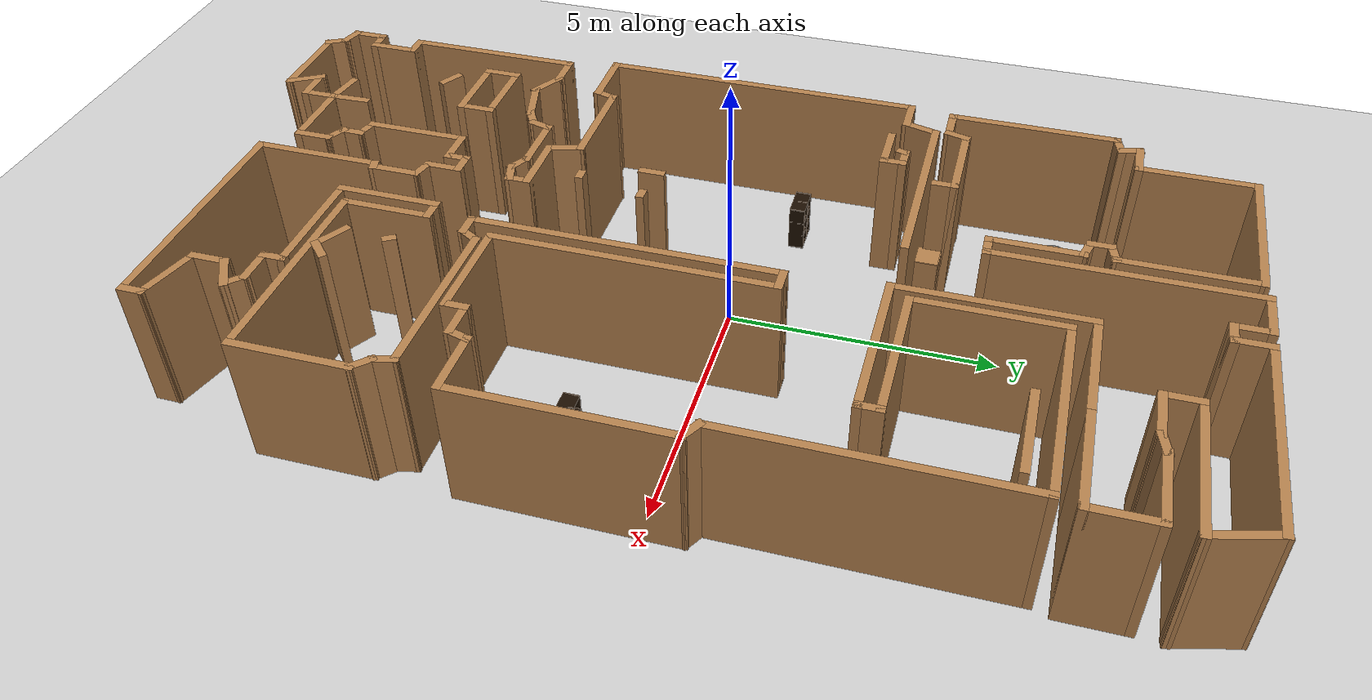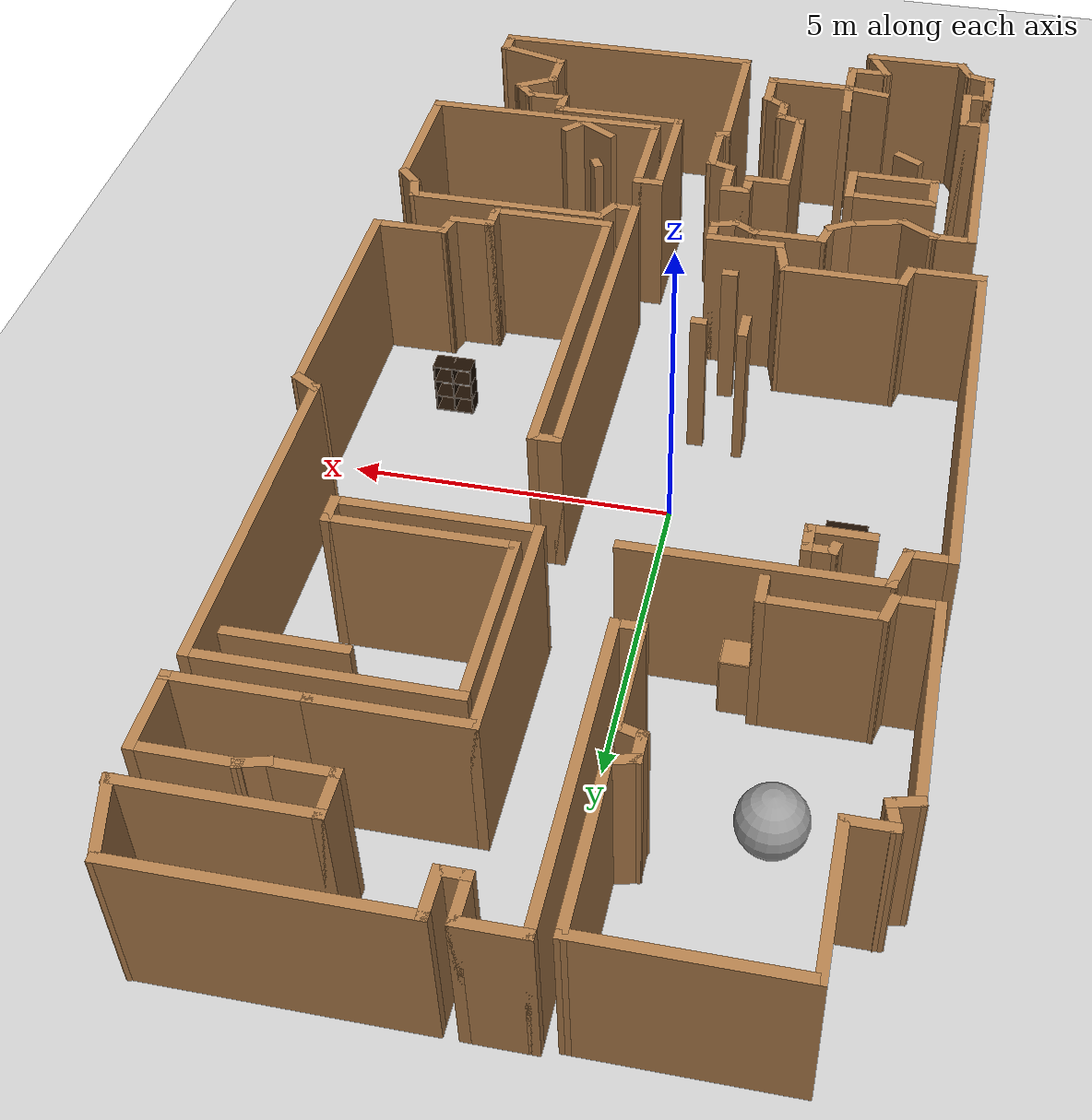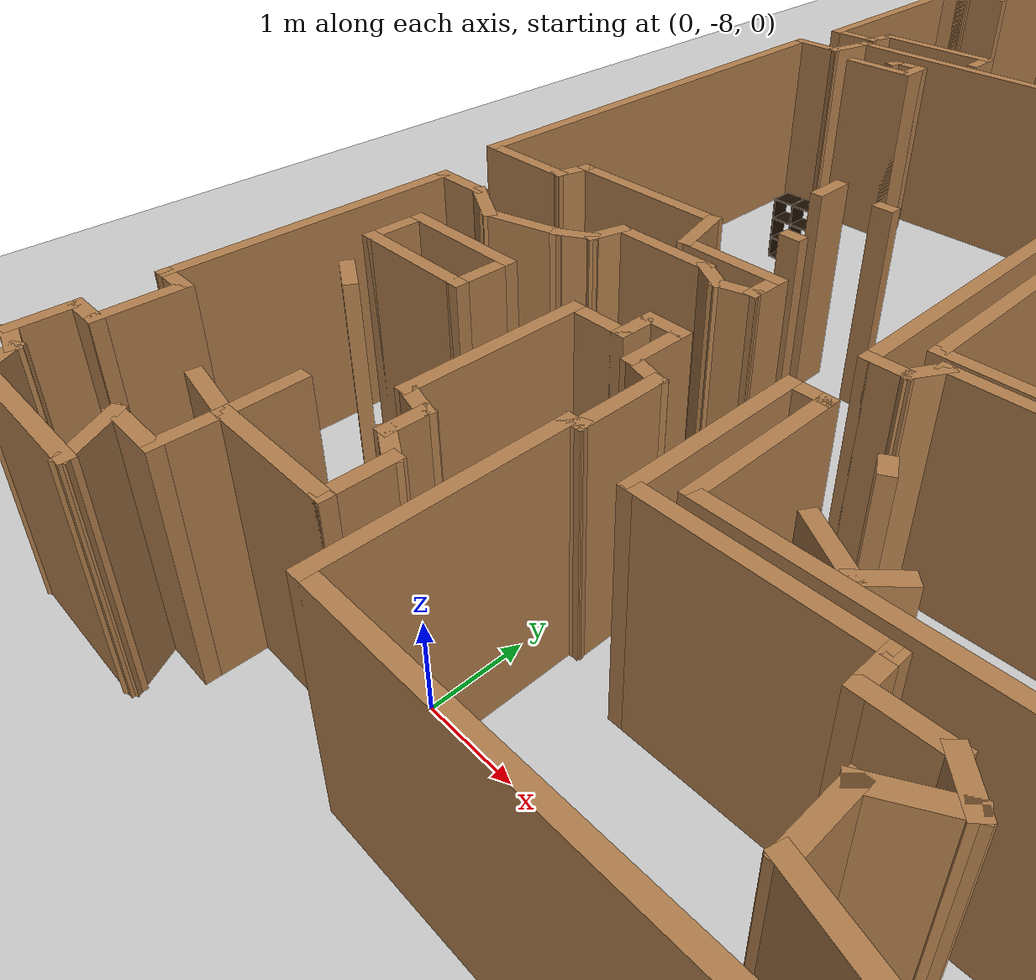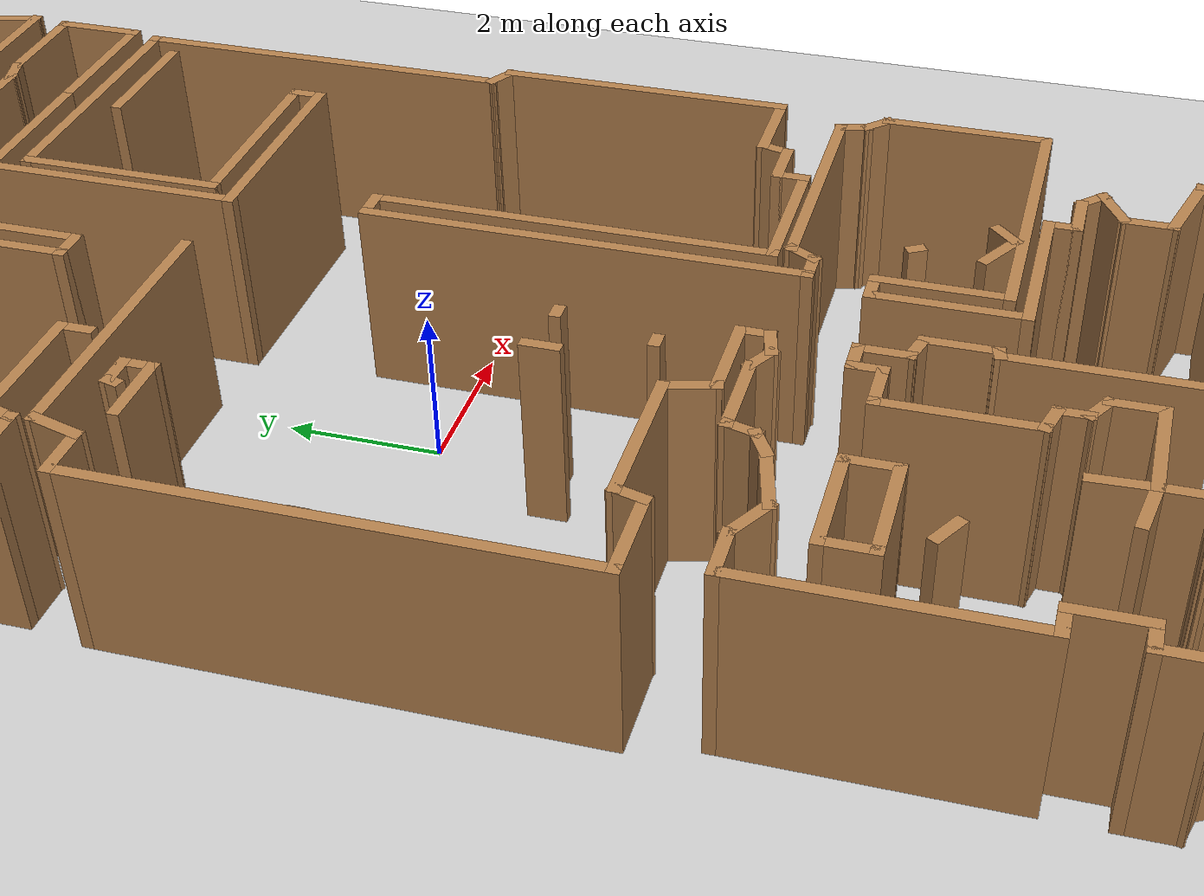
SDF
<sdf version="1.6">
 <world name="default">
  <light name="sun" type="directional">
   <pose>0 0 10 0 -0 0</pose>
   <diffuse>0.8 0.8 0.8 1</diffuse>
   <specular>0.2 0.2 0.2 1</specular>
   <attenuation>
    <range>1000</range>
    <constant>0.9</constant>
    <linear>0.01</linear>
    <quadratic>0.001</quadratic>
   </attenuation>
   <direction>-0.5 0.1 -0.9</direction>
  </light>
  <model name="ground_plane">
   <static>1</static>
   <link name="link">
    <collision name="collision">
     <geometry><plane><normal>0 0 1</normal><size>100 100</size></plane></geometry>
     <surface><friction><ode><mu>100</mu><mu2>50</mu2></ode></friction></surface>
    </collision>
    <visual name="visual">
     <cast_shadows>0</cast_shadows>
     <geometry><plane><normal>0 0 1</normal><size>100 100</size></plane></geometry>
     <material>
      <script><uri>file://media/materials/scripts/gazebo.material</uri><name>Gazebo/Grey</name></script>
     </material>
    </visual>
   </link>
  </model>
  <gravity>0 0 -9.8</gravity>
  <magnetic_field>6e-06 2.3e-05 -4.2e-05</magnetic_field>
  <atmosphere type="adiabatic"/>
  <physics name="default_physics" default="0" type="ode">
   <max_step_size>0.001</max_step_size>
   <real_time_factor>1</real_time_factor>
   <real_time_update_rate>1000</real_time_update_rate>
  </physics>
  <scene><ambient>0.4 0.4 0.4 1</ambient><background>0.7 0.7 0.7 1</background><shadows>1</shadows></scene>
  <spherical_coordinates>
   <surface_model>EARTH_WGS84</surface_model>
   <latitude_deg>0</latitude_deg>
   <longitude_deg>0</longitude_deg>
   <elevation>0</elevation>
   <heading_deg>0</heading_deg>
  </spherical_coordinates>
  <model name="map_31">
   <link name="Wall_0">
    <pose>-2.44947 9.31 0 0 -0 3.14159</pose>
    <visual name="Wall_0_Visual">
     <pose>0 0 1.25 0 -0 0</pose>
     <geometry><box><size>3 0.15 2.5</size></box></geometry>
     <material>
      <script><uri>file://media/materials/scripts/gazebo.material</uri><name>Gazebo/Wood</name></script>
      <ambient>1 1 1 1</ambient>
      <shader type="pixel"/>
     </material>
     <meta><layer>0</layer></meta>
    </visual>
    <collision name="Wall_0_Collision">
     <pose>0 0 1.25 0 -0 0</pose>
     <geometry><box><size>3 0.15 2.5</size></box></geometry>
     <surface>
      <friction>
       <ode><mu>1</mu><mu2>1</mu2><fdir1>0 0 0</fdir1><slip1>0</slip1><slip2>0</slip2></ode>
       <torsional>
        <coefficient>1</coefficient>
        <patch_radius>0</patch_radius>
        <surface_radius>0</surface_radius>
        <use_patch_radius>1</use_patch_radius>
        <ode><slip>0</slip></ode>
       </torsional>
      </friction>
      <bounce><restitution_coefficient>0</restitution_coefficient><threshold>1e+06</threshold></bounce>
      <contact>
       <collide_without_contact>0</collide_without_contact>
       <collide_without_contact_bitmask>1</collide_without_contact_bitmask>
       <collide_bitmask>1</collide_bitmask>
       <ode>
        <soft_cfm>0</soft_cfm>
        <soft_erp>0.2</soft_erp>
        <kp>1e+13</kp>
        <kd>1</kd>
        <max_vel>0.01</max_vel>
        <min_depth>0</min_depth>
       </ode>
       <bullet>
        <split_impulse>1</split_impulse>
        <split_impulse_penetration_threshold>-0.01</split_impulse_penetration_threshold>
        <soft_cfm>0</soft_cfm>
        <soft_erp>0.2</soft_erp>
        <kp>1e+13</kp>
        <kd>1</kd>
       </bullet>
      </contact>
     </surface>
    </collision>
   </link>
   <link name="Wall_1">
    <pose>-3.87447 8.26 0 0 0 -1.5708</pose>
    <visual name="Wall_1_Visual">
     <pose>0 0 1.25 0 -0 0</pose>
     <geometry><box><size>2.25 0.15 2.5</size></box></geometry>
     <material>
      <script><uri>file://media/materials/scripts/gazebo.material</uri><name>Gazebo/Wood</name></script>
      <ambient>1 1 1 1</ambient>
      <shader type="pixel"/>
     </material>
     <meta><layer>0</layer></meta>
    </visual>
    <collision name="Wall_1_Collision">
     <pose>0 0 1.25 0 -0 0</pose>
     <geometry><box><size>2.25 0.15 2.5</size></box></geometry>
     <surface>
      <friction>
       <ode><mu>1</mu><mu2>1</mu2><fdir1>0 0 0</fdir1><slip1>0</slip1><slip2>0</slip2></ode>
       <torsional>
        <coefficient>1</coefficient>
        <patch_radius>0</patch_radius>
        <surface_radius>0</surface_radius>
        <use_patch_radius>1</use_patch_radius>
        <ode><slip>0</slip></ode>
       </torsional>
      </friction>
      <bounce><restitution_coefficient>0</restitution_coefficient><threshold>1e+06</threshold></bounce>
      <contact>
       <collide_without_contact>0</collide_without_contact>
       <collide_without_contact_bitmask>1</collide_without_contact_bitmask>
       <collide_bitmask>1</collide_bitmask>
       <ode>
        <soft_cfm>0</soft_cfm>
        <soft_erp>0.2</soft_erp>
        <kp>1e+13</kp>
        <kd>1</kd>
        <max_vel>0.01</max_vel>
        <min_depth>0</min_depth>
       </ode>
       <bullet>
        <split_impulse>1</split_impulse>
        <split_impulse_penetration_threshold>-0.01</split_impulse_penetration_threshold>
        <soft_cfm>0</soft_cfm>
        <soft_erp>0.2</soft_erp>
        <kp>1e+13</kp>
        <kd>1</kd>
       </bullet>
      </contact>
     </surface>
    </collision>
   </link>
   <link name="Wall_100">
    <pose>0.643586 5.04256 0 0 -0 1.5708</pose>
    <visual name="Wall_100_Visual">
     <pose>0 0 1.25 0 -0 0</pose>
     <geometry><box><size>3.5 0.15 2.5</size></box></geometry>
     <material>
      <script><uri>file://media/materials/scripts/gazebo.material</uri><name>Gazebo/Wood</name></script>
      <ambient>1 1 1 1</ambient>
      <shader type="pixel"/>
     </material>
     <meta><layer>0</layer></meta>
    </visual>
    <collision name="Wall_100_Collision">
     <pose>0 0 1.25 0 -0 0</pose>
     <geometry><box><size>3.5 0.15 2.5</size></box></geometry>
     <surface>
      <friction>
       <ode><mu>1</mu><mu2>1</mu2><fdir1>0 0 0</fdir1><slip1>0</slip1><slip2>0</slip2></ode>
       <torsional>
        <coefficient>1</coefficient>
        <patch_radius>0</patch_radius>
        <surface_radius>0</surface_radius>
        <use_patch_radius>1</use_patch_radius>
        <ode><slip>0</slip></ode>
       </torsional>
      </friction>
      <bounce><restitution_coefficient>0</restitution_coefficient><threshold>1e+06</threshold></bounce>
      <contact>
       <collide_without_contact>0</collide_without_contact>
       <collide_without_contact_bitmask>1</collide_without_contact_bitmask>
       <collide_bitmask>1</collide_bitmask>
       <ode>
        <soft_cfm>0</soft_cfm>
        <soft_erp>0.2</soft_erp>
        <kp>1e+13</kp>
        <kd>1</kd>
        <max_vel>0.01</max_vel>
        <min_depth>0</min_depth>
       </ode>
       <bullet>
        <split_impulse>1</split_impulse>
        <split_impulse_penetration_threshold>-0.01</split_impulse_penetration_threshold>
        <soft_cfm>0</soft_cfm>
        <soft_erp>0.2</soft_erp>
        <kp>1e+13</kp>
        <kd>1</kd>
       </bullet>
      </contact>
     </surface>
    </collision>
   </link>
   <link name="Wall_101">
    <pose>1.69359 6.71756 0 0 -0 0</pose>
    <visual name="Wall_101_Visual">
     <pose>0 0 1.25 0 -0 0</pose>
     <geometry><box><size>2.25 0.15 2.5</size></box></geometry>
     <material>
      <script><uri>file://media/materials/scripts/gazebo.material</uri><name>Gazebo/Wood</name></script>
      <ambient>1 1 1 1</ambient>
      <shader type="pixel"/>
     </material>
     <meta><layer>0</layer></meta>
    </visual>
    <collision name="Wall_101_Collision">
     <pose>0 0 1.25 0 -0 0</pose>
     <geometry><box><size>2.25 0.15 2.5</size></box></geometry>
     <surface>
      <friction>
       <ode><mu>1</mu><mu2>1</mu2><fdir1>0 0 0</fdir1><slip1>0</slip1><slip2>0</slip2></ode>
       <torsional>
        <coefficient>1</coefficient>
        <patch_radius>0</patch_radius>
        <surface_radius>0</surface_radius>
        <use_patch_radius>1</use_patch_radius>
        <ode><slip>0</slip></ode>
       </torsional>
      </friction>
      <bounce><restitution_coefficient>0</restitution_coefficient><threshold>1e+06</threshold></bounce>
      <contact>
       <collide_without_contact>0</collide_without_contact>
       <collide_without_contact_bitmask>1</collide_without_contact_bitmask>
       <collide_bitmask>1</collide_bitmask>
       <ode>
        <soft_cfm>0</soft_cfm>
        <soft_erp>0.2</soft_erp>
        <kp>1e+13</kp>
        <kd>1</kd>
        <max_vel>0.01</max_vel>
        <min_depth>0</min_depth>
       </ode>
       <bullet>
        <split_impulse>1</split_impulse>
        <split_impulse_penetration_threshold>-0.01</split_impulse_penetration_threshold>
        <soft_cfm>0</soft_cfm>
        <soft_erp>0.2</soft_erp>
        <kp>1e+13</kp>
        <kd>1</kd>
       </bullet>
      </contact>
     </surface>
    </collision>
   </link>
   <link name="Wall_102">
    <pose>3.66859 6.71756 0 0 -0 0</pose>
    <visual name="Wall_102_Visual">
     <pose>0 0 1.25 0 -0 0</pose>
     <geometry><box><size>2 0.15 2.5</size></box></geometry>
     <material>
      <script><uri>file://media/materials/scripts/gazebo.material</uri><name>Gazebo/Wood</name></script>
      <ambient>1 1 1 1</ambient>
      <shader type="pixel"/>
     </material>
     <meta><layer>0</layer></meta>
    </visual>
    <collision name="Wall_102_Collision">
     <pose>0 0 1.25 0 -0 0</pose>
     <geometry><box><size>2 0.15 2.5</size></box></geometry>
     <surface>
      <friction>
       <ode><mu>1</mu><mu2>1</mu2><fdir1>0 0 0</fdir1><slip1>0</slip1><slip2>0</slip2></ode>
       <torsional>
        <coefficient>1</coefficient>
        <patch_radius>0</patch_radius>
        <surface_radius>0</surface_radius>
        <use_patch_radius>1</use_patch_radius>
        <ode><slip>0</slip></ode>
       </torsional>
      </friction>
      <bounce><restitution_coefficient>0</restitution_coefficient><threshold>1e+06</threshold></bounce>
      <contact>
       <collide_without_contact>0</collide_without_contact>
       <collide_without_contact_bitmask>1</collide_without_contact_bitmask>
       <collide_bitmask>1</collide_bitmask>
       <ode>
        <soft_cfm>0</soft_cfm>
        <soft_erp>0.2</soft_erp>
        <kp>1e+13</kp>
        <kd>1</kd>
        <max_vel>0.01</max_vel>
        <min_depth>0</min_depth>
       </ode>
       <bullet>
        <split_impulse>1</split_impulse>
        <split_impulse_penetration_threshold>-0.01</split_impulse_penetration_threshold>
        <soft_cfm>0</soft_cfm>
        <soft_erp>0.2</soft_erp>
        <kp>1e+13</kp>
        <kd>1</kd>
       </bullet>
      </contact>
     </surface>
    </collision>
   </link>
   <link name="Wall_103">
    <pose>4.59359 7.26756 0 0 -0 1.5708</pose>
    <visual name="Wall_103_Visual">
     <pose>0 0 1.25 0 -0 0</pose>
     <geometry><box><size>1.25 0.15 2.5</size></box></geometry>
     <material>
      <script><uri>file://media/materials/scripts/gazebo.material</uri><name>Gazebo/Wood</name></script>
      <ambient>1 1 1 1</ambient>
      <shader type="pixel"/>
     </material>
     <meta><layer>0</layer></meta>
    </visual>
    <collision name="Wall_103_Collision">
     <pose>0 0 1.25 0 -0 0</pose>
     <geometry><box><size>1.25 0.15 2.5</size></box></geometry>
     <surface>
      <friction>
       <ode><mu>1</mu><mu2>1</mu2><fdir1>0 0 0</fdir1><slip1>0</slip1><slip2>0</slip2></ode>
       <torsional>
        <coefficient>1</coefficient>
        <patch_radius>0</patch_radius>
        <surface_radius>0</surface_radius>
        <use_patch_radius>1</use_patch_radius>
        <ode><slip>0</slip></ode>
       </torsional>
      </friction>
      <bounce><restitution_coefficient>0</restitution_coefficient><threshold>1e+06</threshold></bounce>
      <contact>
       <collide_without_contact>0</collide_without_contact>
       <collide_without_contact_bitmask>1</collide_without_contact_bitmask>
       <collide_bitmask>1</collide_bitmask>
       <ode>
        <soft_cfm>0</soft_cfm>
        <soft_erp>0.2</soft_erp>
        <kp>1e+13</kp>
        <kd>1</kd>
        <max_vel>0.01</max_vel>
        <min_depth>0</min_depth>
       </ode>
       <bullet>
        <split_impulse>1</split_impulse>
        <split_impulse_penetration_threshold>-0.01</split_impulse_penetration_threshold>
        <soft_cfm>0</soft_cfm>
        <soft_erp>0.2</soft_erp>
        <kp>1e+13</kp>
        <kd>1</kd>
       </bullet>
      </contact>
     </surface>
    </collision>
   </link>
   <link name="Wall_104">
    <pose>3.91859 7.81756 0 0 -0 3.14159</pose>
    <visual name="Wall_104_Visual">
     <pose>0 0 1.25 0 -0 0</pose>
     <geometry><box><size>1.5 0.15 2.5</size></box></geometry>
     <material>
      <script><uri>file://media/materials/scripts/gazebo.material</uri><name>Gazebo/Wood</name></script>
      <ambient>1 1 1 1</ambient>
      <shader type="pixel"/>
     </material>
     <meta><layer>0</layer></meta>
    </visual>
    <collision name="Wall_104_Collision">
     <pose>0 0 1.25 0 -0 0</pose>
     <geometry><box><size>1.5 0.15 2.5</size></box></geometry>
     <surface>
      <friction>
       <ode><mu>1</mu><mu2>1</mu2><fdir1>0 0 0</fdir1><slip1>0</slip1><slip2>0</slip2></ode>
       <torsional>
        <coefficient>1</coefficient>
        <patch_radius>0</patch_radius>
        <surface_radius>0</surface_radius>
        <use_patch_radius>1</use_patch_radius>
        <ode><slip>0</slip></ode>
       </torsional>
      </friction>
      <bounce><restitution_coefficient>0</restitution_coefficient><threshold>1e+06</threshold></bounce>
      <contact>
       <collide_without_contact>0</collide_without_contact>
       <collide_without_contact_bitmask>1</collide_without_contact_bitmask>
       <collide_bitmask>1</collide_bitmask>
       <ode>
        <soft_cfm>0</soft_cfm>
        <soft_erp>0.2</soft_erp>
        <kp>1e+13</kp>
        <kd>1</kd>
        <max_vel>0.01</max_vel>
        <min_depth>0</min_depth>
       </ode>
       <bullet>
        <split_impulse>1</split_impulse>
        <split_impulse_penetration_threshold>-0.01</split_impulse_penetration_threshold>
        <soft_cfm>0</soft_cfm>
        <soft_erp>0.2</soft_erp>
        <kp>1e+13</kp>
        <kd>1</kd>
       </bullet>
      </contact>
     </surface>
    </collision>
   </link>
   <link name="Wall_105">
    <pose>3.07455 7.77226 0 0 0 -2.87979</pose>
    <visual name="Wall_105_Visual">
     <pose>0 0 1.25 0 -0 0</pose>
     <geometry><box><size>0.5 0.15 2.5</size></box></geometry>
     <material>
      <script><uri>file://media/materials/scripts/gazebo.material</uri><name>Gazebo/Wood</name></script>
      <ambient>1 1 1 1</ambient>
      <shader type="pixel"/>
     </material>
     <meta><layer>0</layer></meta>
    </visual>
    <collision name="Wall_105_Collision">
     <pose>0 0 1.25 0 -0 0</pose>
     <geometry><box><size>0.5 0.15 2.5</size></box></geometry>
     <surface>
      <friction>
       <ode><mu>1</mu><mu2>1</mu2><fdir1>0 0 0</fdir1><slip1>0</slip1><slip2>0</slip2></ode>
       <torsional>
        <coefficient>1</coefficient>
        <patch_radius>0</patch_radius>
        <surface_radius>0</surface_radius>
        <use_patch_radius>1</use_patch_radius>
        <ode><slip>0</slip></ode>
       </torsional>
      </friction>
      <bounce><restitution_coefficient>0</restitution_coefficient><threshold>1e+06</threshold></bounce>
      <contact>
       <collide_without_contact>0</collide_without_contact>
       <collide_without_contact_bitmask>1</collide_without_contact_bitmask>
       <collide_bitmask>1</collide_bitmask>
       <ode>
        <soft_cfm>0</soft_cfm>
        <soft_erp>0.2</soft_erp>
        <kp>1e+13</kp>
        <kd>1</kd>
        <max_vel>0.01</max_vel>
        <min_depth>0</min_depth>
       </ode>
       <bullet>
        <split_impulse>1</split_impulse>
        <split_impulse_penetration_threshold>-0.01</split_impulse_penetration_threshold>
        <soft_cfm>0</soft_cfm>
        <soft_erp>0.2</soft_erp>
        <kp>1e+13</kp>
        <kd>1</kd>
       </bullet>
      </contact>
     </surface>
    </collision>
   </link>
   <link name="Wall_106">
    <pose>2.48051 7.72697 0 0 -0 3.14159</pose>
    <visual name="Wall_106_Visual">
     <pose>0 0 1.25 0 -0 0</pose>
     <geometry><box><size>1 0.15 2.5</size></box></geometry>
     <material>
      <script><uri>file://media/materials/scripts/gazebo.material</uri><name>Gazebo/Wood</name></script>
      <ambient>1 1 1 1</ambient>
      <shader type="pixel"/>
     </material>
     <meta><layer>0</layer></meta>
    </visual>
    <collision name="Wall_106_Collision">
     <pose>0 0 1.25 0 -0 0</pose>
     <geometry><box><size>1 0.15 2.5</size></box></geometry>
     <surface>
      <friction>
       <ode><mu>1</mu><mu2>1</mu2><fdir1>0 0 0</fdir1><slip1>0</slip1><slip2>0</slip2></ode>
       <torsional>
        <coefficient>1</coefficient>
        <patch_radius>0</patch_radius>
        <surface_radius>0</surface_radius>
        <use_patch_radius>1</use_patch_radius>
        <ode><slip>0</slip></ode>
       </torsional>
      </friction>
      <bounce><restitution_coefficient>0</restitution_coefficient><threshold>1e+06</threshold></bounce>
      <contact>
       <collide_without_contact>0</collide_without_contact>
       <collide_without_contact_bitmask>1</collide_without_contact_bitmask>
       <collide_bitmask>1</collide_bitmask>
       <ode>
        <soft_cfm>0</soft_cfm>
        <soft_erp>0.2</soft_erp>
        <kp>1e+13</kp>
        <kd>1</kd>
        <max_vel>0.01</max_vel>
        <min_depth>0</min_depth>
       </ode>
       <bullet>
        <split_impulse>1</split_impulse>
        <split_impulse_penetration_threshold>-0.01</split_impulse_penetration_threshold>
        <soft_cfm>0</soft_cfm>
        <soft_erp>0.2</soft_erp>
        <kp>1e+13</kp>
        <kd>1</kd>
       </bullet>
      </contact>
     </surface>
    </collision>
   </link>
   <link name="Wall_107">
    <pose>2.05551 8.02697 0 0 -0 1.5708</pose>
    <visual name="Wall_107_Visual">
     <pose>0 0 1.25 0 -0 0</pose>
     <geometry><box><size>0.75 0.15 2.5</size></box></geometry>
     <material>
      <script><uri>file://media/materials/scripts/gazebo.material</uri><name>Gazebo/Wood</name></script>
      <ambient>1 1 1 1</ambient>
      <shader type="pixel"/>
     </material>
     <meta><layer>0</layer></meta>
    </visual>
    <collision name="Wall_107_Collision">
     <pose>0 0 1.25 0 -0 0</pose>
     <geometry><box><size>0.75 0.15 2.5</size></box></geometry>
     <surface>
      <friction>
       <ode><mu>1</mu><mu2>1</mu2><fdir1>0 0 0</fdir1><slip1>0</slip1><slip2>0</slip2></ode>
       <torsional>
        <coefficient>1</coefficient>
        <patch_radius>0</patch_radius>
        <surface_radius>0</surface_radius>
        <use_patch_radius>1</use_patch_radius>
        <ode><slip>0</slip></ode>
       </torsional>
      </friction>
      <bounce><restitution_coefficient>0</restitution_coefficient><threshold>1e+06</threshold></bounce>
      <contact>
       <collide_without_contact>0</collide_without_contact>
       <collide_without_contact_bitmask>1</collide_without_contact_bitmask>
       <collide_bitmask>1</collide_bitmask>
       <ode>
        <soft_cfm>0</soft_cfm>
        <soft_erp>0.2</soft_erp>
        <kp>1e+13</kp>
        <kd>1</kd>
        <max_vel>0.01</max_vel>
        <min_depth>0</min_depth>
       </ode>
       <bullet>
        <split_impulse>1</split_impulse>
        <split_impulse_penetration_threshold>-0.01</split_impulse_penetration_threshold>
        <soft_cfm>0</soft_cfm>
        <soft_erp>0.2</soft_erp>
        <kp>1e+13</kp>
        <kd>1</kd>
       </bullet>
      </contact>
     </surface>
    </collision>
   </link>
   <link name="Wall_108">
    <pose>3.35551 8.32697 0 0 -0 0</pose>
    <visual name="Wall_108_Visual">
     <pose>0 0 1.25 0 -0 0</pose>
     <geometry><box><size>2.75 0.15 2.5</size></box></geometry>
     <material>
      <script><uri>file://media/materials/scripts/gazebo.material</uri><name>Gazebo/Wood</name></script>
      <ambient>1 1 1 1</ambient>
      <shader type="pixel"/>
     </material>
     <meta><layer>0</layer></meta>
    </visual>
    <collision name="Wall_108_Collision">
     <pose>0 0 1.25 0 -0 0</pose>
     <geometry><box><size>2.75 0.15 2.5</size></box></geometry>
     <surface>
      <friction>
       <ode><mu>1</mu><mu2>1</mu2><fdir1>0 0 0</fdir1><slip1>0</slip1><slip2>0</slip2></ode>
       <torsional>
        <coefficient>1</coefficient>
        <patch_radius>0</patch_radius>
        <surface_radius>0</surface_radius>
        <use_patch_radius>1</use_patch_radius>
        <ode><slip>0</slip></ode>
       </torsional>
      </friction>
      <bounce><restitution_coefficient>0</restitution_coefficient><threshold>1e+06</threshold></bounce>
      <contact>
       <collide_without_contact>0</collide_without_contact>
       <collide_without_contact_bitmask>1</collide_without_contact_bitmask>
       <collide_bitmask>1</collide_bitmask>
       <ode>
        <soft_cfm>0</soft_cfm>
        <soft_erp>0.2</soft_erp>
        <kp>1e+13</kp>
        <kd>1</kd>
        <max_vel>0.01</max_vel>
        <min_depth>0</min_depth>
       </ode>
       <bullet>
        <split_impulse>1</split_impulse>
        <split_impulse_penetration_threshold>-0.01</split_impulse_penetration_threshold>
        <soft_cfm>0</soft_cfm>
        <soft_erp>0.2</soft_erp>
        <kp>1e+13</kp>
        <kd>1</kd>
       </bullet>
      </contact>
     </surface>
    </collision>
   </link>
   <link name="Wall_109">
    <pose>4.51316 8.85823 0 0 -0 1.8326</pose>
    <visual name="Wall_109_Visual">
     <pose>0 0 1.25 0 -0 0</pose>
     <geometry><box><size>1.25 0.15 2.5</size></box></geometry>
     <material>
      <script><uri>file://media/materials/scripts/gazebo.material</uri><name>Gazebo/Wood</name></script>
      <ambient>1 1 1 1</ambient>
      <shader type="pixel"/>
     </material>
     <meta><layer>0</layer></meta>
    </visual>
    <collision name="Wall_109_Collision">
     <pose>0 0 1.25 0 -0 0</pose>
     <geometry><box><size>1.25 0.15 2.5</size></box></geometry>
     <surface>
      <friction>
       <ode><mu>1</mu><mu2>1</mu2><fdir1>0 0 0</fdir1><slip1>0</slip1><slip2>0</slip2></ode>
       <torsional>
        <coefficient>1</coefficient>
        <patch_radius>0</patch_radius>
        <surface_radius>0</surface_radius>
        <use_patch_radius>1</use_patch_radius>
        <ode><slip>0</slip></ode>
       </torsional>
      </friction>
      <bounce><restitution_coefficient>0</restitution_coefficient><threshold>1e+06</threshold></bounce>
      <contact>
       <collide_without_contact>0</collide_without_contact>
       <collide_without_contact_bitmask>1</collide_without_contact_bitmask>
       <collide_bitmask>1</collide_bitmask>
       <ode>
        <soft_cfm>0</soft_cfm>
        <soft_erp>0.2</soft_erp>
        <kp>1e+13</kp>
        <kd>1</kd>
        <max_vel>0.01</max_vel>
        <min_depth>0</min_depth>
       </ode>
       <bullet>
        <split_impulse>1</split_impulse>
        <split_impulse_penetration_threshold>-0.01</split_impulse_penetration_threshold>
        <soft_cfm>0</soft_cfm>
        <soft_erp>0.2</soft_erp>
        <kp>1e+13</kp>
        <kd>1</kd>
       </bullet>
      </contact>
     </surface>
    </collision>
   </link>
   <link name="Wall_110">
    <pose>2.44581 9.38949 0 0 -0 3.14159</pose>
    <visual name="Wall_110_Visual">
     <pose>0 0 1.25 0 -0 0</pose>
     <geometry><box><size>4 0.15 2.5</size></box></geometry>
     <material>
      <script><uri>file://media/materials/scripts/gazebo.material</uri><name>Gazebo/Wood</name></script>
      <ambient>1 1 1 1</ambient>
      <shader type="pixel"/>
     </material>
     <meta><layer>0</layer></meta>
    </visual>
    <collision name="Wall_110_Collision">
     <pose>0 0 1.25 0 -0 0</pose>
     <geometry><box><size>4 0.15 2.5</size></box></geometry>
     <surface>
      <friction>
       <ode><mu>1</mu><mu2>1</mu2><fdir1>0 0 0</fdir1><slip1>0</slip1><slip2>0</slip2></ode>
       <torsional>
        <coefficient>1</coefficient>
        <patch_radius>0</patch_radius>
        <surface_radius>0</surface_radius>
        <use_patch_radius>1</use_patch_radius>
        <ode><slip>0</slip></ode>
       </torsional>
      </friction>
      <bounce><restitution_coefficient>0</restitution_coefficient><threshold>1e+06</threshold></bounce>
      <contact>
       <collide_without_contact>0</collide_without_contact>
       <collide_without_contact_bitmask>1</collide_without_contact_bitmask>
       <collide_bitmask>1</collide_bitmask>
       <ode>
        <soft_cfm>0</soft_cfm>
        <soft_erp>0.2</soft_erp>
        <kp>1e+13</kp>
        <kd>1</kd>
        <max_vel>0.01</max_vel>
        <min_depth>0</min_depth>
       </ode>
       <bullet>
        <split_impulse>1</split_impulse>
        <split_impulse_penetration_threshold>-0.01</split_impulse_penetration_threshold>
        <soft_cfm>0</soft_cfm>
        <soft_erp>0.2</soft_erp>
        <kp>1e+13</kp>
        <kd>1</kd>
       </bullet>
      </contact>
     </surface>
    </collision>
   </link>
   <link name="Wall_111">
    <pose>0.520811 9.08949 0 0 0 -1.5708</pose>
    <visual name="Wall_111_Visual">
     <pose>0 0 1.25 0 -0 0</pose>
     <geometry><box><size>0.75 0.15 2.5</size></box></geometry>
     <material>
      <script><uri>file://media/materials/scripts/gazebo.material</uri><name>Gazebo/Wood</name></script>
      <ambient>1 1 1 1</ambient>
      <shader type="pixel"/>
     </material>
     <meta><layer>0</layer></meta>
    </visual>
    <collision name="Wall_111_Collision">
     <pose>0 0 1.25 0 -0 0</pose>
     <geometry><box><size>0.75 0.15 2.5</size></box></geometry>
     <surface>
      <friction>
       <ode><mu>1</mu><mu2>1</mu2><fdir1>0 0 0</fdir1><slip1>0</slip1><slip2>0</slip2></ode>
       <torsional>
        <coefficient>1</coefficient>
        <patch_radius>0</patch_radius>
        <surface_radius>0</surface_radius>
        <use_patch_radius>1</use_patch_radius>
        <ode><slip>0</slip></ode>
       </torsional>
      </friction>
      <bounce><restitution_coefficient>0</restitution_coefficient><threshold>1e+06</threshold></bounce>
      <contact>
       <collide_without_contact>0</collide_without_contact>
       <collide_without_contact_bitmask>1</collide_without_contact_bitmask>
       <collide_bitmask>1</collide_bitmask>
       <ode>
        <soft_cfm>0</soft_cfm>
        <soft_erp>0.2</soft_erp>
        <kp>1e+13</kp>
        <kd>1</kd>
        <max_vel>0.01</max_vel>
        <min_depth>0</min_depth>
       </ode>
       <bullet>
        <split_impulse>1</split_impulse>
        <split_impulse_penetration_threshold>-0.01</split_impulse_penetration_threshold>
        <soft_cfm>0</soft_cfm>
        <soft_erp>0.2</soft_erp>
        <kp>1e+13</kp>
        <kd>1</kd>
       </bullet>
      </contact>
     </surface>
    </collision>
   </link>
   <link name="Wall_112">
    <pose>0.345811 8.78949 0 0 -0 3.14159</pose>
    <visual name="Wall_112_Visual">
     <pose>0 0 1.25 0 -0 0</pose>
     <geometry><box><size>0.5 0.15 2.5</size></box></geometry>
     <material>
      <script><uri>file://media/materials/scripts/gazebo.material</uri><name>Gazebo/Wood</name></script>
      <ambient>1 1 1 1</ambient>
      <shader type="pixel"/>
     </material>
     <meta><layer>0</layer></meta>
    </visual>
    <collision name="Wall_112_Collision">
     <pose>0 0 1.25 0 -0 0</pose>
     <geometry><box><size>0.5 0.15 2.5</size></box></geometry>
     <surface>
      <friction>
       <ode><mu>1</mu><mu2>1</mu2><fdir1>0 0 0</fdir1><slip1>0</slip1><slip2>0</slip2></ode>
       <torsional>
        <coefficient>1</coefficient>
        <patch_radius>0</patch_radius>
        <surface_radius>0</surface_radius>
        <use_patch_radius>1</use_patch_radius>
        <ode><slip>0</slip></ode>
       </torsional>
      </friction>
      <bounce><restitution_coefficient>0</restitution_coefficient><threshold>1e+06</threshold></bounce>
      <contact>
       <collide_without_contact>0</collide_without_contact>
       <collide_without_contact_bitmask>1</collide_without_contact_bitmask>
       <collide_bitmask>1</collide_bitmask>
       <ode>
        <soft_cfm>0</soft_cfm>
        <soft_erp>0.2</soft_erp>
        <kp>1e+13</kp>
        <kd>1</kd>
        <max_vel>0.01</max_vel>
        <min_depth>0</min_depth>
       </ode>
       <bullet>
        <split_impulse>1</split_impulse>
        <split_impulse_penetration_threshold>-0.01</split_impulse_penetration_threshold>
        <soft_cfm>0</soft_cfm>
        <soft_erp>0.2</soft_erp>
        <kp>1e+13</kp>
        <kd>1</kd>
       </bullet>
      </contact>
     </surface>
    </collision>
   </link>
   <link name="Wall_113">
    <pose>0.170811 9.08949 0 0 -0 1.5708</pose>
    <visual name="Wall_113_Visual">
     <pose>0 0 1.25 0 -0 0</pose>
     <geometry><box><size>0.75 0.15 2.5</size></box></geometry>
     <material>
      <script><uri>file://media/materials/scripts/gazebo.material</uri><name>Gazebo/Wood</name></script>
      <ambient>1 1 1 1</ambient>
      <shader type="pixel"/>
     </material>
     <meta><layer>0</layer></meta>
    </visual>
    <collision name="Wall_113_Collision">
     <pose>0 0 1.25 0 -0 0</pose>
     <geometry><box><size>0.75 0.15 2.5</size></box></geometry>
     <surface>
      <friction>
       <ode><mu>1</mu><mu2>1</mu2><fdir1>0 0 0</fdir1><slip1>0</slip1><slip2>0</slip2></ode>
       <torsional>
        <coefficient>1</coefficient>
        <patch_radius>0</patch_radius>
        <surface_radius>0</surface_radius>
        <use_patch_radius>1</use_patch_radius>
        <ode><slip>0</slip></ode>
       </torsional>
      </friction>
      <bounce><restitution_coefficient>0</restitution_coefficient><threshold>1e+06</threshold></bounce>
      <contact>
       <collide_without_contact>0</collide_without_contact>
       <collide_without_contact_bitmask>1</collide_without_contact_bitmask>
       <collide_bitmask>1</collide_bitmask>
       <ode>
        <soft_cfm>0</soft_cfm>
        <soft_erp>0.2</soft_erp>
        <kp>1e+13</kp>
        <kd>1</kd>
        <max_vel>0.01</max_vel>
        <min_depth>0</min_depth>
       </ode>
       <bullet>
        <split_impulse>1</split_impulse>
        <split_impulse_penetration_threshold>-0.01</split_impulse_penetration_threshold>
        <soft_cfm>0</soft_cfm>
        <soft_erp>0.2</soft_erp>
        <kp>1e+13</kp>
        <kd>1</kd>
       </bullet>
      </contact>
     </surface>
    </collision>
   </link>
   <link name="Wall_116">
    <pose>-0.254189 9.38949 0 0 -0 3.14159</pose>
    <visual name="Wall_116_Visual">
     <pose>0 0 1.25 0 -0 0</pose>
     <geometry><box><size>1 0.15 2.5</size></box></geometry>
     <material>
      <script><uri>file://media/materials/scripts/gazebo.material</uri><name>Gazebo/Wood</name></script>
      <ambient>1 1 1 1</ambient>
      <shader type="pixel"/>
     </material>
     <meta><layer>0</layer></meta>
    </visual>
    <collision name="Wall_116_Collision">
     <pose>0 0 1.25 0 -0 0</pose>
     <geometry><box><size>1 0.15 2.5</size></box></geometry>
     <surface>
      <friction>
       <ode><mu>1</mu><mu2>1</mu2><fdir1>0 0 0</fdir1><slip1>0</slip1><slip2>0</slip2></ode>
       <torsional>
        <coefficient>1</coefficient>
        <patch_radius>0</patch_radius>
        <surface_radius>0</surface_radius>
        <use_patch_radius>1</use_patch_radius>
        <ode><slip>0</slip></ode>
       </torsional>
      </friction>
      <bounce><restitution_coefficient>0</restitution_coefficient><threshold>1e+06</threshold></bounce>
      <contact>
       <collide_without_contact>0</collide_without_contact>
       <collide_without_contact_bitmask>1</collide_without_contact_bitmask>
       <collide_bitmask>1</collide_bitmask>
       <ode>
        <soft_cfm>0</soft_cfm>
        <soft_erp>0.2</soft_erp>
        <kp>1e+13</kp>
        <kd>1</kd>
        <max_vel>0.01</max_vel>
        <min_depth>0</min_depth>
       </ode>
       <bullet>
        <split_impulse>1</split_impulse>
        <split_impulse_penetration_threshold>-0.01</split_impulse_penetration_threshold>
        <soft_cfm>0</soft_cfm>
        <soft_erp>0.2</soft_erp>
        <kp>1e+13</kp>
        <kd>1</kd>
       </bullet>
      </contact>
     </surface>
    </collision>
   </link>
   <link name="Wall_117">
    <pose>-0.679188 7.08949 0 0 0 -1.5708</pose>
    <visual name="Wall_117_Visual">
     <pose>0 0 1.25 0 -0 0</pose>
     <geometry><box><size>4.75 0.15 2.5</size></box></geometry>
     <material>
      <script><uri>file://media/materials/scripts/gazebo.material</uri><name>Gazebo/Wood</name></script>
      <ambient>1 1 1 1</ambient>
      <shader type="pixel"/>
     </material>
     <meta><layer>0</layer></meta>
    </visual>
    <collision name="Wall_117_Collision">
     <pose>0 0 1.25 0 -0 0</pose>
     <geometry><box><size>4.75 0.15 2.5</size></box></geometry>
     <surface>
      <friction>
       <ode><mu>1</mu><mu2>1</mu2><fdir1>0 0 0</fdir1><slip1>0</slip1><slip2>0</slip2></ode>
       <torsional>
        <coefficient>1</coefficient>
        <patch_radius>0</patch_radius>
        <surface_radius>0</surface_radius>
        <use_patch_radius>1</use_patch_radius>
        <ode><slip>0</slip></ode>
       </torsional>
      </friction>
      <bounce><restitution_coefficient>0</restitution_coefficient><threshold>1e+06</threshold></bounce>
      <contact>
       <collide_without_contact>0</collide_without_contact>
       <collide_without_contact_bitmask>1</collide_without_contact_bitmask>
       <collide_bitmask>1</collide_bitmask>
       <ode>
        <soft_cfm>0</soft_cfm>
        <soft_erp>0.2</soft_erp>
        <kp>1e+13</kp>
        <kd>1</kd>
        <max_vel>0.01</max_vel>
        <min_depth>0</min_depth>
       </ode>
       <bullet>
        <split_impulse>1</split_impulse>
        <split_impulse_penetration_threshold>-0.01</split_impulse_penetration_threshold>
        <soft_cfm>0</soft_cfm>
        <soft_erp>0.2</soft_erp>
        <kp>1e+13</kp>
        <kd>1</kd>
       </bullet>
      </contact>
     </surface>
    </collision>
   </link>
   <link name="Wall_120">
    <pose>-0.854189 4.78949 0 0 -0 3.14159</pose>
    <visual name="Wall_120_Visual">
     <pose>0 0 1.25 0 -0 0</pose>
     <geometry><box><size>0.5 0.15 2.5</size></box></geometry>
     <material>
      <script><uri>file://media/materials/scripts/gazebo.material</uri><name>Gazebo/Wood</name></script>
      <ambient>1 1 1 1</ambient>
      <shader type="pixel"/>
     </material>
     <meta><layer>0</layer></meta>
    </visual>
    <collision name="Wall_120_Collision">
     <pose>0 0 1.25 0 -0 0</pose>
     <geometry><box><size>0.5 0.15 2.5</size></box></geometry>
     <surface>
      <friction>
       <ode><mu>1</mu><mu2>1</mu2><fdir1>0 0 0</fdir1><slip1>0</slip1><slip2>0</slip2></ode>
       <torsional>
        <coefficient>1</coefficient>
        <patch_radius>0</patch_radius>
        <surface_radius>0</surface_radius>
        <use_patch_radius>1</use_patch_radius>
        <ode><slip>0</slip></ode>
       </torsional>
      </friction>
      <bounce><restitution_coefficient>0</restitution_coefficient><threshold>1e+06</threshold></bounce>
      <contact>
       <collide_without_contact>0</collide_without_contact>
       <collide_without_contact_bitmask>1</collide_without_contact_bitmask>
       <collide_bitmask>1</collide_bitmask>
       <ode>
        <soft_cfm>0</soft_cfm>
        <soft_erp>0.2</soft_erp>
        <kp>1e+13</kp>
        <kd>1</kd>
        <max_vel>0.01</max_vel>
        <min_depth>0</min_depth>
       </ode>
       <bullet>
        <split_impulse>1</split_impulse>
        <split_impulse_penetration_threshold>-0.01</split_impulse_penetration_threshold>
        <soft_cfm>0</soft_cfm>
        <soft_erp>0.2</soft_erp>
        <kp>1e+13</kp>
        <kd>1</kd>
       </bullet>
      </contact>
     </surface>
    </collision>
   </link>
   <link name="Wall_124">
    <pose>-1.02919 5.58949 0 0 -0 1.5708</pose>
    <visual name="Wall_124_Visual">
     <pose>0 0 1.25 0 -0 0</pose>
     <geometry><box><size>1.75 0.15 2.5</size></box></geometry>
     <material>
      <script><uri>file://media/materials/scripts/gazebo.material</uri><name>Gazebo/Wood</name></script>
      <ambient>1 1 1 1</ambient>
      <shader type="pixel"/>
     </material>
     <meta><layer>0</layer></meta>
    </visual>
    <collision name="Wall_124_Collision">
     <pose>0 0 1.25 0 -0 0</pose>
     <geometry><box><size>1.75 0.15 2.5</size></box></geometry>
     <surface>
      <friction>
       <ode><mu>1</mu><mu2>1</mu2><fdir1>0 0 0</fdir1><slip1>0</slip1><slip2>0</slip2></ode>
       <torsional>
        <coefficient>1</coefficient>
        <patch_radius>0</patch_radius>
        <surface_radius>0</surface_radius>
        <use_patch_radius>1</use_patch_radius>
        <ode><slip>0</slip></ode>
       </torsional>
      </friction>
      <bounce><restitution_coefficient>0</restitution_coefficient><threshold>1e+06</threshold></bounce>
      <contact>
       <collide_without_contact>0</collide_without_contact>
       <collide_without_contact_bitmask>1</collide_without_contact_bitmask>
       <collide_bitmask>1</collide_bitmask>
       <ode>
        <soft_cfm>0</soft_cfm>
        <soft_erp>0.2</soft_erp>
        <kp>1e+13</kp>
        <kd>1</kd>
        <max_vel>0.01</max_vel>
        <min_depth>0</min_depth>
       </ode>
       <bullet>
        <split_impulse>1</split_impulse>
        <split_impulse_penetration_threshold>-0.01</split_impulse_penetration_threshold>
        <soft_cfm>0</soft_cfm>
        <soft_erp>0.2</soft_erp>
        <kp>1e+13</kp>
        <kd>1</kd>
       </bullet>
      </contact>
     </surface>
    </collision>
   </link>
   <link name="Wall_125">
    <pose>-1.19823 6.43478 0 0 -0 2.87979</pose>
    <visual name="Wall_125_Visual">
     <pose>0 0 1.25 0 -0 0</pose>
     <geometry><box><size>0.5 0.15 2.5</size></box></geometry>
     <material>
      <script><uri>file://media/materials/scripts/gazebo.material</uri><name>Gazebo/Wood</name></script>
      <ambient>1 1 1 1</ambient>
      <shader type="pixel"/>
     </material>
     <meta><layer>0</layer></meta>
    </visual>
    <collision name="Wall_125_Collision">
     <pose>0 0 1.25 0 -0 0</pose>
     <geometry><box><size>0.5 0.15 2.5</size></box></geometry>
     <surface>
      <friction>
       <ode><mu>1</mu><mu2>1</mu2><fdir1>0 0 0</fdir1><slip1>0</slip1><slip2>0</slip2></ode>
       <torsional>
        <coefficient>1</coefficient>
        <patch_radius>0</patch_radius>
        <surface_radius>0</surface_radius>
        <use_patch_radius>1</use_patch_radius>
        <ode><slip>0</slip></ode>
       </torsional>
      </friction>
      <bounce><restitution_coefficient>0</restitution_coefficient><threshold>1e+06</threshold></bounce>
      <contact>
       <collide_without_contact>0</collide_without_contact>
       <collide_without_contact_bitmask>1</collide_without_contact_bitmask>
       <collide_bitmask>1</collide_bitmask>
       <ode>
        <soft_cfm>0</soft_cfm>
        <soft_erp>0.2</soft_erp>
        <kp>1e+13</kp>
        <kd>1</kd>
        <max_vel>0.01</max_vel>
        <min_depth>0</min_depth>
       </ode>
       <bullet>
        <split_impulse>1</split_impulse>
        <split_impulse_penetration_threshold>-0.01</split_impulse_penetration_threshold>
        <soft_cfm>0</soft_cfm>
        <soft_erp>0.2</soft_erp>
        <kp>1e+13</kp>
        <kd>1</kd>
       </bullet>
      </contact>
     </surface>
    </collision>
   </link>
   <link name="Wall_126">
    <pose>-1.36726 6.65508 0 0 -0 1.5708</pose>
    <visual name="Wall_126_Visual">
     <pose>0 0 1.25 0 -0 0</pose>
     <geometry><box><size>0.5 0.15 2.5</size></box></geometry>
     <material>
      <script><uri>file://media/materials/scripts/gazebo.material</uri><name>Gazebo/Wood</name></script>
      <ambient>1 1 1 1</ambient>
      <shader type="pixel"/>
     </material>
     <meta><layer>0</layer></meta>
    </visual>
    <collision name="Wall_126_Collision">
     <pose>0 0 1.25 0 -0 0</pose>
     <geometry><box><size>0.5 0.15 2.5</size></box></geometry>
     <surface>
      <friction>
       <ode><mu>1</mu><mu2>1</mu2><fdir1>0 0 0</fdir1><slip1>0</slip1><slip2>0</slip2></ode>
       <torsional>
        <coefficient>1</coefficient>
        <patch_radius>0</patch_radius>
        <surface_radius>0</surface_radius>
        <use_patch_radius>1</use_patch_radius>
        <ode><slip>0</slip></ode>
       </torsional>
      </friction>
      <bounce><restitution_coefficient>0</restitution_coefficient><threshold>1e+06</threshold></bounce>
      <contact>
       <collide_without_contact>0</collide_without_contact>
       <collide_without_contact_bitmask>1</collide_without_contact_bitmask>
       <collide_bitmask>1</collide_bitmask>
       <ode>
        <soft_cfm>0</soft_cfm>
        <soft_erp>0.2</soft_erp>
        <kp>1e+13</kp>
        <kd>1</kd>
        <max_vel>0.01</max_vel>
        <min_depth>0</min_depth>
       </ode>
       <bullet>
        <split_impulse>1</split_impulse>
        <split_impulse_penetration_threshold>-0.01</split_impulse_penetration_threshold>
        <soft_cfm>0</soft_cfm>
        <soft_erp>0.2</soft_erp>
        <kp>1e+13</kp>
        <kd>1</kd>
       </bullet>
      </contact>
     </surface>
    </collision>
   </link>
   <link name="Wall_127">
    <pose>-1.19823 6.87537 0 0 -0 0.261799</pose>
    <visual name="Wall_127_Visual">
     <pose>0 0 1.25 0 -0 0</pose>
     <geometry><box><size>0.5 0.15 2.5</size></box></geometry>
     <material>
      <script><uri>file://media/materials/scripts/gazebo.material</uri><name>Gazebo/Wood</name></script>
      <ambient>1 1 1 1</ambient>
      <shader type="pixel"/>
     </material>
     <meta><layer>0</layer></meta>
    </visual>
    <collision name="Wall_127_Collision">
     <pose>0 0 1.25 0 -0 0</pose>
     <geometry><box><size>0.5 0.15 2.5</size></box></geometry>
     <surface>
      <friction>
       <ode><mu>1</mu><mu2>1</mu2><fdir1>0 0 0</fdir1><slip1>0</slip1><slip2>0</slip2></ode>
       <torsional>
        <coefficient>1</coefficient>
        <patch_radius>0</patch_radius>
        <surface_radius>0</surface_radius>
        <use_patch_radius>1</use_patch_radius>
        <ode><slip>0</slip></ode>
       </torsional>
      </friction>
      <bounce><restitution_coefficient>0</restitution_coefficient><threshold>1e+06</threshold></bounce>
      <contact>
       <collide_without_contact>0</collide_without_contact>
       <collide_without_contact_bitmask>1</collide_without_contact_bitmask>
       <collide_bitmask>1</collide_bitmask>
       <ode>
        <soft_cfm>0</soft_cfm>
        <soft_erp>0.2</soft_erp>
        <kp>1e+13</kp>
        <kd>1</kd>
        <max_vel>0.01</max_vel>
        <min_depth>0</min_depth>
       </ode>
       <bullet>
        <split_impulse>1</split_impulse>
        <split_impulse_penetration_threshold>-0.01</split_impulse_penetration_threshold>
        <soft_cfm>0</soft_cfm>
        <soft_erp>0.2</soft_erp>
        <kp>1e+13</kp>
        <kd>1</kd>
       </bullet>
      </contact>
     </surface>
    </collision>
   </link>
   <link name="Wall_128">
    <pose>-1.02683 8.11533 0 0 -0 1.56882</pose>
    <visual name="Wall_128_Visual">
     <pose>0 0 1.25 0 -0 0</pose>
     <geometry><box><size>2.53934 0.15 2.5</size></box></geometry>
     <material>
      <script><uri>file://media/materials/scripts/gazebo.material</uri><name>Gazebo/Wood</name></script>
      <ambient>1 1 1 1</ambient>
      <shader type="pixel"/>
     </material>
     <meta><layer>0</layer></meta>
    </visual>
    <collision name="Wall_128_Collision">
     <pose>0 0 1.25 0 -0 0</pose>
     <geometry><box><size>2.53934 0.15 2.5</size></box></geometry>
     <surface>
      <friction>
       <ode><mu>1</mu><mu2>1</mu2><fdir1>0 0 0</fdir1><slip1>0</slip1><slip2>0</slip2></ode>
       <torsional>
        <coefficient>1</coefficient>
        <patch_radius>0</patch_radius>
        <surface_radius>0</surface_radius>
        <use_patch_radius>1</use_patch_radius>
        <ode><slip>0</slip></ode>
       </torsional>
      </friction>
      <bounce><restitution_coefficient>0</restitution_coefficient><threshold>1e+06</threshold></bounce>
      <contact>
       <collide_without_contact>0</collide_without_contact>
       <collide_without_contact_bitmask>1</collide_without_contact_bitmask>
       <collide_bitmask>1</collide_bitmask>
       <ode>
        <soft_cfm>0</soft_cfm>
        <soft_erp>0.2</soft_erp>
        <kp>1e+13</kp>
        <kd>1</kd>
        <max_vel>0.01</max_vel>
        <min_depth>0</min_depth>
       </ode>
       <bullet>
        <split_impulse>1</split_impulse>
        <split_impulse_penetration_threshold>-0.01</split_impulse_penetration_threshold>
        <soft_cfm>0</soft_cfm>
        <soft_erp>0.2</soft_erp>
        <kp>1e+13</kp>
        <kd>1</kd>
       </bullet>
      </contact>
     </surface>
    </collision>
   </link>
   <link name="Wall_13">
    <pose>-2.26885 3.4345 0 0 -0 3.14159</pose>
    <visual name="Wall_13_Visual">
     <pose>0 0 1.25 0 -0 0</pose>
     <geometry><box><size>3.75 0.15 2.5</size></box></geometry>
     <material>
      <script><uri>file://media/materials/scripts/gazebo.material</uri><name>Gazebo/Wood</name></script>
      <ambient>1 1 1 1</ambient>
      <shader type="pixel"/>
     </material>
     <meta><layer>0</layer></meta>
    </visual>
    <collision name="Wall_13_Collision">
     <pose>0 0 1.25 0 -0 0</pose>
     <geometry><box><size>3.75 0.15 2.5</size></box></geometry>
     <surface>
      <friction>
       <ode><mu>1</mu><mu2>1</mu2><fdir1>0 0 0</fdir1><slip1>0</slip1><slip2>0</slip2></ode>
       <torsional>
        <coefficient>1</coefficient>
        <patch_radius>0</patch_radius>
        <surface_radius>0</surface_radius>
        <use_patch_radius>1</use_patch_radius>
        <ode><slip>0</slip></ode>
       </torsional>
      </friction>
      <bounce><restitution_coefficient>0</restitution_coefficient><threshold>1e+06</threshold></bounce>
      <contact>
       <collide_without_contact>0</collide_without_contact>
       <collide_without_contact_bitmask>1</collide_without_contact_bitmask>
       <collide_bitmask>1</collide_bitmask>
       <ode>
        <soft_cfm>0</soft_cfm>
        <soft_erp>0.2</soft_erp>
        <kp>1e+13</kp>
        <kd>1</kd>
        <max_vel>0.01</max_vel>
        <min_depth>0</min_depth>
       </ode>
       <bullet>
        <split_impulse>1</split_impulse>
        <split_impulse_penetration_threshold>-0.01</split_impulse_penetration_threshold>
        <soft_cfm>0</soft_cfm>
        <soft_erp>0.2</soft_erp>
        <kp>1e+13</kp>
        <kd>1</kd>
       </bullet>
      </contact>
     </surface>
    </collision>
   </link>
   <link name="Wall_130">
    <pose>3.32399 5.88389 0 0 -0 0</pose>
    <visual name="Wall_130_Visual">
     <pose>0 0 1.25 0 -0 0</pose>
     <geometry><box><size>1.75 0.15 2.5</size></box></geometry>
     <material>
      <script><uri>file://media/materials/scripts/gazebo.material</uri><name>Gazebo/Wood</name></script>
      <ambient>1 1 1 1</ambient>
      <shader type="pixel"/>
     </material>
     <meta><layer>0</layer></meta>
    </visual>
    <collision name="Wall_130_Collision">
     <pose>0 0 1.25 0 -0 0</pose>
     <geometry><box><size>1.75 0.15 2.5</size></box></geometry>
     <surface>
      <friction>
       <ode><mu>1</mu><mu2>1</mu2><fdir1>0 0 0</fdir1><slip1>0</slip1><slip2>0</slip2></ode>
       <torsional>
        <coefficient>1</coefficient>
        <patch_radius>0</patch_radius>
        <surface_radius>0</surface_radius>
        <use_patch_radius>1</use_patch_radius>
        <ode><slip>0</slip></ode>
       </torsional>
      </friction>
      <bounce><restitution_coefficient>0</restitution_coefficient><threshold>1e+06</threshold></bounce>
      <contact>
       <collide_without_contact>0</collide_without_contact>
       <collide_without_contact_bitmask>1</collide_without_contact_bitmask>
       <collide_bitmask>1</collide_bitmask>
       <ode>
        <soft_cfm>0</soft_cfm>
        <soft_erp>0.2</soft_erp>
        <kp>1e+13</kp>
        <kd>1</kd>
        <max_vel>0.01</max_vel>
        <min_depth>0</min_depth>
       </ode>
       <bullet>
        <split_impulse>1</split_impulse>
        <split_impulse_penetration_threshold>-0.01</split_impulse_penetration_threshold>
        <soft_cfm>0</soft_cfm>
        <soft_erp>0.2</soft_erp>
        <kp>1e+13</kp>
        <kd>1</kd>
       </bullet>
      </contact>
     </surface>
    </collision>
   </link>
   <link name="Wall_132">
    <pose>-1.39156 -1.38804 0 0 0 -1.5708</pose>
    <visual name="Wall_132_Visual">
     <pose>0 0 1.25 0 -0 0</pose>
     <geometry><box><size>0.5 0.15 2.5</size></box></geometry>
     <material>
      <script><uri>file://media/materials/scripts/gazebo.material</uri><name>Gazebo/Wood</name></script>
      <ambient>1 1 1 1</ambient>
      <shader type="pixel"/>
     </material>
     <meta><layer>0</layer></meta>
    </visual>
    <collision name="Wall_132_Collision">
     <pose>0 0 1.25 0 -0 0</pose>
     <geometry><box><size>0.5 0.15 2.5</size></box></geometry>
     <surface>
      <friction>
       <ode><mu>1</mu><mu2>1</mu2><fdir1>0 0 0</fdir1><slip1>0</slip1><slip2>0</slip2></ode>
       <torsional>
        <coefficient>1</coefficient>
        <patch_radius>0</patch_radius>
        <surface_radius>0</surface_radius>
        <use_patch_radius>1</use_patch_radius>
        <ode><slip>0</slip></ode>
       </torsional>
      </friction>
      <bounce><restitution_coefficient>0</restitution_coefficient><threshold>1e+06</threshold></bounce>
      <contact>
       <collide_without_contact>0</collide_without_contact>
       <collide_without_contact_bitmask>1</collide_without_contact_bitmask>
       <collide_bitmask>1</collide_bitmask>
       <ode>
        <soft_cfm>0</soft_cfm>
        <soft_erp>0.2</soft_erp>
        <kp>1e+13</kp>
        <kd>1</kd>
        <max_vel>0.01</max_vel>
        <min_depth>0</min_depth>
       </ode>
       <bullet>
        <split_impulse>1</split_impulse>
        <split_impulse_penetration_threshold>-0.01</split_impulse_penetration_threshold>
        <soft_cfm>0</soft_cfm>
        <soft_erp>0.2</soft_erp>
        <kp>1e+13</kp>
        <kd>1</kd>
       </bullet>
      </contact>
     </surface>
    </collision>
   </link>
   <link name="Wall_134">
    <pose>-0.699161 -1.36599 0 0 -0 0</pose>
    <visual name="Wall_134_Visual">
     <pose>0 0 1.25 0 -0 0</pose>
     <geometry><box><size>0.25 0.15 2.5</size></box></geometry>
     <material>
      <script><uri>file://media/materials/scripts/gazebo.material</uri><name>Gazebo/Wood</name></script>
      <ambient>1 1 1 1</ambient>
      <shader type="pixel"/>
     </material>
     <meta><layer>0</layer></meta>
    </visual>
    <collision name="Wall_134_Collision">
     <pose>0 0 1.25 0 -0 0</pose>
     <geometry><box><size>0.25 0.15 2.5</size></box></geometry>
     <surface>
      <friction>
       <ode><mu>1</mu><mu2>1</mu2><fdir1>0 0 0</fdir1><slip1>0</slip1><slip2>0</slip2></ode>
       <torsional>
        <coefficient>1</coefficient>
        <patch_radius>0</patch_radius>
        <surface_radius>0</surface_radius>
        <use_patch_radius>1</use_patch_radius>
        <ode><slip>0</slip></ode>
       </torsional>
      </friction>
      <bounce><restitution_coefficient>0</restitution_coefficient><threshold>1e+06</threshold></bounce>
      <contact>
       <collide_without_contact>0</collide_without_contact>
       <collide_without_contact_bitmask>1</collide_without_contact_bitmask>
       <collide_bitmask>1</collide_bitmask>
       <ode>
        <soft_cfm>0</soft_cfm>
        <soft_erp>0.2</soft_erp>
        <kp>1e+13</kp>
        <kd>1</kd>
        <max_vel>0.01</max_vel>
        <min_depth>0</min_depth>
       </ode>
       <bullet>
        <split_impulse>1</split_impulse>
        <split_impulse_penetration_threshold>-0.01</split_impulse_penetration_threshold>
        <soft_cfm>0</soft_cfm>
        <soft_erp>0.2</soft_erp>
        <kp>1e+13</kp>
        <kd>1</kd>
       </bullet>
      </contact>
     </surface>
    </collision>
   </link>
   <link name="Wall_136">
    <pose>-0.974473 -2.62019 0 0 -0 0</pose>
    <visual name="Wall_136_Visual">
     <pose>0 0 1.25 0 -0 0</pose>
     <geometry><box><size>0.25 0.15 2.5</size></box></geometry>
     <material>
      <script><uri>file://media/materials/scripts/gazebo.material</uri><name>Gazebo/Wood</name></script>
      <ambient>1 1 1 1</ambient>
      <shader type="pixel"/>
     </material>
     <meta><layer>0</layer></meta>
    </visual>
    <collision name="Wall_136_Collision">
     <pose>0 0 1.25 0 -0 0</pose>
     <geometry><box><size>0.25 0.15 2.5</size></box></geometry>
     <surface>
      <friction>
       <ode><mu>1</mu><mu2>1</mu2><fdir1>0 0 0</fdir1><slip1>0</slip1><slip2>0</slip2></ode>
       <torsional>
        <coefficient>1</coefficient>
        <patch_radius>0</patch_radius>
        <surface_radius>0</surface_radius>
        <use_patch_radius>1</use_patch_radius>
        <ode><slip>0</slip></ode>
       </torsional>
      </friction>
      <bounce><restitution_coefficient>0</restitution_coefficient><threshold>1e+06</threshold></bounce>
      <contact>
       <collide_without_contact>0</collide_without_contact>
       <collide_without_contact_bitmask>1</collide_without_contact_bitmask>
       <collide_bitmask>1</collide_bitmask>
       <ode>
        <soft_cfm>0</soft_cfm>
        <soft_erp>0.2</soft_erp>
        <kp>1e+13</kp>
        <kd>1</kd>
        <max_vel>0.01</max_vel>
        <min_depth>0</min_depth>
       </ode>
       <bullet>
        <split_impulse>1</split_impulse>
        <split_impulse_penetration_threshold>-0.01</split_impulse_penetration_threshold>
        <soft_cfm>0</soft_cfm>
        <soft_erp>0.2</soft_erp>
        <kp>1e+13</kp>
        <kd>1</kd>
       </bullet>
      </contact>
     </surface>
    </collision>
   </link>
   <link name="Wall_14">
    <pose>-4.1465 3.14472 0 0 0 -1.8326</pose>
    <visual name="Wall_14_Visual">
     <pose>0 0 1.25 0 -0 0</pose>
     <geometry><box><size>0.75 0.15 2.5</size></box></geometry>
     <material>
      <script><uri>file://media/materials/scripts/gazebo.material</uri><name>Gazebo/Wood</name></script>
      <ambient>1 1 1 1</ambient>
      <shader type="pixel"/>
     </material>
     <meta><layer>0</layer></meta>
    </visual>
    <collision name="Wall_14_Collision">
     <pose>0 0 1.25 0 -0 0</pose>
     <geometry><box><size>0.75 0.15 2.5</size></box></geometry>
     <surface>
      <friction>
       <ode><mu>1</mu><mu2>1</mu2><fdir1>0 0 0</fdir1><slip1>0</slip1><slip2>0</slip2></ode>
       <torsional>
        <coefficient>1</coefficient>
        <patch_radius>0</patch_radius>
        <surface_radius>0</surface_radius>
        <use_patch_radius>1</use_patch_radius>
        <ode><slip>0</slip></ode>
       </torsional>
      </friction>
      <bounce><restitution_coefficient>0</restitution_coefficient><threshold>1e+06</threshold></bounce>
      <contact>
       <collide_without_contact>0</collide_without_contact>
       <collide_without_contact_bitmask>1</collide_without_contact_bitmask>
       <collide_bitmask>1</collide_bitmask>
       <ode>
        <soft_cfm>0</soft_cfm>
        <soft_erp>0.2</soft_erp>
        <kp>1e+13</kp>
        <kd>1</kd>
        <max_vel>0.01</max_vel>
        <min_depth>0</min_depth>
       </ode>
       <bullet>
        <split_impulse>1</split_impulse>
        <split_impulse_penetration_threshold>-0.01</split_impulse_penetration_threshold>
        <soft_cfm>0</soft_cfm>
        <soft_erp>0.2</soft_erp>
        <kp>1e+13</kp>
        <kd>1</kd>
       </bullet>
      </contact>
     </surface>
    </collision>
   </link>
   <link name="Wall_141">
    <pose>-3.322 2.64133 0 0 -0 0</pose>
    <visual name="Wall_141_Visual">
     <pose>0 0 1.25 0 -0 0</pose>
     <geometry><box><size>1 0.15 2.5</size></box></geometry>
     <material>
      <script><uri>file://media/materials/scripts/gazebo.material</uri><name>Gazebo/Wood</name></script>
      <ambient>1 1 1 1</ambient>
      <shader type="pixel"/>
     </material>
     <meta><layer>0</layer></meta>
    </visual>
    <collision name="Wall_141_Collision">
     <pose>0 0 1.25 0 -0 0</pose>
     <geometry><box><size>1 0.15 2.5</size></box></geometry>
     <surface>
      <friction>
       <ode><mu>1</mu><mu2>1</mu2><fdir1>0 0 0</fdir1><slip1>0</slip1><slip2>0</slip2></ode>
       <torsional>
        <coefficient>1</coefficient>
        <patch_radius>0</patch_radius>
        <surface_radius>0</surface_radius>
        <use_patch_radius>1</use_patch_radius>
        <ode><slip>0</slip></ode>
       </torsional>
      </friction>
      <bounce><restitution_coefficient>0</restitution_coefficient><threshold>1e+06</threshold></bounce>
      <contact>
       <collide_without_contact>0</collide_without_contact>
       <collide_without_contact_bitmask>1</collide_without_contact_bitmask>
       <collide_bitmask>1</collide_bitmask>
       <ode>
        <soft_cfm>0</soft_cfm>
        <soft_erp>0.2</soft_erp>
        <kp>1e+13</kp>
        <kd>1</kd>
        <max_vel>0.01</max_vel>
        <min_depth>0</min_depth>
       </ode>
       <bullet>
        <split_impulse>1</split_impulse>
        <split_impulse_penetration_threshold>-0.01</split_impulse_penetration_threshold>
        <soft_cfm>0</soft_cfm>
        <soft_erp>0.2</soft_erp>
        <kp>1e+13</kp>
        <kd>1</kd>
       </bullet>
      </contact>
     </surface>
    </collision>
   </link>
   <link name="Wall_142">
    <pose>-2.897 2.81633 0 0 -0 1.5708</pose>
    <visual name="Wall_142_Visual">
     <pose>0 0 1.25 0 -0 0</pose>
     <geometry><box><size>0.5 0.15 2.5</size></box></geometry>
     <material>
      <script><uri>file://media/materials/scripts/gazebo.material</uri><name>Gazebo/Wood</name></script>
      <ambient>1 1 1 1</ambient>
      <shader type="pixel"/>
     </material>
     <meta><layer>0</layer></meta>
    </visual>
    <collision name="Wall_142_Collision">
     <pose>0 0 1.25 0 -0 0</pose>
     <geometry><box><size>0.5 0.15 2.5</size></box></geometry>
     <surface>
      <friction>
       <ode><mu>1</mu><mu2>1</mu2><fdir1>0 0 0</fdir1><slip1>0</slip1><slip2>0</slip2></ode>
       <torsional>
        <coefficient>1</coefficient>
        <patch_radius>0</patch_radius>
        <surface_radius>0</surface_radius>
        <use_patch_radius>1</use_patch_radius>
        <ode><slip>0</slip></ode>
       </torsional>
      </friction>
      <bounce><restitution_coefficient>0</restitution_coefficient><threshold>1e+06</threshold></bounce>
      <contact>
       <collide_without_contact>0</collide_without_contact>
       <collide_without_contact_bitmask>1</collide_without_contact_bitmask>
       <collide_bitmask>1</collide_bitmask>
       <ode>
        <soft_cfm>0</soft_cfm>
        <soft_erp>0.2</soft_erp>
        <kp>1e+13</kp>
        <kd>1</kd>
        <max_vel>0.01</max_vel>
        <min_depth>0</min_depth>
       </ode>
       <bullet>
        <split_impulse>1</split_impulse>
        <split_impulse_penetration_threshold>-0.01</split_impulse_penetration_threshold>
        <soft_cfm>0</soft_cfm>
        <soft_erp>0.2</soft_erp>
        <kp>1e+13</kp>
        <kd>1</kd>
       </bullet>
      </contact>
     </surface>
    </collision>
   </link>
   <link name="Wall_143">
    <pose>-3.072 2.99133 0 0 -0 3.14159</pose>
    <visual name="Wall_143_Visual">
     <pose>0 0 1.25 0 -0 0</pose>
     <geometry><box><size>0.5 0.15 2.5</size></box></geometry>
     <material>
      <script><uri>file://media/materials/scripts/gazebo.material</uri><name>Gazebo/Wood</name></script>
      <ambient>1 1 1 1</ambient>
      <shader type="pixel"/>
     </material>
     <meta><layer>0</layer></meta>
    </visual>
    <collision name="Wall_143_Collision">
     <pose>0 0 1.25 0 -0 0</pose>
     <geometry><box><size>0.5 0.15 2.5</size></box></geometry>
     <surface>
      <friction>
       <ode><mu>1</mu><mu2>1</mu2><fdir1>0 0 0</fdir1><slip1>0</slip1><slip2>0</slip2></ode>
       <torsional>
        <coefficient>1</coefficient>
        <patch_radius>0</patch_radius>
        <surface_radius>0</surface_radius>
        <use_patch_radius>1</use_patch_radius>
        <ode><slip>0</slip></ode>
       </torsional>
      </friction>
      <bounce><restitution_coefficient>0</restitution_coefficient><threshold>1e+06</threshold></bounce>
      <contact>
       <collide_without_contact>0</collide_without_contact>
       <collide_without_contact_bitmask>1</collide_without_contact_bitmask>
       <collide_bitmask>1</collide_bitmask>
       <ode>
        <soft_cfm>0</soft_cfm>
        <soft_erp>0.2</soft_erp>
        <kp>1e+13</kp>
        <kd>1</kd>
        <max_vel>0.01</max_vel>
        <min_depth>0</min_depth>
       </ode>
       <bullet>
        <split_impulse>1</split_impulse>
        <split_impulse_penetration_threshold>-0.01</split_impulse_penetration_threshold>
        <soft_cfm>0</soft_cfm>
        <soft_erp>0.2</soft_erp>
        <kp>1e+13</kp>
        <kd>1</kd>
       </bullet>
      </contact>
     </surface>
    </collision>
   </link>
   <link name="Wall_144">
    <pose>-3.25994 2.94303 0 0 0 -1.8326</pose>
    <visual name="Wall_144_Visual">
     <pose>0 0 1.25 0 -0 0</pose>
     <geometry><box><size>0.25 0.15 2.5</size></box></geometry>
     <material>
      <script><uri>file://media/materials/scripts/gazebo.material</uri><name>Gazebo/Wood</name></script>
      <ambient>1 1 1 1</ambient>
      <shader type="pixel"/>
     </material>
     <meta><layer>0</layer></meta>
    </visual>
    <collision name="Wall_144_Collision">
     <pose>0 0 1.25 0 -0 0</pose>
     <geometry><box><size>0.25 0.15 2.5</size></box></geometry>
     <surface>
      <friction>
       <ode><mu>1</mu><mu2>1</mu2><fdir1>0 0 0</fdir1><slip1>0</slip1><slip2>0</slip2></ode>
       <torsional>
        <coefficient>1</coefficient>
        <patch_radius>0</patch_radius>
        <surface_radius>0</surface_radius>
        <use_patch_radius>1</use_patch_radius>
        <ode><slip>0</slip></ode>
       </torsional>
      </friction>
      <bounce><restitution_coefficient>0</restitution_coefficient><threshold>1e+06</threshold></bounce>
      <contact>
       <collide_without_contact>0</collide_without_contact>
       <collide_without_contact_bitmask>1</collide_without_contact_bitmask>
       <collide_bitmask>1</collide_bitmask>
       <ode>
        <soft_cfm>0</soft_cfm>
        <soft_erp>0.2</soft_erp>
        <kp>1e+13</kp>
        <kd>1</kd>
        <max_vel>0.01</max_vel>
        <min_depth>0</min_depth>
       </ode>
       <bullet>
        <split_impulse>1</split_impulse>
        <split_impulse_penetration_threshold>-0.01</split_impulse_penetration_threshold>
        <soft_cfm>0</soft_cfm>
        <soft_erp>0.2</soft_erp>
        <kp>1e+13</kp>
        <kd>1</kd>
       </bullet>
      </contact>
     </surface>
    </collision>
   </link>
   <link name="Wall_148">
    <pose>-2.51001 -8.20815 0 0 0 -0.158782</pose>
    <visual name="Wall_148_Visual">
     <pose>0 0 1.25 0 -0 0</pose>
     <geometry><box><size>0.796706 0.15 2.5</size></box></geometry>
     <material>
      <script><uri>file://media/materials/scripts/gazebo.material</uri><name>Gazebo/Wood</name></script>
      <ambient>1 1 1 1</ambient>
      <shader type="pixel"/>
     </material>
     <meta><layer>0</layer></meta>
    </visual>
    <collision name="Wall_148_Collision">
     <pose>0 0 1.25 0 -0 0</pose>
     <geometry><box><size>0.796706 0.15 2.5</size></box></geometry>
     <surface>
      <friction>
       <ode><mu>1</mu><mu2>1</mu2><fdir1>0 0 0</fdir1><slip1>0</slip1><slip2>0</slip2></ode>
       <torsional>
        <coefficient>1</coefficient>
        <patch_radius>0</patch_radius>
        <surface_radius>0</surface_radius>
        <use_patch_radius>1</use_patch_radius>
        <ode><slip>0</slip></ode>
       </torsional>
      </friction>
      <bounce><restitution_coefficient>0</restitution_coefficient><threshold>1e+06</threshold></bounce>
      <contact>
       <collide_without_contact>0</collide_without_contact>
       <collide_without_contact_bitmask>1</collide_without_contact_bitmask>
       <collide_bitmask>1</collide_bitmask>
       <ode>
        <soft_cfm>0</soft_cfm>
        <soft_erp>0.2</soft_erp>
        <kp>1e+13</kp>
        <kd>1</kd>
        <max_vel>0.01</max_vel>
        <min_depth>0</min_depth>
       </ode>
       <bullet>
        <split_impulse>1</split_impulse>
        <split_impulse_penetration_threshold>-0.01</split_impulse_penetration_threshold>
        <soft_cfm>0</soft_cfm>
        <soft_erp>0.2</soft_erp>
        <kp>1e+13</kp>
        <kd>1</kd>
       </bullet>
      </contact>
     </surface>
    </collision>
   </link>
   <link name="Wall_150">
    <pose>-2.20411 -7.91754 0 0 0 -1.53165</pose>
    <visual name="Wall_150_Visual">
     <pose>0 0 1.25 0 -0 0</pose>
     <geometry><box><size>0.833993 0.15 2.5</size></box></geometry>
     <material>
      <script><uri>file://media/materials/scripts/gazebo.material</uri><name>Gazebo/Wood</name></script>
      <ambient>1 1 1 1</ambient>
      <shader type="pixel"/>
     </material>
     <meta><layer>0</layer></meta>
    </visual>
    <collision name="Wall_150_Collision">
     <pose>0 0 1.25 0 -0 0</pose>
     <geometry><box><size>0.833993 0.15 2.5</size></box></geometry>
     <surface>
      <friction>
       <ode><mu>1</mu><mu2>1</mu2><fdir1>0 0 0</fdir1><slip1>0</slip1><slip2>0</slip2></ode>
       <torsional>
        <coefficient>1</coefficient>
        <patch_radius>0</patch_radius>
        <surface_radius>0</surface_radius>
        <use_patch_radius>1</use_patch_radius>
        <ode><slip>0</slip></ode>
       </torsional>
      </friction>
      <bounce><restitution_coefficient>0</restitution_coefficient><threshold>1e+06</threshold></bounce>
      <contact>
       <collide_without_contact>0</collide_without_contact>
       <collide_without_contact_bitmask>1</collide_without_contact_bitmask>
       <collide_bitmask>1</collide_bitmask>
       <ode>
        <soft_cfm>0</soft_cfm>
        <soft_erp>0.2</soft_erp>
        <kp>1e+13</kp>
        <kd>1</kd>
        <max_vel>0.01</max_vel>
        <min_depth>0</min_depth>
       </ode>
       <bullet>
        <split_impulse>1</split_impulse>
        <split_impulse_penetration_threshold>-0.01</split_impulse_penetration_threshold>
        <soft_cfm>0</soft_cfm>
        <soft_erp>0.2</soft_erp>
        <kp>1e+13</kp>
        <kd>1</kd>
       </bullet>
      </contact>
     </surface>
    </collision>
   </link>
   <link name="Wall_156">
    <pose>-3.41191 -6.28675 0 0 0 -0.523599</pose>
    <visual name="Wall_156_Visual">
     <pose>0 0 1.25 0 -0 0</pose>
     <geometry><box><size>0.5 0.15 2.5</size></box></geometry>
     <material>
      <script><uri>file://media/materials/scripts/gazebo.material</uri><name>Gazebo/Wood</name></script>
      <ambient>1 1 1 1</ambient>
      <shader type="pixel"/>
     </material>
     <meta><layer>0</layer></meta>
    </visual>
    <collision name="Wall_156_Collision">
     <pose>0 0 1.25 0 -0 0</pose>
     <geometry><box><size>0.5 0.15 2.5</size></box></geometry>
     <surface>
      <friction>
       <ode><mu>1</mu><mu2>1</mu2><fdir1>0 0 0</fdir1><slip1>0</slip1><slip2>0</slip2></ode>
       <torsional>
        <coefficient>1</coefficient>
        <patch_radius>0</patch_radius>
        <surface_radius>0</surface_radius>
        <use_patch_radius>1</use_patch_radius>
        <ode><slip>0</slip></ode>
       </torsional>
      </friction>
      <bounce><restitution_coefficient>0</restitution_coefficient><threshold>1e+06</threshold></bounce>
      <contact>
       <collide_without_contact>0</collide_without_contact>
       <collide_without_contact_bitmask>1</collide_without_contact_bitmask>
       <collide_bitmask>1</collide_bitmask>
       <ode>
        <soft_cfm>0</soft_cfm>
        <soft_erp>0.2</soft_erp>
        <kp>1e+13</kp>
        <kd>1</kd>
        <max_vel>0.01</max_vel>
        <min_depth>0</min_depth>
       </ode>
       <bullet>
        <split_impulse>1</split_impulse>
        <split_impulse_penetration_threshold>-0.01</split_impulse_penetration_threshold>
        <soft_cfm>0</soft_cfm>
        <soft_erp>0.2</soft_erp>
        <kp>1e+13</kp>
        <kd>1</kd>
       </bullet>
      </contact>
     </surface>
    </collision>
   </link>
   <link name="Wall_158">
    <pose>-3.89995 -5.36741 0 0 0 -1.5708</pose>
    <visual name="Wall_158_Visual">
     <pose>0 0 1.25 0 -0 0</pose>
     <geometry><box><size>0.75 0.15 2.5</size></box></geometry>
     <material>
      <script><uri>file://media/materials/scripts/gazebo.material</uri><name>Gazebo/Wood</name></script>
      <ambient>1 1 1 1</ambient>
      <shader type="pixel"/>
     </material>
     <meta><layer>0</layer></meta>
    </visual>
    <collision name="Wall_158_Collision">
     <pose>0 0 1.25 0 -0 0</pose>
     <geometry><box><size>0.75 0.15 2.5</size></box></geometry>
     <surface>
      <friction>
       <ode><mu>1</mu><mu2>1</mu2><fdir1>0 0 0</fdir1><slip1>0</slip1><slip2>0</slip2></ode>
       <torsional>
        <coefficient>1</coefficient>
        <patch_radius>0</patch_radius>
        <surface_radius>0</surface_radius>
        <use_patch_radius>1</use_patch_radius>
        <ode><slip>0</slip></ode>
       </torsional>
      </friction>
      <bounce><restitution_coefficient>0</restitution_coefficient><threshold>1e+06</threshold></bounce>
      <contact>
       <collide_without_contact>0</collide_without_contact>
       <collide_without_contact_bitmask>1</collide_without_contact_bitmask>
       <collide_bitmask>1</collide_bitmask>
       <ode>
        <soft_cfm>0</soft_cfm>
        <soft_erp>0.2</soft_erp>
        <kp>1e+13</kp>
        <kd>1</kd>
        <max_vel>0.01</max_vel>
        <min_depth>0</min_depth>
       </ode>
       <bullet>
        <split_impulse>1</split_impulse>
        <split_impulse_penetration_threshold>-0.01</split_impulse_penetration_threshold>
        <soft_cfm>0</soft_cfm>
        <soft_erp>0.2</soft_erp>
        <kp>1e+13</kp>
        <kd>1</kd>
       </bullet>
      </contact>
     </surface>
    </collision>
   </link>
   <link name="Wall_159">
    <pose>-3.22495 -5.66741 0 0 -0 0</pose>
    <visual name="Wall_159_Visual">
     <pose>0 0 1.25 0 -0 0</pose>
     <geometry><box><size>1.5 0.15 2.5</size></box></geometry>
     <material>
      <script><uri>file://media/materials/scripts/gazebo.material</uri><name>Gazebo/Wood</name></script>
      <ambient>1 1 1 1</ambient>
      <shader type="pixel"/>
     </material>
     <meta><layer>0</layer></meta>
    </visual>
    <collision name="Wall_159_Collision">
     <pose>0 0 1.25 0 -0 0</pose>
     <geometry><box><size>1.5 0.15 2.5</size></box></geometry>
     <surface>
      <friction>
       <ode><mu>1</mu><mu2>1</mu2><fdir1>0 0 0</fdir1><slip1>0</slip1><slip2>0</slip2></ode>
       <torsional>
        <coefficient>1</coefficient>
        <patch_radius>0</patch_radius>
        <surface_radius>0</surface_radius>
        <use_patch_radius>1</use_patch_radius>
        <ode><slip>0</slip></ode>
       </torsional>
      </friction>
      <bounce><restitution_coefficient>0</restitution_coefficient><threshold>1e+06</threshold></bounce>
      <contact>
       <collide_without_contact>0</collide_without_contact>
       <collide_without_contact_bitmask>1</collide_without_contact_bitmask>
       <collide_bitmask>1</collide_bitmask>
       <ode>
        <soft_cfm>0</soft_cfm>
        <soft_erp>0.2</soft_erp>
        <kp>1e+13</kp>
        <kd>1</kd>
        <max_vel>0.01</max_vel>
        <min_depth>0</min_depth>
       </ode>
       <bullet>
        <split_impulse>1</split_impulse>
        <split_impulse_penetration_threshold>-0.01</split_impulse_penetration_threshold>
        <soft_cfm>0</soft_cfm>
        <soft_erp>0.2</soft_erp>
        <kp>1e+13</kp>
        <kd>1</kd>
       </bullet>
      </contact>
     </surface>
    </collision>
   </link>
   <link name="Wall_160">
    <pose>-2.54996 -5.36741 0 0 -0 1.5708</pose>
    <visual name="Wall_160_Visual">
     <pose>0 0 1.25 0 -0 0</pose>
     <geometry><box><size>0.75 0.15 2.5</size></box></geometry>
     <material>
      <script><uri>file://media/materials/scripts/gazebo.material</uri><name>Gazebo/Wood</name></script>
      <ambient>1 1 1 1</ambient>
      <shader type="pixel"/>
     </material>
     <meta><layer>0</layer></meta>
    </visual>
    <collision name="Wall_160_Collision">
     <pose>0 0 1.25 0 -0 0</pose>
     <geometry><box><size>0.75 0.15 2.5</size></box></geometry>
     <surface>
      <friction>
       <ode><mu>1</mu><mu2>1</mu2><fdir1>0 0 0</fdir1><slip1>0</slip1><slip2>0</slip2></ode>
       <torsional>
        <coefficient>1</coefficient>
        <patch_radius>0</patch_radius>
        <surface_radius>0</surface_radius>
        <use_patch_radius>1</use_patch_radius>
        <ode><slip>0</slip></ode>
       </torsional>
      </friction>
      <bounce><restitution_coefficient>0</restitution_coefficient><threshold>1e+06</threshold></bounce>
      <contact>
       <collide_without_contact>0</collide_without_contact>
       <collide_without_contact_bitmask>1</collide_without_contact_bitmask>
       <collide_bitmask>1</collide_bitmask>
       <ode>
        <soft_cfm>0</soft_cfm>
        <soft_erp>0.2</soft_erp>
        <kp>1e+13</kp>
        <kd>1</kd>
        <max_vel>0.01</max_vel>
        <min_depth>0</min_depth>
       </ode>
       <bullet>
        <split_impulse>1</split_impulse>
        <split_impulse_penetration_threshold>-0.01</split_impulse_penetration_threshold>
        <soft_cfm>0</soft_cfm>
        <soft_erp>0.2</soft_erp>
        <kp>1e+13</kp>
        <kd>1</kd>
       </bullet>
      </contact>
     </surface>
    </collision>
   </link>
   <link name="Wall_161">
    <pose>-3.22495 -5.06741 0 0 -0 3.14159</pose>
    <visual name="Wall_161_Visual">
     <pose>0 0 1.25 0 -0 0</pose>
     <geometry><box><size>1.5 0.15 2.5</size></box></geometry>
     <material>
      <script><uri>file://media/materials/scripts/gazebo.material</uri><name>Gazebo/Wood</name></script>
      <ambient>1 1 1 1</ambient>
      <shader type="pixel"/>
     </material>
     <meta><layer>0</layer></meta>
    </visual>
    <collision name="Wall_161_Collision">
     <pose>0 0 1.25 0 -0 0</pose>
     <geometry><box><size>1.5 0.15 2.5</size></box></geometry>
     <surface>
      <friction>
       <ode><mu>1</mu><mu2>1</mu2><fdir1>0 0 0</fdir1><slip1>0</slip1><slip2>0</slip2></ode>
       <torsional>
        <coefficient>1</coefficient>
        <patch_radius>0</patch_radius>
        <surface_radius>0</surface_radius>
        <use_patch_radius>1</use_patch_radius>
        <ode><slip>0</slip></ode>
       </torsional>
      </friction>
      <bounce><restitution_coefficient>0</restitution_coefficient><threshold>1e+06</threshold></bounce>
      <contact>
       <collide_without_contact>0</collide_without_contact>
       <collide_without_contact_bitmask>1</collide_without_contact_bitmask>
       <collide_bitmask>1</collide_bitmask>
       <ode>
        <soft_cfm>0</soft_cfm>
        <soft_erp>0.2</soft_erp>
        <kp>1e+13</kp>
        <kd>1</kd>
        <max_vel>0.01</max_vel>
        <min_depth>0</min_depth>
       </ode>
       <bullet>
        <split_impulse>1</split_impulse>
        <split_impulse_penetration_threshold>-0.01</split_impulse_penetration_threshold>
        <soft_cfm>0</soft_cfm>
        <soft_erp>0.2</soft_erp>
        <kp>1e+13</kp>
        <kd>1</kd>
       </bullet>
      </contact>
     </surface>
    </collision>
   </link>
   <link name="Wall_163">
    <pose>1.69247 -5.1413 0 0 0 -1.0472</pose>
    <visual name="Wall_163_Visual">
     <pose>0 0 1.25 0 -0 0</pose>
     <geometry><box><size>0.25 0.15 2.5</size></box></geometry>
     <material>
      <script><uri>file://media/materials/scripts/gazebo.material</uri><name>Gazebo/Wood</name></script>
      <ambient>1 1 1 1</ambient>
      <shader type="pixel"/>
     </material>
     <meta><layer>0</layer></meta>
    </visual>
    <collision name="Wall_163_Collision">
     <pose>0 0 1.25 0 -0 0</pose>
     <geometry><box><size>0.25 0.15 2.5</size></box></geometry>
     <surface>
      <friction>
       <ode><mu>1</mu><mu2>1</mu2><fdir1>0 0 0</fdir1><slip1>0</slip1><slip2>0</slip2></ode>
       <torsional>
        <coefficient>1</coefficient>
        <patch_radius>0</patch_radius>
        <surface_radius>0</surface_radius>
        <use_patch_radius>1</use_patch_radius>
        <ode><slip>0</slip></ode>
       </torsional>
      </friction>
      <bounce><restitution_coefficient>0</restitution_coefficient><threshold>1e+06</threshold></bounce>
      <contact>
       <collide_without_contact>0</collide_without_contact>
       <collide_without_contact_bitmask>1</collide_without_contact_bitmask>
       <collide_bitmask>1</collide_bitmask>
       <ode>
        <soft_cfm>0</soft_cfm>
        <soft_erp>0.2</soft_erp>
        <kp>1e+13</kp>
        <kd>1</kd>
        <max_vel>0.01</max_vel>
        <min_depth>0</min_depth>
       </ode>
       <bullet>
        <split_impulse>1</split_impulse>
        <split_impulse_penetration_threshold>-0.01</split_impulse_penetration_threshold>
        <soft_cfm>0</soft_cfm>
        <soft_erp>0.2</soft_erp>
        <kp>1e+13</kp>
        <kd>1</kd>
       </bullet>
      </contact>
     </surface>
    </collision>
   </link>
   <link name="Wall_165">
    <pose>1.89668 -6.13512 0 0 0 -0.523599</pose>
    <visual name="Wall_165_Visual">
     <pose>0 0 1.25 0 -0 0</pose>
     <geometry><box><size>0.75 0.15 2.5</size></box></geometry>
     <material>
      <script><uri>file://media/materials/scripts/gazebo.material</uri><name>Gazebo/Wood</name></script>
      <ambient>1 1 1 1</ambient>
      <shader type="pixel"/>
     </material>
     <meta><layer>0</layer></meta>
    </visual>
    <collision name="Wall_165_Collision">
     <pose>0 0 1.25 0 -0 0</pose>
     <geometry><box><size>0.75 0.15 2.5</size></box></geometry>
     <surface>
      <friction>
       <ode><mu>1</mu><mu2>1</mu2><fdir1>0 0 0</fdir1><slip1>0</slip1><slip2>0</slip2></ode>
       <torsional>
        <coefficient>1</coefficient>
        <patch_radius>0</patch_radius>
        <surface_radius>0</surface_radius>
        <use_patch_radius>1</use_patch_radius>
        <ode><slip>0</slip></ode>
       </torsional>
      </friction>
      <bounce><restitution_coefficient>0</restitution_coefficient><threshold>1e+06</threshold></bounce>
      <contact>
       <collide_without_contact>0</collide_without_contact>
       <collide_without_contact_bitmask>1</collide_without_contact_bitmask>
       <collide_bitmask>1</collide_bitmask>
       <ode>
        <soft_cfm>0</soft_cfm>
        <soft_erp>0.2</soft_erp>
        <kp>1e+13</kp>
        <kd>1</kd>
        <max_vel>0.01</max_vel>
        <min_depth>0</min_depth>
       </ode>
       <bullet>
        <split_impulse>1</split_impulse>
        <split_impulse_penetration_threshold>-0.01</split_impulse_penetration_threshold>
        <soft_cfm>0</soft_cfm>
        <soft_erp>0.2</soft_erp>
        <kp>1e+13</kp>
        <kd>1</kd>
       </bullet>
      </contact>
     </surface>
    </collision>
   </link>
   <link name="Wall_166">
    <pose>2.28024 -6.16137 0 0 -0 0.785398</pose>
    <visual name="Wall_166_Visual">
     <pose>0 0 1.25 0 -0 0</pose>
     <geometry><box><size>0.5 0.15 2.5</size></box></geometry>
     <material>
      <script><uri>file://media/materials/scripts/gazebo.material</uri><name>Gazebo/Wood</name></script>
      <ambient>1 1 1 1</ambient>
      <shader type="pixel"/>
     </material>
     <meta><layer>0</layer></meta>
    </visual>
    <collision name="Wall_166_Collision">
     <pose>0 0 1.25 0 -0 0</pose>
     <geometry><box><size>0.5 0.15 2.5</size></box></geometry>
     <surface>
      <friction>
       <ode><mu>1</mu><mu2>1</mu2><fdir1>0 0 0</fdir1><slip1>0</slip1><slip2>0</slip2></ode>
       <torsional>
        <coefficient>1</coefficient>
        <patch_radius>0</patch_radius>
        <surface_radius>0</surface_radius>
        <use_patch_radius>1</use_patch_radius>
        <ode><slip>0</slip></ode>
       </torsional>
      </friction>
      <bounce><restitution_coefficient>0</restitution_coefficient><threshold>1e+06</threshold></bounce>
      <contact>
       <collide_without_contact>0</collide_without_contact>
       <collide_without_contact_bitmask>1</collide_without_contact_bitmask>
       <collide_bitmask>1</collide_bitmask>
       <ode>
        <soft_cfm>0</soft_cfm>
        <soft_erp>0.2</soft_erp>
        <kp>1e+13</kp>
        <kd>1</kd>
        <max_vel>0.01</max_vel>
        <min_depth>0</min_depth>
       </ode>
       <bullet>
        <split_impulse>1</split_impulse>
        <split_impulse_penetration_threshold>-0.01</split_impulse_penetration_threshold>
        <soft_cfm>0</soft_cfm>
        <soft_erp>0.2</soft_erp>
        <kp>1e+13</kp>
        <kd>1</kd>
       </bullet>
      </contact>
     </surface>
    </collision>
   </link>
   <link name="Wall_17">
    <pose>-4.52415 2.85494 0 0 -0 3.14159</pose>
    <visual name="Wall_17_Visual">
     <pose>0 0 1.25 0 -0 0</pose>
     <geometry><box><size>0.75 0.15 2.5</size></box></geometry>
     <material>
      <script><uri>file://media/materials/scripts/gazebo.material</uri><name>Gazebo/Wood</name></script>
      <ambient>1 1 1 1</ambient>
      <shader type="pixel"/>
     </material>
     <meta><layer>0</layer></meta>
    </visual>
    <collision name="Wall_17_Collision">
     <pose>0 0 1.25 0 -0 0</pose>
     <geometry><box><size>0.75 0.15 2.5</size></box></geometry>
     <surface>
      <friction>
       <ode><mu>1</mu><mu2>1</mu2><fdir1>0 0 0</fdir1><slip1>0</slip1><slip2>0</slip2></ode>
       <torsional>
        <coefficient>1</coefficient>
        <patch_radius>0</patch_radius>
        <surface_radius>0</surface_radius>
        <use_patch_radius>1</use_patch_radius>
        <ode><slip>0</slip></ode>
       </torsional>
      </friction>
      <bounce><restitution_coefficient>0</restitution_coefficient><threshold>1e+06</threshold></bounce>
      <contact>
       <collide_without_contact>0</collide_without_contact>
       <collide_without_contact_bitmask>1</collide_without_contact_bitmask>
       <collide_bitmask>1</collide_bitmask>
       <ode>
        <soft_cfm>0</soft_cfm>
        <soft_erp>0.2</soft_erp>
        <kp>1e+13</kp>
        <kd>1</kd>
        <max_vel>0.01</max_vel>
        <min_depth>0</min_depth>
       </ode>
       <bullet>
        <split_impulse>1</split_impulse>
        <split_impulse_penetration_threshold>-0.01</split_impulse_penetration_threshold>
        <soft_cfm>0</soft_cfm>
        <soft_erp>0.2</soft_erp>
        <kp>1e+13</kp>
        <kd>1</kd>
       </bullet>
      </contact>
     </surface>
    </collision>
   </link>
   <link name="Wall_18">
    <pose>-4.82415 -0.195058 0 0 0 -1.5708</pose>
    <visual name="Wall_18_Visual">
     <pose>0 0 1.25 0 -0 0</pose>
     <geometry><box><size>6.25 0.15 2.5</size></box></geometry>
     <material>
      <script><uri>file://media/materials/scripts/gazebo.material</uri><name>Gazebo/Wood</name></script>
      <ambient>1 1 1 1</ambient>
      <shader type="pixel"/>
     </material>
     <meta><layer>0</layer></meta>
    </visual>
    <collision name="Wall_18_Collision">
     <pose>0 0 1.25 0 -0 0</pose>
     <geometry><box><size>6.25 0.15 2.5</size></box></geometry>
     <surface>
      <friction>
       <ode><mu>1</mu><mu2>1</mu2><fdir1>0 0 0</fdir1><slip1>0</slip1><slip2>0</slip2></ode>
       <torsional>
        <coefficient>1</coefficient>
        <patch_radius>0</patch_radius>
        <surface_radius>0</surface_radius>
        <use_patch_radius>1</use_patch_radius>
        <ode><slip>0</slip></ode>
       </torsional>
      </friction>
      <bounce><restitution_coefficient>0</restitution_coefficient><threshold>1e+06</threshold></bounce>
      <contact>
       <collide_without_contact>0</collide_without_contact>
       <collide_without_contact_bitmask>1</collide_without_contact_bitmask>
       <collide_bitmask>1</collide_bitmask>
       <ode>
        <soft_cfm>0</soft_cfm>
        <soft_erp>0.2</soft_erp>
        <kp>1e+13</kp>
        <kd>1</kd>
        <max_vel>0.01</max_vel>
        <min_depth>0</min_depth>
       </ode>
       <bullet>
        <split_impulse>1</split_impulse>
        <split_impulse_penetration_threshold>-0.01</split_impulse_penetration_threshold>
        <soft_cfm>0</soft_cfm>
        <soft_erp>0.2</soft_erp>
        <kp>1e+13</kp>
        <kd>1</kd>
       </bullet>
      </contact>
     </surface>
    </collision>
   </link>
   <link name="Wall_19">
    <pose>-4.27415 -3.24506 0 0 -0 0</pose>
    <visual name="Wall_19_Visual">
     <pose>0 0 1.25 0 -0 0</pose>
     <geometry><box><size>1.25 0.15 2.5</size></box></geometry>
     <material>
      <script><uri>file://media/materials/scripts/gazebo.material</uri><name>Gazebo/Wood</name></script>
      <ambient>1 1 1 1</ambient>
      <shader type="pixel"/>
     </material>
     <meta><layer>0</layer></meta>
    </visual>
    <collision name="Wall_19_Collision">
     <pose>0 0 1.25 0 -0 0</pose>
     <geometry><box><size>1.25 0.15 2.5</size></box></geometry>
     <surface>
      <friction>
       <ode><mu>1</mu><mu2>1</mu2><fdir1>0 0 0</fdir1><slip1>0</slip1><slip2>0</slip2></ode>
       <torsional>
        <coefficient>1</coefficient>
        <patch_radius>0</patch_radius>
        <surface_radius>0</surface_radius>
        <use_patch_radius>1</use_patch_radius>
        <ode><slip>0</slip></ode>
       </torsional>
      </friction>
      <bounce><restitution_coefficient>0</restitution_coefficient><threshold>1e+06</threshold></bounce>
      <contact>
       <collide_without_contact>0</collide_without_contact>
       <collide_without_contact_bitmask>1</collide_without_contact_bitmask>
       <collide_bitmask>1</collide_bitmask>
       <ode>
        <soft_cfm>0</soft_cfm>
        <soft_erp>0.2</soft_erp>
        <kp>1e+13</kp>
        <kd>1</kd>
        <max_vel>0.01</max_vel>
        <min_depth>0</min_depth>
       </ode>
       <bullet>
        <split_impulse>1</split_impulse>
        <split_impulse_penetration_threshold>-0.01</split_impulse_penetration_threshold>
        <soft_cfm>0</soft_cfm>
        <soft_erp>0.2</soft_erp>
        <kp>1e+13</kp>
        <kd>1</kd>
       </bullet>
      </contact>
     </surface>
    </collision>
   </link>
   <link name="Wall_2">
    <pose>-4.17447 7.21 0 0 -0 3.14159</pose>
    <visual name="Wall_2_Visual">
     <pose>0 0 1.25 0 -0 0</pose>
     <geometry><box><size>0.75 0.15 2.5</size></box></geometry>
     <material>
      <script><uri>file://media/materials/scripts/gazebo.material</uri><name>Gazebo/Wood</name></script>
      <ambient>1 1 1 1</ambient>
      <shader type="pixel"/>
     </material>
     <meta><layer>0</layer></meta>
    </visual>
    <collision name="Wall_2_Collision">
     <pose>0 0 1.25 0 -0 0</pose>
     <geometry><box><size>0.75 0.15 2.5</size></box></geometry>
     <surface>
      <friction>
       <ode><mu>1</mu><mu2>1</mu2><fdir1>0 0 0</fdir1><slip1>0</slip1><slip2>0</slip2></ode>
       <torsional>
        <coefficient>1</coefficient>
        <patch_radius>0</patch_radius>
        <surface_radius>0</surface_radius>
        <use_patch_radius>1</use_patch_radius>
        <ode><slip>0</slip></ode>
       </torsional>
      </friction>
      <bounce><restitution_coefficient>0</restitution_coefficient><threshold>1e+06</threshold></bounce>
      <contact>
       <collide_without_contact>0</collide_without_contact>
       <collide_without_contact_bitmask>1</collide_without_contact_bitmask>
       <collide_bitmask>1</collide_bitmask>
       <ode>
        <soft_cfm>0</soft_cfm>
        <soft_erp>0.2</soft_erp>
        <kp>1e+13</kp>
        <kd>1</kd>
        <max_vel>0.01</max_vel>
        <min_depth>0</min_depth>
       </ode>
       <bullet>
        <split_impulse>1</split_impulse>
        <split_impulse_penetration_threshold>-0.01</split_impulse_penetration_threshold>
        <soft_cfm>0</soft_cfm>
        <soft_erp>0.2</soft_erp>
        <kp>1e+13</kp>
        <kd>1</kd>
       </bullet>
      </contact>
     </surface>
    </collision>
   </link>
   <link name="Wall_20">
    <pose>-3.67885 -3.07602 0 0 -0 1.309</pose>
    <visual name="Wall_20_Visual">
     <pose>0 0 1.25 0 -0 0</pose>
     <geometry><box><size>0.5 0.15 2.5</size></box></geometry>
     <material>
      <script><uri>file://media/materials/scripts/gazebo.material</uri><name>Gazebo/Wood</name></script>
      <ambient>1 1 1 1</ambient>
      <shader type="pixel"/>
     </material>
     <meta><layer>0</layer></meta>
    </visual>
    <collision name="Wall_20_Collision">
     <pose>0 0 1.25 0 -0 0</pose>
     <geometry><box><size>0.5 0.15 2.5</size></box></geometry>
     <surface>
      <friction>
       <ode><mu>1</mu><mu2>1</mu2><fdir1>0 0 0</fdir1><slip1>0</slip1><slip2>0</slip2></ode>
       <torsional>
        <coefficient>1</coefficient>
        <patch_radius>0</patch_radius>
        <surface_radius>0</surface_radius>
        <use_patch_radius>1</use_patch_radius>
        <ode><slip>0</slip></ode>
       </torsional>
      </friction>
      <bounce><restitution_coefficient>0</restitution_coefficient><threshold>1e+06</threshold></bounce>
      <contact>
       <collide_without_contact>0</collide_without_contact>
       <collide_without_contact_bitmask>1</collide_without_contact_bitmask>
       <collide_bitmask>1</collide_bitmask>
       <ode>
        <soft_cfm>0</soft_cfm>
        <soft_erp>0.2</soft_erp>
        <kp>1e+13</kp>
        <kd>1</kd>
        <max_vel>0.01</max_vel>
        <min_depth>0</min_depth>
       </ode>
       <bullet>
        <split_impulse>1</split_impulse>
        <split_impulse_penetration_threshold>-0.01</split_impulse_penetration_threshold>
        <soft_cfm>0</soft_cfm>
        <soft_erp>0.2</soft_erp>
        <kp>1e+13</kp>
        <kd>1</kd>
       </bullet>
      </contact>
     </surface>
    </collision>
   </link>
   <link name="Wall_21">
    <pose>-2.70856 -2.90698 0 0 -0 0</pose>
    <visual name="Wall_21_Visual">
     <pose>0 0 1.25 0 -0 0</pose>
     <geometry><box><size>2 0.15 2.5</size></box></geometry>
     <material>
      <script><uri>file://media/materials/scripts/gazebo.material</uri><name>Gazebo/Wood</name></script>
      <ambient>1 1 1 1</ambient>
      <shader type="pixel"/>
     </material>
     <meta><layer>0</layer></meta>
    </visual>
    <collision name="Wall_21_Collision">
     <pose>0 0 1.25 0 -0 0</pose>
     <geometry><box><size>2 0.15 2.5</size></box></geometry>
     <surface>
      <friction>
       <ode><mu>1</mu><mu2>1</mu2><fdir1>0 0 0</fdir1><slip1>0</slip1><slip2>0</slip2></ode>
       <torsional>
        <coefficient>1</coefficient>
        <patch_radius>0</patch_radius>
        <surface_radius>0</surface_radius>
        <use_patch_radius>1</use_patch_radius>
        <ode><slip>0</slip></ode>
       </torsional>
      </friction>
      <bounce><restitution_coefficient>0</restitution_coefficient><threshold>1e+06</threshold></bounce>
      <contact>
       <collide_without_contact>0</collide_without_contact>
       <collide_without_contact_bitmask>1</collide_without_contact_bitmask>
       <collide_bitmask>1</collide_bitmask>
       <ode>
        <soft_cfm>0</soft_cfm>
        <soft_erp>0.2</soft_erp>
        <kp>1e+13</kp>
        <kd>1</kd>
        <max_vel>0.01</max_vel>
        <min_depth>0</min_depth>
       </ode>
       <bullet>
        <split_impulse>1</split_impulse>
        <split_impulse_penetration_threshold>-0.01</split_impulse_penetration_threshold>
        <soft_cfm>0</soft_cfm>
        <soft_erp>0.2</soft_erp>
        <kp>1e+13</kp>
        <kd>1</kd>
       </bullet>
      </contact>
     </surface>
    </collision>
   </link>
   <link name="Wall_22">
    <pose>-1.70591 -3.19676 0 0 0 -1.309</pose>
    <visual name="Wall_22_Visual">
     <pose>0 0 1.25 0 -0 0</pose>
     <geometry><box><size>0.75 0.15 2.5</size></box></geometry>
     <material>
      <script><uri>file://media/materials/scripts/gazebo.material</uri><name>Gazebo/Wood</name></script>
      <ambient>1 1 1 1</ambient>
      <shader type="pixel"/>
     </material>
     <meta><layer>0</layer></meta>
    </visual>
    <collision name="Wall_22_Collision">
     <pose>0 0 1.25 0 -0 0</pose>
     <geometry><box><size>0.75 0.15 2.5</size></box></geometry>
     <surface>
      <friction>
       <ode><mu>1</mu><mu2>1</mu2><fdir1>0 0 0</fdir1><slip1>0</slip1><slip2>0</slip2></ode>
       <torsional>
        <coefficient>1</coefficient>
        <patch_radius>0</patch_radius>
        <surface_radius>0</surface_radius>
        <use_patch_radius>1</use_patch_radius>
        <ode><slip>0</slip></ode>
       </torsional>
      </friction>
      <bounce><restitution_coefficient>0</restitution_coefficient><threshold>1e+06</threshold></bounce>
      <contact>
       <collide_without_contact>0</collide_without_contact>
       <collide_without_contact_bitmask>1</collide_without_contact_bitmask>
       <collide_bitmask>1</collide_bitmask>
       <ode>
        <soft_cfm>0</soft_cfm>
        <soft_erp>0.2</soft_erp>
        <kp>1e+13</kp>
        <kd>1</kd>
        <max_vel>0.01</max_vel>
        <min_depth>0</min_depth>
       </ode>
       <bullet>
        <split_impulse>1</split_impulse>
        <split_impulse_penetration_threshold>-0.01</split_impulse_penetration_threshold>
        <soft_cfm>0</soft_cfm>
        <soft_erp>0.2</soft_erp>
        <kp>1e+13</kp>
        <kd>1</kd>
       </bullet>
      </contact>
     </surface>
    </collision>
   </link>
   <link name="Wall_23">
    <pose>-1.07827 -3.48654 0 0 -0 0</pose>
    <visual name="Wall_23_Visual">
     <pose>0 0 1.25 0 -0 0</pose>
     <geometry><box><size>1.25 0.15 2.5</size></box></geometry>
     <material>
      <script><uri>file://media/materials/scripts/gazebo.material</uri><name>Gazebo/Wood</name></script>
      <ambient>1 1 1 1</ambient>
      <shader type="pixel"/>
     </material>
     <meta><layer>0</layer></meta>
    </visual>
    <collision name="Wall_23_Collision">
     <pose>0 0 1.25 0 -0 0</pose>
     <geometry><box><size>1.25 0.15 2.5</size></box></geometry>
     <surface>
      <friction>
       <ode><mu>1</mu><mu2>1</mu2><fdir1>0 0 0</fdir1><slip1>0</slip1><slip2>0</slip2></ode>
       <torsional>
        <coefficient>1</coefficient>
        <patch_radius>0</patch_radius>
        <surface_radius>0</surface_radius>
        <use_patch_radius>1</use_patch_radius>
        <ode><slip>0</slip></ode>
       </torsional>
      </friction>
      <bounce><restitution_coefficient>0</restitution_coefficient><threshold>1e+06</threshold></bounce>
      <contact>
       <collide_without_contact>0</collide_without_contact>
       <collide_without_contact_bitmask>1</collide_without_contact_bitmask>
       <collide_bitmask>1</collide_bitmask>
       <ode>
        <soft_cfm>0</soft_cfm>
        <soft_erp>0.2</soft_erp>
        <kp>1e+13</kp>
        <kd>1</kd>
        <max_vel>0.01</max_vel>
        <min_depth>0</min_depth>
       </ode>
       <bullet>
        <split_impulse>1</split_impulse>
        <split_impulse_penetration_threshold>-0.01</split_impulse_penetration_threshold>
        <soft_cfm>0</soft_cfm>
        <soft_erp>0.2</soft_erp>
        <kp>1e+13</kp>
        <kd>1</kd>
       </bullet>
      </contact>
     </surface>
    </collision>
   </link>
   <link name="Wall_24">
    <pose>-0.528269 -3.66154 0 0 0 -1.5708</pose>
    <visual name="Wall_24_Visual">
     <pose>0 0 1.25 0 -0 0</pose>
     <geometry><box><size>0.5 0.15 2.5</size></box></geometry>
     <material>
      <script><uri>file://media/materials/scripts/gazebo.material</uri><name>Gazebo/Wood</name></script>
      <ambient>1 1 1 1</ambient>
      <shader type="pixel"/>
     </material>
     <meta><layer>0</layer></meta>
    </visual>
    <collision name="Wall_24_Collision">
     <pose>0 0 1.25 0 -0 0</pose>
     <geometry><box><size>0.5 0.15 2.5</size></box></geometry>
     <surface>
      <friction>
       <ode><mu>1</mu><mu2>1</mu2><fdir1>0 0 0</fdir1><slip1>0</slip1><slip2>0</slip2></ode>
       <torsional>
        <coefficient>1</coefficient>
        <patch_radius>0</patch_radius>
        <surface_radius>0</surface_radius>
        <use_patch_radius>1</use_patch_radius>
        <ode><slip>0</slip></ode>
       </torsional>
      </friction>
      <bounce><restitution_coefficient>0</restitution_coefficient><threshold>1e+06</threshold></bounce>
      <contact>
       <collide_without_contact>0</collide_without_contact>
       <collide_without_contact_bitmask>1</collide_without_contact_bitmask>
       <collide_bitmask>1</collide_bitmask>
       <ode>
        <soft_cfm>0</soft_cfm>
        <soft_erp>0.2</soft_erp>
        <kp>1e+13</kp>
        <kd>1</kd>
        <max_vel>0.01</max_vel>
        <min_depth>0</min_depth>
       </ode>
       <bullet>
        <split_impulse>1</split_impulse>
        <split_impulse_penetration_threshold>-0.01</split_impulse_penetration_threshold>
        <soft_cfm>0</soft_cfm>
        <soft_erp>0.2</soft_erp>
        <kp>1e+13</kp>
        <kd>1</kd>
       </bullet>
      </contact>
     </surface>
    </collision>
   </link>
   <link name="Wall_25">
    <pose>-0.697306 -3.88183 0 0 0 -2.87979</pose>
    <visual name="Wall_25_Visual">
     <pose>0 0 1.25 0 -0 0</pose>
     <geometry><box><size>0.5 0.15 2.5</size></box></geometry>
     <material>
      <script><uri>file://media/materials/scripts/gazebo.material</uri><name>Gazebo/Wood</name></script>
      <ambient>1 1 1 1</ambient>
      <shader type="pixel"/>
     </material>
     <meta><layer>0</layer></meta>
    </visual>
    <collision name="Wall_25_Collision">
     <pose>0 0 1.25 0 -0 0</pose>
     <geometry><box><size>0.5 0.15 2.5</size></box></geometry>
     <surface>
      <friction>
       <ode><mu>1</mu><mu2>1</mu2><fdir1>0 0 0</fdir1><slip1>0</slip1><slip2>0</slip2></ode>
       <torsional>
        <coefficient>1</coefficient>
        <patch_radius>0</patch_radius>
        <surface_radius>0</surface_radius>
        <use_patch_radius>1</use_patch_radius>
        <ode><slip>0</slip></ode>
       </torsional>
      </friction>
      <bounce><restitution_coefficient>0</restitution_coefficient><threshold>1e+06</threshold></bounce>
      <contact>
       <collide_without_contact>0</collide_without_contact>
       <collide_without_contact_bitmask>1</collide_without_contact_bitmask>
       <collide_bitmask>1</collide_bitmask>
       <ode>
        <soft_cfm>0</soft_cfm>
        <soft_erp>0.2</soft_erp>
        <kp>1e+13</kp>
        <kd>1</kd>
        <max_vel>0.01</max_vel>
        <min_depth>0</min_depth>
       </ode>
       <bullet>
        <split_impulse>1</split_impulse>
        <split_impulse_penetration_threshold>-0.01</split_impulse_penetration_threshold>
        <soft_cfm>0</soft_cfm>
        <soft_erp>0.2</soft_erp>
        <kp>1e+13</kp>
        <kd>1</kd>
       </bullet>
      </contact>
     </surface>
    </collision>
   </link>
   <link name="Wall_26">
    <pose>-1.0179 -3.83963 0 0 -0 2.61799</pose>
    <visual name="Wall_26_Visual">
     <pose>0 0 1.25 0 -0 0</pose>
     <geometry><box><size>0.5 0.15 2.5</size></box></geometry>
     <material>
      <script><uri>file://media/materials/scripts/gazebo.material</uri><name>Gazebo/Wood</name></script>
      <ambient>1 1 1 1</ambient>
      <shader type="pixel"/>
     </material>
     <meta><layer>0</layer></meta>
    </visual>
    <collision name="Wall_26_Collision">
     <pose>0 0 1.25 0 -0 0</pose>
     <geometry><box><size>0.5 0.15 2.5</size></box></geometry>
     <surface>
      <friction>
       <ode><mu>1</mu><mu2>1</mu2><fdir1>0 0 0</fdir1><slip1>0</slip1><slip2>0</slip2></ode>
       <torsional>
        <coefficient>1</coefficient>
        <patch_radius>0</patch_radius>
        <surface_radius>0</surface_radius>
        <use_patch_radius>1</use_patch_radius>
        <ode><slip>0</slip></ode>
       </torsional>
      </friction>
      <bounce><restitution_coefficient>0</restitution_coefficient><threshold>1e+06</threshold></bounce>
      <contact>
       <collide_without_contact>0</collide_without_contact>
       <collide_without_contact_bitmask>1</collide_without_contact_bitmask>
       <collide_bitmask>1</collide_bitmask>
       <ode>
        <soft_cfm>0</soft_cfm>
        <soft_erp>0.2</soft_erp>
        <kp>1e+13</kp>
        <kd>1</kd>
        <max_vel>0.01</max_vel>
        <min_depth>0</min_depth>
       </ode>
       <bullet>
        <split_impulse>1</split_impulse>
        <split_impulse_penetration_threshold>-0.01</split_impulse_penetration_threshold>
        <soft_cfm>0</soft_cfm>
        <soft_erp>0.2</soft_erp>
        <kp>1e+13</kp>
        <kd>1</kd>
       </bullet>
      </contact>
     </surface>
    </collision>
   </link>
   <link name="Wall_27">
    <pose>-1.71945 -3.75213 0 0 -0 3.14159</pose>
    <visual name="Wall_27_Visual">
     <pose>0 0 1.25 0 -0 0</pose>
     <geometry><box><size>1.25 0.15 2.5</size></box></geometry>
     <material>
      <script><uri>file://media/materials/scripts/gazebo.material</uri><name>Gazebo/Wood</name></script>
      <ambient>1 1 1 1</ambient>
      <shader type="pixel"/>
     </material>
     <meta><layer>0</layer></meta>
    </visual>
    <collision name="Wall_27_Collision">
     <pose>0 0 1.25 0 -0 0</pose>
     <geometry><box><size>1.25 0.15 2.5</size></box></geometry>
     <surface>
      <friction>
       <ode><mu>1</mu><mu2>1</mu2><fdir1>0 0 0</fdir1><slip1>0</slip1><slip2>0</slip2></ode>
       <torsional>
        <coefficient>1</coefficient>
        <patch_radius>0</patch_radius>
        <surface_radius>0</surface_radius>
        <use_patch_radius>1</use_patch_radius>
        <ode><slip>0</slip></ode>
       </torsional>
      </friction>
      <bounce><restitution_coefficient>0</restitution_coefficient><threshold>1e+06</threshold></bounce>
      <contact>
       <collide_without_contact>0</collide_without_contact>
       <collide_without_contact_bitmask>1</collide_without_contact_bitmask>
       <collide_bitmask>1</collide_bitmask>
       <ode>
        <soft_cfm>0</soft_cfm>
        <soft_erp>0.2</soft_erp>
        <kp>1e+13</kp>
        <kd>1</kd>
        <max_vel>0.01</max_vel>
        <min_depth>0</min_depth>
       </ode>
       <bullet>
        <split_impulse>1</split_impulse>
        <split_impulse_penetration_threshold>-0.01</split_impulse_penetration_threshold>
        <soft_cfm>0</soft_cfm>
        <soft_erp>0.2</soft_erp>
        <kp>1e+13</kp>
        <kd>1</kd>
       </bullet>
      </contact>
     </surface>
    </collision>
   </link>
   <link name="Wall_28">
    <pose>-2.31474 -3.92116 0 0 0 -1.8326</pose>
    <visual name="Wall_28_Visual">
     <pose>0 0 1.25 0 -0 0</pose>
     <geometry><box><size>0.5 0.15 2.5</size></box></geometry>
     <material>
      <script><uri>file://media/materials/scripts/gazebo.material</uri><name>Gazebo/Wood</name></script>
      <ambient>1 1 1 1</ambient>
      <shader type="pixel"/>
     </material>
     <meta><layer>0</layer></meta>
    </visual>
    <collision name="Wall_28_Collision">
     <pose>0 0 1.25 0 -0 0</pose>
     <geometry><box><size>0.5 0.15 2.5</size></box></geometry>
     <surface>
      <friction>
       <ode><mu>1</mu><mu2>1</mu2><fdir1>0 0 0</fdir1><slip1>0</slip1><slip2>0</slip2></ode>
       <torsional>
        <coefficient>1</coefficient>
        <patch_radius>0</patch_radius>
        <surface_radius>0</surface_radius>
        <use_patch_radius>1</use_patch_radius>
        <ode><slip>0</slip></ode>
       </torsional>
      </friction>
      <bounce><restitution_coefficient>0</restitution_coefficient><threshold>1e+06</threshold></bounce>
      <contact>
       <collide_without_contact>0</collide_without_contact>
       <collide_without_contact_bitmask>1</collide_without_contact_bitmask>
       <collide_bitmask>1</collide_bitmask>
       <ode>
        <soft_cfm>0</soft_cfm>
        <soft_erp>0.2</soft_erp>
        <kp>1e+13</kp>
        <kd>1</kd>
        <max_vel>0.01</max_vel>
        <min_depth>0</min_depth>
       </ode>
       <bullet>
        <split_impulse>1</split_impulse>
        <split_impulse_penetration_threshold>-0.01</split_impulse_penetration_threshold>
        <soft_cfm>0</soft_cfm>
        <soft_erp>0.2</soft_erp>
        <kp>1e+13</kp>
        <kd>1</kd>
       </bullet>
      </contact>
     </surface>
    </collision>
   </link>
   <link name="Wall_29">
    <pose>-2.51159 -4.1777 0 0 0 -2.61799</pose>
    <visual name="Wall_29_Visual">
     <pose>0 0 1.25 0 -0 0</pose>
     <geometry><box><size>0.5 0.15 2.5</size></box></geometry>
     <material>
      <script><uri>file://media/materials/scripts/gazebo.material</uri><name>Gazebo/Wood</name></script>
      <ambient>1 1 1 1</ambient>
      <shader type="pixel"/>
     </material>
     <meta><layer>0</layer></meta>
    </visual>
    <collision name="Wall_29_Collision">
     <pose>0 0 1.25 0 -0 0</pose>
     <geometry><box><size>0.5 0.15 2.5</size></box></geometry>
     <surface>
      <friction>
       <ode><mu>1</mu><mu2>1</mu2><fdir1>0 0 0</fdir1><slip1>0</slip1><slip2>0</slip2></ode>
       <torsional>
        <coefficient>1</coefficient>
        <patch_radius>0</patch_radius>
        <surface_radius>0</surface_radius>
        <use_patch_radius>1</use_patch_radius>
        <ode><slip>0</slip></ode>
       </torsional>
      </friction>
      <bounce><restitution_coefficient>0</restitution_coefficient><threshold>1e+06</threshold></bounce>
      <contact>
       <collide_without_contact>0</collide_without_contact>
       <collide_without_contact_bitmask>1</collide_without_contact_bitmask>
       <collide_bitmask>1</collide_bitmask>
       <ode>
        <soft_cfm>0</soft_cfm>
        <soft_erp>0.2</soft_erp>
        <kp>1e+13</kp>
        <kd>1</kd>
        <max_vel>0.01</max_vel>
        <min_depth>0</min_depth>
       </ode>
       <bullet>
        <split_impulse>1</split_impulse>
        <split_impulse_penetration_threshold>-0.01</split_impulse_penetration_threshold>
        <soft_cfm>0</soft_cfm>
        <soft_erp>0.2</soft_erp>
        <kp>1e+13</kp>
        <kd>1</kd>
       </bullet>
      </contact>
     </surface>
    </collision>
   </link>
   <link name="Wall_3">
    <pose>-4.42918 7.04096 0 0 0 -1.309</pose>
    <visual name="Wall_3_Visual">
     <pose>0 0 1.25 0 -0 0</pose>
     <geometry><box><size>0.5 0.15 2.5</size></box></geometry>
     <material>
      <script><uri>file://media/materials/scripts/gazebo.material</uri><name>Gazebo/Wood</name></script>
      <ambient>1 1 1 1</ambient>
      <shader type="pixel"/>
     </material>
     <meta><layer>0</layer></meta>
    </visual>
    <collision name="Wall_3_Collision">
     <pose>0 0 1.25 0 -0 0</pose>
     <geometry><box><size>0.5 0.15 2.5</size></box></geometry>
     <surface>
      <friction>
       <ode><mu>1</mu><mu2>1</mu2><fdir1>0 0 0</fdir1><slip1>0</slip1><slip2>0</slip2></ode>
       <torsional>
        <coefficient>1</coefficient>
        <patch_radius>0</patch_radius>
        <surface_radius>0</surface_radius>
        <use_patch_radius>1</use_patch_radius>
        <ode><slip>0</slip></ode>
       </torsional>
      </friction>
      <bounce><restitution_coefficient>0</restitution_coefficient><threshold>1e+06</threshold></bounce>
      <contact>
       <collide_without_contact>0</collide_without_contact>
       <collide_without_contact_bitmask>1</collide_without_contact_bitmask>
       <collide_bitmask>1</collide_bitmask>
       <ode>
        <soft_cfm>0</soft_cfm>
        <soft_erp>0.2</soft_erp>
        <kp>1e+13</kp>
        <kd>1</kd>
        <max_vel>0.01</max_vel>
        <min_depth>0</min_depth>
       </ode>
       <bullet>
        <split_impulse>1</split_impulse>
        <split_impulse_penetration_threshold>-0.01</split_impulse_penetration_threshold>
        <soft_cfm>0</soft_cfm>
        <soft_erp>0.2</soft_erp>
        <kp>1e+13</kp>
        <kd>1</kd>
       </bullet>
      </contact>
     </surface>
    </collision>
   </link>
   <link name="Wall_32">
    <pose>-3.07367 -4.3752 0 0 0 -2.87979</pose>
    <visual name="Wall_32_Visual">
     <pose>0 0 1.25 0 -0 0</pose>
     <geometry><box><size>1 0.15 2.5</size></box></geometry>
     <material>
      <script><uri>file://media/materials/scripts/gazebo.material</uri><name>Gazebo/Wood</name></script>
      <ambient>1 1 1 1</ambient>
      <shader type="pixel"/>
     </material>
     <meta><layer>0</layer></meta>
    </visual>
    <collision name="Wall_32_Collision">
     <pose>0 0 1.25 0 -0 0</pose>
     <geometry><box><size>1 0.15 2.5</size></box></geometry>
     <surface>
      <friction>
       <ode><mu>1</mu><mu2>1</mu2><fdir1>0 0 0</fdir1><slip1>0</slip1><slip2>0</slip2></ode>
       <torsional>
        <coefficient>1</coefficient>
        <patch_radius>0</patch_radius>
        <surface_radius>0</surface_radius>
        <use_patch_radius>1</use_patch_radius>
        <ode><slip>0</slip></ode>
       </torsional>
      </friction>
      <bounce><restitution_coefficient>0</restitution_coefficient><threshold>1e+06</threshold></bounce>
      <contact>
       <collide_without_contact>0</collide_without_contact>
       <collide_without_contact_bitmask>1</collide_without_contact_bitmask>
       <collide_bitmask>1</collide_bitmask>
       <ode>
        <soft_cfm>0</soft_cfm>
        <soft_erp>0.2</soft_erp>
        <kp>1e+13</kp>
        <kd>1</kd>
        <max_vel>0.01</max_vel>
        <min_depth>0</min_depth>
       </ode>
       <bullet>
        <split_impulse>1</split_impulse>
        <split_impulse_penetration_threshold>-0.01</split_impulse_penetration_threshold>
        <soft_cfm>0</soft_cfm>
        <soft_erp>0.2</soft_erp>
        <kp>1e+13</kp>
        <kd>1</kd>
       </bullet>
      </contact>
     </surface>
    </collision>
   </link>
   <link name="Wall_33">
    <pose>-3.74399 -4.3352 0 0 -0 2.61799</pose>
    <visual name="Wall_33_Visual">
     <pose>0 0 1.25 0 -0 0</pose>
     <geometry><box><size>0.75 0.15 2.5</size></box></geometry>
     <material>
      <script><uri>file://media/materials/scripts/gazebo.material</uri><name>Gazebo/Wood</name></script>
      <ambient>1 1 1 1</ambient>
      <shader type="pixel"/>
     </material>
     <meta><layer>0</layer></meta>
    </visual>
    <collision name="Wall_33_Collision">
     <pose>0 0 1.25 0 -0 0</pose>
     <geometry><box><size>0.75 0.15 2.5</size></box></geometry>
     <surface>
      <friction>
       <ode><mu>1</mu><mu2>1</mu2><fdir1>0 0 0</fdir1><slip1>0</slip1><slip2>0</slip2></ode>
       <torsional>
        <coefficient>1</coefficient>
        <patch_radius>0</patch_radius>
        <surface_radius>0</surface_radius>
        <use_patch_radius>1</use_patch_radius>
        <ode><slip>0</slip></ode>
       </torsional>
      </friction>
      <bounce><restitution_coefficient>0</restitution_coefficient><threshold>1e+06</threshold></bounce>
      <contact>
       <collide_without_contact>0</collide_without_contact>
       <collide_without_contact_bitmask>1</collide_without_contact_bitmask>
       <collide_bitmask>1</collide_bitmask>
       <ode>
        <soft_cfm>0</soft_cfm>
        <soft_erp>0.2</soft_erp>
        <kp>1e+13</kp>
        <kd>1</kd>
        <max_vel>0.01</max_vel>
        <min_depth>0</min_depth>
       </ode>
       <bullet>
        <split_impulse>1</split_impulse>
        <split_impulse_penetration_threshold>-0.01</split_impulse_penetration_threshold>
        <soft_cfm>0</soft_cfm>
        <soft_erp>0.2</soft_erp>
        <kp>1e+13</kp>
        <kd>1</kd>
       </bullet>
      </contact>
     </surface>
    </collision>
   </link>
   <link name="Wall_34">
    <pose>-4.3038 -4.1852 0 0 -0 3.14159</pose>
    <visual name="Wall_34_Visual">
     <pose>0 0 1.25 0 -0 0</pose>
     <geometry><box><size>0.75 0.15 2.5</size></box></geometry>
     <material>
      <script><uri>file://media/materials/scripts/gazebo.material</uri><name>Gazebo/Wood</name></script>
      <ambient>1 1 1 1</ambient>
      <shader type="pixel"/>
     </material>
     <meta><layer>0</layer></meta>
    </visual>
    <collision name="Wall_34_Collision">
     <pose>0 0 1.25 0 -0 0</pose>
     <geometry><box><size>0.75 0.15 2.5</size></box></geometry>
     <surface>
      <friction>
       <ode><mu>1</mu><mu2>1</mu2><fdir1>0 0 0</fdir1><slip1>0</slip1><slip2>0</slip2></ode>
       <torsional>
        <coefficient>1</coefficient>
        <patch_radius>0</patch_radius>
        <surface_radius>0</surface_radius>
        <use_patch_radius>1</use_patch_radius>
        <ode><slip>0</slip></ode>
       </torsional>
      </friction>
      <bounce><restitution_coefficient>0</restitution_coefficient><threshold>1e+06</threshold></bounce>
      <contact>
       <collide_without_contact>0</collide_without_contact>
       <collide_without_contact_bitmask>1</collide_without_contact_bitmask>
       <collide_bitmask>1</collide_bitmask>
       <ode>
        <soft_cfm>0</soft_cfm>
        <soft_erp>0.2</soft_erp>
        <kp>1e+13</kp>
        <kd>1</kd>
        <max_vel>0.01</max_vel>
        <min_depth>0</min_depth>
       </ode>
       <bullet>
        <split_impulse>1</split_impulse>
        <split_impulse_penetration_threshold>-0.01</split_impulse_penetration_threshold>
        <soft_cfm>0</soft_cfm>
        <soft_erp>0.2</soft_erp>
        <kp>1e+13</kp>
        <kd>1</kd>
       </bullet>
      </contact>
     </surface>
    </collision>
   </link>
   <link name="Wall_35">
    <pose>-4.6038 -5.8602 0 0 0 -1.5708</pose>
    <visual name="Wall_35_Visual">
     <pose>0 0 1.25 0 -0 0</pose>
     <geometry><box><size>3.5 0.15 2.5</size></box></geometry>
     <material>
      <script><uri>file://media/materials/scripts/gazebo.material</uri><name>Gazebo/Wood</name></script>
      <ambient>1 1 1 1</ambient>
      <shader type="pixel"/>
     </material>
     <meta><layer>0</layer></meta>
    </visual>
    <collision name="Wall_35_Collision">
     <pose>0 0 1.25 0 -0 0</pose>
     <geometry><box><size>3.5 0.15 2.5</size></box></geometry>
     <surface>
      <friction>
       <ode><mu>1</mu><mu2>1</mu2><fdir1>0 0 0</fdir1><slip1>0</slip1><slip2>0</slip2></ode>
       <torsional>
        <coefficient>1</coefficient>
        <patch_radius>0</patch_radius>
        <surface_radius>0</surface_radius>
        <use_patch_radius>1</use_patch_radius>
        <ode><slip>0</slip></ode>
       </torsional>
      </friction>
      <bounce><restitution_coefficient>0</restitution_coefficient><threshold>1e+06</threshold></bounce>
      <contact>
       <collide_without_contact>0</collide_without_contact>
       <collide_without_contact_bitmask>1</collide_without_contact_bitmask>
       <collide_bitmask>1</collide_bitmask>
       <ode>
        <soft_cfm>0</soft_cfm>
        <soft_erp>0.2</soft_erp>
        <kp>1e+13</kp>
        <kd>1</kd>
        <max_vel>0.01</max_vel>
        <min_depth>0</min_depth>
       </ode>
       <bullet>
        <split_impulse>1</split_impulse>
        <split_impulse_penetration_threshold>-0.01</split_impulse_penetration_threshold>
        <soft_cfm>0</soft_cfm>
        <soft_erp>0.2</soft_erp>
        <kp>1e+13</kp>
        <kd>1</kd>
       </bullet>
      </contact>
     </surface>
    </collision>
   </link>
   <link name="Wall_36">
    <pose>-4.4288 -7.5352 0 0 -0 0</pose>
    <visual name="Wall_36_Visual">
     <pose>0 0 1.25 0 -0 0</pose>
     <geometry><box><size>0.5 0.15 2.5</size></box></geometry>
     <material>
      <script><uri>file://media/materials/scripts/gazebo.material</uri><name>Gazebo/Wood</name></script>
      <ambient>1 1 1 1</ambient>
      <shader type="pixel"/>
     </material>
     <meta><layer>0</layer></meta>
    </visual>
    <collision name="Wall_36_Collision">
     <pose>0 0 1.25 0 -0 0</pose>
     <geometry><box><size>0.5 0.15 2.5</size></box></geometry>
     <surface>
      <friction>
       <ode><mu>1</mu><mu2>1</mu2><fdir1>0 0 0</fdir1><slip1>0</slip1><slip2>0</slip2></ode>
       <torsional>
        <coefficient>1</coefficient>
        <patch_radius>0</patch_radius>
        <surface_radius>0</surface_radius>
        <use_patch_radius>1</use_patch_radius>
        <ode><slip>0</slip></ode>
       </torsional>
      </friction>
      <bounce><restitution_coefficient>0</restitution_coefficient><threshold>1e+06</threshold></bounce>
      <contact>
       <collide_without_contact>0</collide_without_contact>
       <collide_without_contact_bitmask>1</collide_without_contact_bitmask>
       <collide_bitmask>1</collide_bitmask>
       <ode>
        <soft_cfm>0</soft_cfm>
        <soft_erp>0.2</soft_erp>
        <kp>1e+13</kp>
        <kd>1</kd>
        <max_vel>0.01</max_vel>
        <min_depth>0</min_depth>
       </ode>
       <bullet>
        <split_impulse>1</split_impulse>
        <split_impulse_penetration_threshold>-0.01</split_impulse_penetration_threshold>
        <soft_cfm>0</soft_cfm>
        <soft_erp>0.2</soft_erp>
        <kp>1e+13</kp>
        <kd>1</kd>
       </bullet>
      </contact>
     </surface>
    </collision>
   </link>
   <link name="Wall_37">
    <pose>-4.2538 -7.9602 0 0 0 -1.5708</pose>
    <visual name="Wall_37_Visual">
     <pose>0 0 1.25 0 -0 0</pose>
     <geometry><box><size>1 0.15 2.5</size></box></geometry>
     <material>
      <script><uri>file://media/materials/scripts/gazebo.material</uri><name>Gazebo/Wood</name></script>
      <ambient>1 1 1 1</ambient>
      <shader type="pixel"/>
     </material>
     <meta><layer>0</layer></meta>
    </visual>
    <collision name="Wall_37_Collision">
     <pose>0 0 1.25 0 -0 0</pose>
     <geometry><box><size>1 0.15 2.5</size></box></geometry>
     <surface>
      <friction>
       <ode><mu>1</mu><mu2>1</mu2><fdir1>0 0 0</fdir1><slip1>0</slip1><slip2>0</slip2></ode>
       <torsional>
        <coefficient>1</coefficient>
        <patch_radius>0</patch_radius>
        <surface_radius>0</surface_radius>
        <use_patch_radius>1</use_patch_radius>
        <ode><slip>0</slip></ode>
       </torsional>
      </friction>
      <bounce><restitution_coefficient>0</restitution_coefficient><threshold>1e+06</threshold></bounce>
      <contact>
       <collide_without_contact>0</collide_without_contact>
       <collide_without_contact_bitmask>1</collide_without_contact_bitmask>
       <collide_bitmask>1</collide_bitmask>
       <ode>
        <soft_cfm>0</soft_cfm>
        <soft_erp>0.2</soft_erp>
        <kp>1e+13</kp>
        <kd>1</kd>
        <max_vel>0.01</max_vel>
        <min_depth>0</min_depth>
       </ode>
       <bullet>
        <split_impulse>1</split_impulse>
        <split_impulse_penetration_threshold>-0.01</split_impulse_penetration_threshold>
        <soft_cfm>0</soft_cfm>
        <soft_erp>0.2</soft_erp>
        <kp>1e+13</kp>
        <kd>1</kd>
       </bullet>
      </contact>
     </surface>
    </collision>
   </link>
   <link name="Wall_38">
    <pose>-4.4288 -8.3852 0 0 -0 3.14159</pose>
    <visual name="Wall_38_Visual">
     <pose>0 0 1.25 0 -0 0</pose>
     <geometry><box><size>0.5 0.15 2.5</size></box></geometry>
     <material>
      <script><uri>file://media/materials/scripts/gazebo.material</uri><name>Gazebo/Wood</name></script>
      <ambient>1 1 1 1</ambient>
      <shader type="pixel"/>
     </material>
     <meta><layer>0</layer></meta>
    </visual>
    <collision name="Wall_38_Collision">
     <pose>0 0 1.25 0 -0 0</pose>
     <geometry><box><size>0.5 0.15 2.5</size></box></geometry>
     <surface>
      <friction>
       <ode><mu>1</mu><mu2>1</mu2><fdir1>0 0 0</fdir1><slip1>0</slip1><slip2>0</slip2></ode>
       <torsional>
        <coefficient>1</coefficient>
        <patch_radius>0</patch_radius>
        <surface_radius>0</surface_radius>
        <use_patch_radius>1</use_patch_radius>
        <ode><slip>0</slip></ode>
       </torsional>
      </friction>
      <bounce><restitution_coefficient>0</restitution_coefficient><threshold>1e+06</threshold></bounce>
      <contact>
       <collide_without_contact>0</collide_without_contact>
       <collide_without_contact_bitmask>1</collide_without_contact_bitmask>
       <collide_bitmask>1</collide_bitmask>
       <ode>
        <soft_cfm>0</soft_cfm>
        <soft_erp>0.2</soft_erp>
        <kp>1e+13</kp>
        <kd>1</kd>
        <max_vel>0.01</max_vel>
        <min_depth>0</min_depth>
       </ode>
       <bullet>
        <split_impulse>1</split_impulse>
        <split_impulse_penetration_threshold>-0.01</split_impulse_penetration_threshold>
        <soft_cfm>0</soft_cfm>
        <soft_erp>0.2</soft_erp>
        <kp>1e+13</kp>
        <kd>1</kd>
       </bullet>
      </contact>
     </surface>
    </collision>
   </link>
   <link name="Wall_39">
    <pose>-4.6038 -8.6852 0 0 0 -1.5708</pose>
    <visual name="Wall_39_Visual">
     <pose>0 0 1.25 0 -0 0</pose>
     <geometry><box><size>0.75 0.15 2.5</size></box></geometry>
     <material>
      <script><uri>file://media/materials/scripts/gazebo.material</uri><name>Gazebo/Wood</name></script>
      <ambient>1 1 1 1</ambient>
      <shader type="pixel"/>
     </material>
     <meta><layer>0</layer></meta>
    </visual>
    <collision name="Wall_39_Collision">
     <pose>0 0 1.25 0 -0 0</pose>
     <geometry><box><size>0.75 0.15 2.5</size></box></geometry>
     <surface>
      <friction>
       <ode><mu>1</mu><mu2>1</mu2><fdir1>0 0 0</fdir1><slip1>0</slip1><slip2>0</slip2></ode>
       <torsional>
        <coefficient>1</coefficient>
        <patch_radius>0</patch_radius>
        <surface_radius>0</surface_radius>
        <use_patch_radius>1</use_patch_radius>
        <ode><slip>0</slip></ode>
       </torsional>
      </friction>
      <bounce><restitution_coefficient>0</restitution_coefficient><threshold>1e+06</threshold></bounce>
      <contact>
       <collide_without_contact>0</collide_without_contact>
       <collide_without_contact_bitmask>1</collide_without_contact_bitmask>
       <collide_bitmask>1</collide_bitmask>
       <ode>
        <soft_cfm>0</soft_cfm>
        <soft_erp>0.2</soft_erp>
        <kp>1e+13</kp>
        <kd>1</kd>
        <max_vel>0.01</max_vel>
        <min_depth>0</min_depth>
       </ode>
       <bullet>
        <split_impulse>1</split_impulse>
        <split_impulse_penetration_threshold>-0.01</split_impulse_penetration_threshold>
        <soft_cfm>0</soft_cfm>
        <soft_erp>0.2</soft_erp>
        <kp>1e+13</kp>
        <kd>1</kd>
       </bullet>
      </contact>
     </surface>
    </collision>
   </link>
   <link name="Wall_4">
    <pose>-4.55292 6.82663 0 0 0 -2.87979</pose>
    <visual name="Wall_4_Visual">
     <pose>0 0 1.25 0 -0 0</pose>
     <geometry><box><size>0.5 0.15 2.5</size></box></geometry>
     <material>
      <script><uri>file://media/materials/scripts/gazebo.material</uri><name>Gazebo/Wood</name></script>
      <ambient>1 1 1 1</ambient>
      <shader type="pixel"/>
     </material>
     <meta><layer>0</layer></meta>
    </visual>
    <collision name="Wall_4_Collision">
     <pose>0 0 1.25 0 -0 0</pose>
     <geometry><box><size>0.5 0.15 2.5</size></box></geometry>
     <surface>
      <friction>
       <ode><mu>1</mu><mu2>1</mu2><fdir1>0 0 0</fdir1><slip1>0</slip1><slip2>0</slip2></ode>
       <torsional>
        <coefficient>1</coefficient>
        <patch_radius>0</patch_radius>
        <surface_radius>0</surface_radius>
        <use_patch_radius>1</use_patch_radius>
        <ode><slip>0</slip></ode>
       </torsional>
      </friction>
      <bounce><restitution_coefficient>0</restitution_coefficient><threshold>1e+06</threshold></bounce>
      <contact>
       <collide_without_contact>0</collide_without_contact>
       <collide_without_contact_bitmask>1</collide_without_contact_bitmask>
       <collide_bitmask>1</collide_bitmask>
       <ode>
        <soft_cfm>0</soft_cfm>
        <soft_erp>0.2</soft_erp>
        <kp>1e+13</kp>
        <kd>1</kd>
        <max_vel>0.01</max_vel>
        <min_depth>0</min_depth>
       </ode>
       <bullet>
        <split_impulse>1</split_impulse>
        <split_impulse_penetration_threshold>-0.01</split_impulse_penetration_threshold>
        <soft_cfm>0</soft_cfm>
        <soft_erp>0.2</soft_erp>
        <kp>1e+13</kp>
        <kd>1</kd>
       </bullet>
      </contact>
     </surface>
    </collision>
   </link>
   <link name="Wall_40">
    <pose>-4.43476 -9.03049 0 0 0 -0.261799</pose>
    <visual name="Wall_40_Visual">
     <pose>0 0 1.25 0 -0 0</pose>
     <geometry><box><size>0.5 0.15 2.5</size></box></geometry>
     <material>
      <script><uri>file://media/materials/scripts/gazebo.material</uri><name>Gazebo/Wood</name></script>
      <ambient>1 1 1 1</ambient>
      <shader type="pixel"/>
     </material>
     <meta><layer>0</layer></meta>
    </visual>
    <collision name="Wall_40_Collision">
     <pose>0 0 1.25 0 -0 0</pose>
     <geometry><box><size>0.5 0.15 2.5</size></box></geometry>
     <surface>
      <friction>
       <ode><mu>1</mu><mu2>1</mu2><fdir1>0 0 0</fdir1><slip1>0</slip1><slip2>0</slip2></ode>
       <torsional>
        <coefficient>1</coefficient>
        <patch_radius>0</patch_radius>
        <surface_radius>0</surface_radius>
        <use_patch_radius>1</use_patch_radius>
        <ode><slip>0</slip></ode>
       </torsional>
      </friction>
      <bounce><restitution_coefficient>0</restitution_coefficient><threshold>1e+06</threshold></bounce>
      <contact>
       <collide_without_contact>0</collide_without_contact>
       <collide_without_contact_bitmask>1</collide_without_contact_bitmask>
       <collide_bitmask>1</collide_bitmask>
       <ode>
        <soft_cfm>0</soft_cfm>
        <soft_erp>0.2</soft_erp>
        <kp>1e+13</kp>
        <kd>1</kd>
        <max_vel>0.01</max_vel>
        <min_depth>0</min_depth>
       </ode>
       <bullet>
        <split_impulse>1</split_impulse>
        <split_impulse_penetration_threshold>-0.01</split_impulse_penetration_threshold>
        <soft_cfm>0</soft_cfm>
        <soft_erp>0.2</soft_erp>
        <kp>1e+13</kp>
        <kd>1</kd>
       </bullet>
      </contact>
     </surface>
    </collision>
   </link>
   <link name="Wall_41">
    <pose>-4.17823 -9.22734 0 0 0 -1.0472</pose>
    <visual name="Wall_41_Visual">
     <pose>0 0 1.25 0 -0 0</pose>
     <geometry><box><size>0.5 0.15 2.5</size></box></geometry>
     <material>
      <script><uri>file://media/materials/scripts/gazebo.material</uri><name>Gazebo/Wood</name></script>
      <ambient>1 1 1 1</ambient>
      <shader type="pixel"/>
     </material>
     <meta><layer>0</layer></meta>
    </visual>
    <collision name="Wall_41_Collision">
     <pose>0 0 1.25 0 -0 0</pose>
     <geometry><box><size>0.5 0.15 2.5</size></box></geometry>
     <surface>
      <friction>
       <ode><mu>1</mu><mu2>1</mu2><fdir1>0 0 0</fdir1><slip1>0</slip1><slip2>0</slip2></ode>
       <torsional>
        <coefficient>1</coefficient>
        <patch_radius>0</patch_radius>
        <surface_radius>0</surface_radius>
        <use_patch_radius>1</use_patch_radius>
        <ode><slip>0</slip></ode>
       </torsional>
      </friction>
      <bounce><restitution_coefficient>0</restitution_coefficient><threshold>1e+06</threshold></bounce>
      <contact>
       <collide_without_contact>0</collide_without_contact>
       <collide_without_contact_bitmask>1</collide_without_contact_bitmask>
       <collide_bitmask>1</collide_bitmask>
       <ode>
        <soft_cfm>0</soft_cfm>
        <soft_erp>0.2</soft_erp>
        <kp>1e+13</kp>
        <kd>1</kd>
        <max_vel>0.01</max_vel>
        <min_depth>0</min_depth>
       </ode>
       <bullet>
        <split_impulse>1</split_impulse>
        <split_impulse_penetration_threshold>-0.01</split_impulse_penetration_threshold>
        <soft_cfm>0</soft_cfm>
        <soft_erp>0.2</soft_erp>
        <kp>1e+13</kp>
        <kd>1</kd>
       </bullet>
      </contact>
     </surface>
    </collision>
   </link>
   <link name="Wall_42">
    <pose>-3.29073 -9.37889 0 0 -0 0</pose>
    <visual name="Wall_42_Visual">
     <pose>0 0 1.25 0 -0 0</pose>
     <geometry><box><size>1.75 0.15 2.5</size></box></geometry>
     <material>
      <script><uri>file://media/materials/scripts/gazebo.material</uri><name>Gazebo/Wood</name></script>
      <ambient>1 1 1 1</ambient>
      <shader type="pixel"/>
     </material>
     <meta><layer>0</layer></meta>
    </visual>
    <collision name="Wall_42_Collision">
     <pose>0 0 1.25 0 -0 0</pose>
     <geometry><box><size>1.75 0.15 2.5</size></box></geometry>
     <surface>
      <friction>
       <ode><mu>1</mu><mu2>1</mu2><fdir1>0 0 0</fdir1><slip1>0</slip1><slip2>0</slip2></ode>
       <torsional>
        <coefficient>1</coefficient>
        <patch_radius>0</patch_radius>
        <surface_radius>0</surface_radius>
        <use_patch_radius>1</use_patch_radius>
        <ode><slip>0</slip></ode>
       </torsional>
      </friction>
      <bounce><restitution_coefficient>0</restitution_coefficient><threshold>1e+06</threshold></bounce>
      <contact>
       <collide_without_contact>0</collide_without_contact>
       <collide_without_contact_bitmask>1</collide_without_contact_bitmask>
       <collide_bitmask>1</collide_bitmask>
       <ode>
        <soft_cfm>0</soft_cfm>
        <soft_erp>0.2</soft_erp>
        <kp>1e+13</kp>
        <kd>1</kd>
        <max_vel>0.01</max_vel>
        <min_depth>0</min_depth>
       </ode>
       <bullet>
        <split_impulse>1</split_impulse>
        <split_impulse_penetration_threshold>-0.01</split_impulse_penetration_threshold>
        <soft_cfm>0</soft_cfm>
        <soft_erp>0.2</soft_erp>
        <kp>1e+13</kp>
        <kd>1</kd>
       </bullet>
      </contact>
     </surface>
    </collision>
   </link>
   <link name="Wall_43">
    <pose>-2.64073 -9.11908 0 0 -0 2.0944</pose>
    <visual name="Wall_43_Visual">
     <pose>0 0 1.25 0 -0 0</pose>
     <geometry><box><size>0.75 0.15 2.5</size></box></geometry>
     <material>
      <script><uri>file://media/materials/scripts/gazebo.material</uri><name>Gazebo/Wood</name></script>
      <ambient>1 1 1 1</ambient>
      <shader type="pixel"/>
     </material>
     <meta><layer>0</layer></meta>
    </visual>
    <collision name="Wall_43_Collision">
     <pose>0 0 1.25 0 -0 0</pose>
     <geometry><box><size>0.75 0.15 2.5</size></box></geometry>
     <surface>
      <friction>
       <ode><mu>1</mu><mu2>1</mu2><fdir1>0 0 0</fdir1><slip1>0</slip1><slip2>0</slip2></ode>
       <torsional>
        <coefficient>1</coefficient>
        <patch_radius>0</patch_radius>
        <surface_radius>0</surface_radius>
        <use_patch_radius>1</use_patch_radius>
        <ode><slip>0</slip></ode>
       </torsional>
      </friction>
      <bounce><restitution_coefficient>0</restitution_coefficient><threshold>1e+06</threshold></bounce>
      <contact>
       <collide_without_contact>0</collide_without_contact>
       <collide_without_contact_bitmask>1</collide_without_contact_bitmask>
       <collide_bitmask>1</collide_bitmask>
       <ode>
        <soft_cfm>0</soft_cfm>
        <soft_erp>0.2</soft_erp>
        <kp>1e+13</kp>
        <kd>1</kd>
        <max_vel>0.01</max_vel>
        <min_depth>0</min_depth>
       </ode>
       <bullet>
        <split_impulse>1</split_impulse>
        <split_impulse_penetration_threshold>-0.01</split_impulse_penetration_threshold>
        <soft_cfm>0</soft_cfm>
        <soft_erp>0.2</soft_erp>
        <kp>1e+13</kp>
        <kd>1</kd>
       </bullet>
      </contact>
     </surface>
    </collision>
   </link>
   <link name="Wall_44">
    <pose>-2.49072 -8.85928 0 0 -0 0</pose>
    <visual name="Wall_44_Visual">
     <pose>0 0 1.25 0 -0 0</pose>
     <geometry><box><size>0.75 0.15 2.5</size></box></geometry>
     <material>
      <script><uri>file://media/materials/scripts/gazebo.material</uri><name>Gazebo/Wood</name></script>
      <ambient>1 1 1 1</ambient>
      <shader type="pixel"/>
     </material>
     <meta><layer>0</layer></meta>
    </visual>
    <collision name="Wall_44_Collision">
     <pose>0 0 1.25 0 -0 0</pose>
     <geometry><box><size>0.75 0.15 2.5</size></box></geometry>
     <surface>
      <friction>
       <ode><mu>1</mu><mu2>1</mu2><fdir1>0 0 0</fdir1><slip1>0</slip1><slip2>0</slip2></ode>
       <torsional>
        <coefficient>1</coefficient>
        <patch_radius>0</patch_radius>
        <surface_radius>0</surface_radius>
        <use_patch_radius>1</use_patch_radius>
        <ode><slip>0</slip></ode>
       </torsional>
      </friction>
      <bounce><restitution_coefficient>0</restitution_coefficient><threshold>1e+06</threshold></bounce>
      <contact>
       <collide_without_contact>0</collide_without_contact>
       <collide_without_contact_bitmask>1</collide_without_contact_bitmask>
       <collide_bitmask>1</collide_bitmask>
       <ode>
        <soft_cfm>0</soft_cfm>
        <soft_erp>0.2</soft_erp>
        <kp>1e+13</kp>
        <kd>1</kd>
        <max_vel>0.01</max_vel>
        <min_depth>0</min_depth>
       </ode>
       <bullet>
        <split_impulse>1</split_impulse>
        <split_impulse_penetration_threshold>-0.01</split_impulse_penetration_threshold>
        <soft_cfm>0</soft_cfm>
        <soft_erp>0.2</soft_erp>
        <kp>1e+13</kp>
        <kd>1</kd>
       </bullet>
      </contact>
     </surface>
    </collision>
   </link>
   <link name="Wall_45">
    <pose>-2.19073 -8.55928 0 0 -0 1.5708</pose>
    <visual name="Wall_45_Visual">
     <pose>0 0 1.25 0 -0 0</pose>
     <geometry><box><size>0.75 0.15 2.5</size></box></geometry>
     <material>
      <script><uri>file://media/materials/scripts/gazebo.material</uri><name>Gazebo/Wood</name></script>
      <ambient>1 1 1 1</ambient>
      <shader type="pixel"/>
     </material>
     <meta><layer>0</layer></meta>
    </visual>
    <collision name="Wall_45_Collision">
     <pose>0 0 1.25 0 -0 0</pose>
     <geometry><box><size>0.75 0.15 2.5</size></box></geometry>
     <surface>
      <friction>
       <ode><mu>1</mu><mu2>1</mu2><fdir1>0 0 0</fdir1><slip1>0</slip1><slip2>0</slip2></ode>
       <torsional>
        <coefficient>1</coefficient>
        <patch_radius>0</patch_radius>
        <surface_radius>0</surface_radius>
        <use_patch_radius>1</use_patch_radius>
        <ode><slip>0</slip></ode>
       </torsional>
      </friction>
      <bounce><restitution_coefficient>0</restitution_coefficient><threshold>1e+06</threshold></bounce>
      <contact>
       <collide_without_contact>0</collide_without_contact>
       <collide_without_contact_bitmask>1</collide_without_contact_bitmask>
       <collide_bitmask>1</collide_bitmask>
       <ode>
        <soft_cfm>0</soft_cfm>
        <soft_erp>0.2</soft_erp>
        <kp>1e+13</kp>
        <kd>1</kd>
        <max_vel>0.01</max_vel>
        <min_depth>0</min_depth>
       </ode>
       <bullet>
        <split_impulse>1</split_impulse>
        <split_impulse_penetration_threshold>-0.01</split_impulse_penetration_threshold>
        <soft_cfm>0</soft_cfm>
        <soft_erp>0.2</soft_erp>
        <kp>1e+13</kp>
        <kd>1</kd>
       </bullet>
      </contact>
     </surface>
    </collision>
   </link>
   <link name="Wall_46">
    <pose>-1.51572 -8.25928 0 0 -0 0</pose>
    <visual name="Wall_46_Visual">
     <pose>0 0 1.25 0 -0 0</pose>
     <geometry><box><size>1.5 0.15 2.5</size></box></geometry>
     <material>
      <script><uri>file://media/materials/scripts/gazebo.material</uri><name>Gazebo/Wood</name></script>
      <ambient>1 1 1 1</ambient>
      <shader type="pixel"/>
     </material>
     <meta><layer>0</layer></meta>
    </visual>
    <collision name="Wall_46_Collision">
     <pose>0 0 1.25 0 -0 0</pose>
     <geometry><box><size>1.5 0.15 2.5</size></box></geometry>
     <surface>
      <friction>
       <ode><mu>1</mu><mu2>1</mu2><fdir1>0 0 0</fdir1><slip1>0</slip1><slip2>0</slip2></ode>
       <torsional>
        <coefficient>1</coefficient>
        <patch_radius>0</patch_radius>
        <surface_radius>0</surface_radius>
        <use_patch_radius>1</use_patch_radius>
        <ode><slip>0</slip></ode>
       </torsional>
      </friction>
      <bounce><restitution_coefficient>0</restitution_coefficient><threshold>1e+06</threshold></bounce>
      <contact>
       <collide_without_contact>0</collide_without_contact>
       <collide_without_contact_bitmask>1</collide_without_contact_bitmask>
       <collide_bitmask>1</collide_bitmask>
       <ode>
        <soft_cfm>0</soft_cfm>
        <soft_erp>0.2</soft_erp>
        <kp>1e+13</kp>
        <kd>1</kd>
        <max_vel>0.01</max_vel>
        <min_depth>0</min_depth>
       </ode>
       <bullet>
        <split_impulse>1</split_impulse>
        <split_impulse_penetration_threshold>-0.01</split_impulse_penetration_threshold>
        <soft_cfm>0</soft_cfm>
        <soft_erp>0.2</soft_erp>
        <kp>1e+13</kp>
        <kd>1</kd>
       </bullet>
      </contact>
     </surface>
    </collision>
   </link>
   <link name="Wall_47">
    <pose>-0.840725 -7.95928 0 0 -0 1.5708</pose>
    <visual name="Wall_47_Visual">
     <pose>0 0 1.25 0 -0 0</pose>
     <geometry><box><size>0.75 0.15 2.5</size></box></geometry>
     <material>
      <script><uri>file://media/materials/scripts/gazebo.material</uri><name>Gazebo/Wood</name></script>
      <ambient>1 1 1 1</ambient>
      <shader type="pixel"/>
     </material>
     <meta><layer>0</layer></meta>
    </visual>
    <collision name="Wall_47_Collision">
     <pose>0 0 1.25 0 -0 0</pose>
     <geometry><box><size>0.75 0.15 2.5</size></box></geometry>
     <surface>
      <friction>
       <ode><mu>1</mu><mu2>1</mu2><fdir1>0 0 0</fdir1><slip1>0</slip1><slip2>0</slip2></ode>
       <torsional>
        <coefficient>1</coefficient>
        <patch_radius>0</patch_radius>
        <surface_radius>0</surface_radius>
        <use_patch_radius>1</use_patch_radius>
        <ode><slip>0</slip></ode>
       </torsional>
      </friction>
      <bounce><restitution_coefficient>0</restitution_coefficient><threshold>1e+06</threshold></bounce>
      <contact>
       <collide_without_contact>0</collide_without_contact>
       <collide_without_contact_bitmask>1</collide_without_contact_bitmask>
       <collide_bitmask>1</collide_bitmask>
       <ode>
        <soft_cfm>0</soft_cfm>
        <soft_erp>0.2</soft_erp>
        <kp>1e+13</kp>
        <kd>1</kd>
        <max_vel>0.01</max_vel>
        <min_depth>0</min_depth>
       </ode>
       <bullet>
        <split_impulse>1</split_impulse>
        <split_impulse_penetration_threshold>-0.01</split_impulse_penetration_threshold>
        <soft_cfm>0</soft_cfm>
        <soft_erp>0.2</soft_erp>
        <kp>1e+13</kp>
        <kd>1</kd>
       </bullet>
      </contact>
     </surface>
    </collision>
   </link>
   <link name="Wall_48">
    <pose>-0.99228 -7.57178 0 0 -0 2.61799</pose>
    <visual name="Wall_48_Visual">
     <pose>0 0 1.25 0 -0 0</pose>
     <geometry><box><size>0.5 0.15 2.5</size></box></geometry>
     <material>
      <script><uri>file://media/materials/scripts/gazebo.material</uri><name>Gazebo/Wood</name></script>
      <ambient>1 1 1 1</ambient>
      <shader type="pixel"/>
     </material>
     <meta><layer>0</layer></meta>
    </visual>
    <collision name="Wall_48_Collision">
     <pose>0 0 1.25 0 -0 0</pose>
     <geometry><box><size>0.5 0.15 2.5</size></box></geometry>
     <surface>
      <friction>
       <ode><mu>1</mu><mu2>1</mu2><fdir1>0 0 0</fdir1><slip1>0</slip1><slip2>0</slip2></ode>
       <torsional>
        <coefficient>1</coefficient>
        <patch_radius>0</patch_radius>
        <surface_radius>0</surface_radius>
        <use_patch_radius>1</use_patch_radius>
        <ode><slip>0</slip></ode>
       </torsional>
      </friction>
      <bounce><restitution_coefficient>0</restitution_coefficient><threshold>1e+06</threshold></bounce>
      <contact>
       <collide_without_contact>0</collide_without_contact>
       <collide_without_contact_bitmask>1</collide_without_contact_bitmask>
       <collide_bitmask>1</collide_bitmask>
       <ode>
        <soft_cfm>0</soft_cfm>
        <soft_erp>0.2</soft_erp>
        <kp>1e+13</kp>
        <kd>1</kd>
        <max_vel>0.01</max_vel>
        <min_depth>0</min_depth>
       </ode>
       <bullet>
        <split_impulse>1</split_impulse>
        <split_impulse_penetration_threshold>-0.01</split_impulse_penetration_threshold>
        <soft_cfm>0</soft_cfm>
        <soft_erp>0.2</soft_erp>
        <kp>1e+13</kp>
        <kd>1</kd>
       </bullet>
      </contact>
     </surface>
    </collision>
   </link>
   <link name="Wall_5">
    <pose>-4.72196 5.23134 0 0 0 -1.5708</pose>
    <visual name="Wall_5_Visual">
     <pose>0 0 1.25 0 -0 0</pose>
     <geometry><box><size>3.25 0.15 2.5</size></box></geometry>
     <material>
      <script><uri>file://media/materials/scripts/gazebo.material</uri><name>Gazebo/Wood</name></script>
      <ambient>1 1 1 1</ambient>
      <shader type="pixel"/>
     </material>
     <meta><layer>0</layer></meta>
    </visual>
    <collision name="Wall_5_Collision">
     <pose>0 0 1.25 0 -0 0</pose>
     <geometry><box><size>3.25 0.15 2.5</size></box></geometry>
     <surface>
      <friction>
       <ode><mu>1</mu><mu2>1</mu2><fdir1>0 0 0</fdir1><slip1>0</slip1><slip2>0</slip2></ode>
       <torsional>
        <coefficient>1</coefficient>
        <patch_radius>0</patch_radius>
        <surface_radius>0</surface_radius>
        <use_patch_radius>1</use_patch_radius>
        <ode><slip>0</slip></ode>
       </torsional>
      </friction>
      <bounce><restitution_coefficient>0</restitution_coefficient><threshold>1e+06</threshold></bounce>
      <contact>
       <collide_without_contact>0</collide_without_contact>
       <collide_without_contact_bitmask>1</collide_without_contact_bitmask>
       <collide_bitmask>1</collide_bitmask>
       <ode>
        <soft_cfm>0</soft_cfm>
        <soft_erp>0.2</soft_erp>
        <kp>1e+13</kp>
        <kd>1</kd>
        <max_vel>0.01</max_vel>
        <min_depth>0</min_depth>
       </ode>
       <bullet>
        <split_impulse>1</split_impulse>
        <split_impulse_penetration_threshold>-0.01</split_impulse_penetration_threshold>
        <soft_cfm>0</soft_cfm>
        <soft_erp>0.2</soft_erp>
        <kp>1e+13</kp>
        <kd>1</kd>
       </bullet>
      </contact>
     </surface>
    </collision>
   </link>
   <link name="Wall_50">
    <pose>-1.14383 -7.30928 0 0 -0 1.5708</pose>
    <visual name="Wall_50_Visual">
     <pose>0 0 1.25 0 -0 0</pose>
     <geometry><box><size>0.5 0.15 2.5</size></box></geometry>
     <material>
      <script><uri>file://media/materials/scripts/gazebo.material</uri><name>Gazebo/Wood</name></script>
      <ambient>1 1 1 1</ambient>
      <shader type="pixel"/>
     </material>
     <meta><layer>0</layer></meta>
    </visual>
    <collision name="Wall_50_Collision">
     <pose>0 0 1.25 0 -0 0</pose>
     <geometry><box><size>0.5 0.15 2.5</size></box></geometry>
     <surface>
      <friction>
       <ode><mu>1</mu><mu2>1</mu2><fdir1>0 0 0</fdir1><slip1>0</slip1><slip2>0</slip2></ode>
       <torsional>
        <coefficient>1</coefficient>
        <patch_radius>0</patch_radius>
        <surface_radius>0</surface_radius>
        <use_patch_radius>1</use_patch_radius>
        <ode><slip>0</slip></ode>
       </torsional>
      </friction>
      <bounce><restitution_coefficient>0</restitution_coefficient><threshold>1e+06</threshold></bounce>
      <contact>
       <collide_without_contact>0</collide_without_contact>
       <collide_without_contact_bitmask>1</collide_without_contact_bitmask>
       <collide_bitmask>1</collide_bitmask>
       <ode>
        <soft_cfm>0</soft_cfm>
        <soft_erp>0.2</soft_erp>
        <kp>1e+13</kp>
        <kd>1</kd>
        <max_vel>0.01</max_vel>
        <min_depth>0</min_depth>
       </ode>
       <bullet>
        <split_impulse>1</split_impulse>
        <split_impulse_penetration_threshold>-0.01</split_impulse_penetration_threshold>
        <soft_cfm>0</soft_cfm>
        <soft_erp>0.2</soft_erp>
        <kp>1e+13</kp>
        <kd>1</kd>
       </bullet>
      </contact>
     </surface>
    </collision>
   </link>
   <link name="Wall_51">
    <pose>-1.31287 -7.08898 0 0 -0 2.87979</pose>
    <visual name="Wall_51_Visual">
     <pose>0 0 1.25 0 -0 0</pose>
     <geometry><box><size>0.5 0.15 2.5</size></box></geometry>
     <material>
      <script><uri>file://media/materials/scripts/gazebo.material</uri><name>Gazebo/Wood</name></script>
      <ambient>1 1 1 1</ambient>
      <shader type="pixel"/>
     </material>
     <meta><layer>0</layer></meta>
    </visual>
    <collision name="Wall_51_Collision">
     <pose>0 0 1.25 0 -0 0</pose>
     <geometry><box><size>0.5 0.15 2.5</size></box></geometry>
     <surface>
      <friction>
       <ode><mu>1</mu><mu2>1</mu2><fdir1>0 0 0</fdir1><slip1>0</slip1><slip2>0</slip2></ode>
       <torsional>
        <coefficient>1</coefficient>
        <patch_radius>0</patch_radius>
        <surface_radius>0</surface_radius>
        <use_patch_radius>1</use_patch_radius>
        <ode><slip>0</slip></ode>
       </torsional>
      </friction>
      <bounce><restitution_coefficient>0</restitution_coefficient><threshold>1e+06</threshold></bounce>
      <contact>
       <collide_without_contact>0</collide_without_contact>
       <collide_without_contact_bitmask>1</collide_without_contact_bitmask>
       <collide_bitmask>1</collide_bitmask>
       <ode>
        <soft_cfm>0</soft_cfm>
        <soft_erp>0.2</soft_erp>
        <kp>1e+13</kp>
        <kd>1</kd>
        <max_vel>0.01</max_vel>
        <min_depth>0</min_depth>
       </ode>
       <bullet>
        <split_impulse>1</split_impulse>
        <split_impulse_penetration_threshold>-0.01</split_impulse_penetration_threshold>
        <soft_cfm>0</soft_cfm>
        <soft_erp>0.2</soft_erp>
        <kp>1e+13</kp>
        <kd>1</kd>
       </bullet>
      </contact>
     </surface>
    </collision>
   </link>
   <link name="Wall_52">
    <pose>-1.48191 -6.11869 0 0 -0 1.5708</pose>
    <visual name="Wall_52_Visual">
     <pose>0 0 1.25 0 -0 0</pose>
     <geometry><box><size>2 0.15 2.5</size></box></geometry>
     <material>
      <script><uri>file://media/materials/scripts/gazebo.material</uri><name>Gazebo/Wood</name></script>
      <ambient>1 1 1 1</ambient>
      <shader type="pixel"/>
     </material>
     <meta><layer>0</layer></meta>
    </visual>
    <collision name="Wall_52_Collision">
     <pose>0 0 1.25 0 -0 0</pose>
     <geometry><box><size>2 0.15 2.5</size></box></geometry>
     <surface>
      <friction>
       <ode><mu>1</mu><mu2>1</mu2><fdir1>0 0 0</fdir1><slip1>0</slip1><slip2>0</slip2></ode>
       <torsional>
        <coefficient>1</coefficient>
        <patch_radius>0</patch_radius>
        <surface_radius>0</surface_radius>
        <use_patch_radius>1</use_patch_radius>
        <ode><slip>0</slip></ode>
       </torsional>
      </friction>
      <bounce><restitution_coefficient>0</restitution_coefficient><threshold>1e+06</threshold></bounce>
      <contact>
       <collide_without_contact>0</collide_without_contact>
       <collide_without_contact_bitmask>1</collide_without_contact_bitmask>
       <collide_bitmask>1</collide_bitmask>
       <ode>
        <soft_cfm>0</soft_cfm>
        <soft_erp>0.2</soft_erp>
        <kp>1e+13</kp>
        <kd>1</kd>
        <max_vel>0.01</max_vel>
        <min_depth>0</min_depth>
       </ode>
       <bullet>
        <split_impulse>1</split_impulse>
        <split_impulse_penetration_threshold>-0.01</split_impulse_penetration_threshold>
        <soft_cfm>0</soft_cfm>
        <soft_erp>0.2</soft_erp>
        <kp>1e+13</kp>
        <kd>1</kd>
       </bullet>
      </contact>
     </surface>
    </collision>
   </link>
   <link name="Wall_53">
    <pose>-1.18191 -5.19369 0 0 -0 0</pose>
    <visual name="Wall_53_Visual">
     <pose>0 0 1.25 0 -0 0</pose>
     <geometry><box><size>0.75 0.15 2.5</size></box></geometry>
     <material>
      <script><uri>file://media/materials/scripts/gazebo.material</uri><name>Gazebo/Wood</name></script>
      <ambient>1 1 1 1</ambient>
      <shader type="pixel"/>
     </material>
     <meta><layer>0</layer></meta>
    </visual>
    <collision name="Wall_53_Collision">
     <pose>0 0 1.25 0 -0 0</pose>
     <geometry><box><size>0.75 0.15 2.5</size></box></geometry>
     <surface>
      <friction>
       <ode><mu>1</mu><mu2>1</mu2><fdir1>0 0 0</fdir1><slip1>0</slip1><slip2>0</slip2></ode>
       <torsional>
        <coefficient>1</coefficient>
        <patch_radius>0</patch_radius>
        <surface_radius>0</surface_radius>
        <use_patch_radius>1</use_patch_radius>
        <ode><slip>0</slip></ode>
       </torsional>
      </friction>
      <bounce><restitution_coefficient>0</restitution_coefficient><threshold>1e+06</threshold></bounce>
      <contact>
       <collide_without_contact>0</collide_without_contact>
       <collide_without_contact_bitmask>1</collide_without_contact_bitmask>
       <collide_bitmask>1</collide_bitmask>
       <ode>
        <soft_cfm>0</soft_cfm>
        <soft_erp>0.2</soft_erp>
        <kp>1e+13</kp>
        <kd>1</kd>
        <max_vel>0.01</max_vel>
        <min_depth>0</min_depth>
       </ode>
       <bullet>
        <split_impulse>1</split_impulse>
        <split_impulse_penetration_threshold>-0.01</split_impulse_penetration_threshold>
        <soft_cfm>0</soft_cfm>
        <soft_erp>0.2</soft_erp>
        <kp>1e+13</kp>
        <kd>1</kd>
       </bullet>
      </contact>
     </surface>
    </collision>
   </link>
   <link name="Wall_54">
    <pose>-0.881908 -5.01869 0 0 -0 1.5708</pose>
    <visual name="Wall_54_Visual">
     <pose>0 0 1.25 0 -0 0</pose>
     <geometry><box><size>0.5 0.15 2.5</size></box></geometry>
     <material>
      <script><uri>file://media/materials/scripts/gazebo.material</uri><name>Gazebo/Wood</name></script>
      <ambient>1 1 1 1</ambient>
      <shader type="pixel"/>
     </material>
     <meta><layer>0</layer></meta>
    </visual>
    <collision name="Wall_54_Collision">
     <pose>0 0 1.25 0 -0 0</pose>
     <geometry><box><size>0.5 0.15 2.5</size></box></geometry>
     <surface>
      <friction>
       <ode><mu>1</mu><mu2>1</mu2><fdir1>0 0 0</fdir1><slip1>0</slip1><slip2>0</slip2></ode>
       <torsional>
        <coefficient>1</coefficient>
        <patch_radius>0</patch_radius>
        <surface_radius>0</surface_radius>
        <use_patch_radius>1</use_patch_radius>
        <ode><slip>0</slip></ode>
       </torsional>
      </friction>
      <bounce><restitution_coefficient>0</restitution_coefficient><threshold>1e+06</threshold></bounce>
      <contact>
       <collide_without_contact>0</collide_without_contact>
       <collide_without_contact_bitmask>1</collide_without_contact_bitmask>
       <collide_bitmask>1</collide_bitmask>
       <ode>
        <soft_cfm>0</soft_cfm>
        <soft_erp>0.2</soft_erp>
        <kp>1e+13</kp>
        <kd>1</kd>
        <max_vel>0.01</max_vel>
        <min_depth>0</min_depth>
       </ode>
       <bullet>
        <split_impulse>1</split_impulse>
        <split_impulse_penetration_threshold>-0.01</split_impulse_penetration_threshold>
        <soft_cfm>0</soft_cfm>
        <soft_erp>0.2</soft_erp>
        <kp>1e+13</kp>
        <kd>1</kd>
       </bullet>
      </contact>
     </surface>
    </collision>
   </link>
   <link name="Wall_55">
    <pose>-0.706908 -4.84369 0 0 -0 0</pose>
    <visual name="Wall_55_Visual">
     <pose>0 0 1.25 0 -0 0</pose>
     <geometry><box><size>0.5 0.15 2.5</size></box></geometry>
     <material>
      <script><uri>file://media/materials/scripts/gazebo.material</uri><name>Gazebo/Wood</name></script>
      <ambient>1 1 1 1</ambient>
      <shader type="pixel"/>
     </material>
     <meta><layer>0</layer></meta>
    </visual>
    <collision name="Wall_55_Collision">
     <pose>0 0 1.25 0 -0 0</pose>
     <geometry><box><size>0.5 0.15 2.5</size></box></geometry>
     <surface>
      <friction>
       <ode><mu>1</mu><mu2>1</mu2><fdir1>0 0 0</fdir1><slip1>0</slip1><slip2>0</slip2></ode>
       <torsional>
        <coefficient>1</coefficient>
        <patch_radius>0</patch_radius>
        <surface_radius>0</surface_radius>
        <use_patch_radius>1</use_patch_radius>
        <ode><slip>0</slip></ode>
       </torsional>
      </friction>
      <bounce><restitution_coefficient>0</restitution_coefficient><threshold>1e+06</threshold></bounce>
      <contact>
       <collide_without_contact>0</collide_without_contact>
       <collide_without_contact_bitmask>1</collide_without_contact_bitmask>
       <collide_bitmask>1</collide_bitmask>
       <ode>
        <soft_cfm>0</soft_cfm>
        <soft_erp>0.2</soft_erp>
        <kp>1e+13</kp>
        <kd>1</kd>
        <max_vel>0.01</max_vel>
        <min_depth>0</min_depth>
       </ode>
       <bullet>
        <split_impulse>1</split_impulse>
        <split_impulse_penetration_threshold>-0.01</split_impulse_penetration_threshold>
        <soft_cfm>0</soft_cfm>
        <soft_erp>0.2</soft_erp>
        <kp>1e+13</kp>
        <kd>1</kd>
       </bullet>
      </contact>
     </surface>
    </collision>
   </link>
   <link name="Wall_56">
    <pose>-0.531908 -5.14369 0 0 0 -1.5708</pose>
    <visual name="Wall_56_Visual">
     <pose>0 0 1.25 0 -0 0</pose>
     <geometry><box><size>0.75 0.15 2.5</size></box></geometry>
     <material>
      <script><uri>file://media/materials/scripts/gazebo.material</uri><name>Gazebo/Wood</name></script>
      <ambient>1 1 1 1</ambient>
      <shader type="pixel"/>
     </material>
     <meta><layer>0</layer></meta>
    </visual>
    <collision name="Wall_56_Collision">
     <pose>0 0 1.25 0 -0 0</pose>
     <geometry><box><size>0.75 0.15 2.5</size></box></geometry>
     <surface>
      <friction>
       <ode><mu>1</mu><mu2>1</mu2><fdir1>0 0 0</fdir1><slip1>0</slip1><slip2>0</slip2></ode>
       <torsional>
        <coefficient>1</coefficient>
        <patch_radius>0</patch_radius>
        <surface_radius>0</surface_radius>
        <use_patch_radius>1</use_patch_radius>
        <ode><slip>0</slip></ode>
       </torsional>
      </friction>
      <bounce><restitution_coefficient>0</restitution_coefficient><threshold>1e+06</threshold></bounce>
      <contact>
       <collide_without_contact>0</collide_without_contact>
       <collide_without_contact_bitmask>1</collide_without_contact_bitmask>
       <collide_bitmask>1</collide_bitmask>
       <ode>
        <soft_cfm>0</soft_cfm>
        <soft_erp>0.2</soft_erp>
        <kp>1e+13</kp>
        <kd>1</kd>
        <max_vel>0.01</max_vel>
        <min_depth>0</min_depth>
       </ode>
       <bullet>
        <split_impulse>1</split_impulse>
        <split_impulse_penetration_threshold>-0.01</split_impulse_penetration_threshold>
        <soft_cfm>0</soft_cfm>
        <soft_erp>0.2</soft_erp>
        <kp>1e+13</kp>
        <kd>1</kd>
       </bullet>
      </contact>
     </surface>
    </collision>
   </link>
   <link name="Wall_57">
    <pose>-0.362871 -5.48898 0 0 0 -0.261799</pose>
    <visual name="Wall_57_Visual">
     <pose>0 0 1.25 0 -0 0</pose>
     <geometry><box><size>0.5 0.15 2.5</size></box></geometry>
     <material>
      <script><uri>file://media/materials/scripts/gazebo.material</uri><name>Gazebo/Wood</name></script>
      <ambient>1 1 1 1</ambient>
      <shader type="pixel"/>
     </material>
     <meta><layer>0</layer></meta>
    </visual>
    <collision name="Wall_57_Collision">
     <pose>0 0 1.25 0 -0 0</pose>
     <geometry><box><size>0.5 0.15 2.5</size></box></geometry>
     <surface>
      <friction>
       <ode><mu>1</mu><mu2>1</mu2><fdir1>0 0 0</fdir1><slip1>0</slip1><slip2>0</slip2></ode>
       <torsional>
        <coefficient>1</coefficient>
        <patch_radius>0</patch_radius>
        <surface_radius>0</surface_radius>
        <use_patch_radius>1</use_patch_radius>
        <ode><slip>0</slip></ode>
       </torsional>
      </friction>
      <bounce><restitution_coefficient>0</restitution_coefficient><threshold>1e+06</threshold></bounce>
      <contact>
       <collide_without_contact>0</collide_without_contact>
       <collide_without_contact_bitmask>1</collide_without_contact_bitmask>
       <collide_bitmask>1</collide_bitmask>
       <ode>
        <soft_cfm>0</soft_cfm>
        <soft_erp>0.2</soft_erp>
        <kp>1e+13</kp>
        <kd>1</kd>
        <max_vel>0.01</max_vel>
        <min_depth>0</min_depth>
       </ode>
       <bullet>
        <split_impulse>1</split_impulse>
        <split_impulse_penetration_threshold>-0.01</split_impulse_penetration_threshold>
        <soft_cfm>0</soft_cfm>
        <soft_erp>0.2</soft_erp>
        <kp>1e+13</kp>
        <kd>1</kd>
       </bullet>
      </contact>
     </surface>
    </collision>
   </link>
   <link name="Wall_58">
    <pose>-0.193834 -5.95928 0 0 0 -1.5708</pose>
    <visual name="Wall_58_Visual">
     <pose>0 0 1.25 0 -0 0</pose>
     <geometry><box><size>1 0.15 2.5</size></box></geometry>
     <material>
      <script><uri>file://media/materials/scripts/gazebo.material</uri><name>Gazebo/Wood</name></script>
      <ambient>1 1 1 1</ambient>
      <shader type="pixel"/>
     </material>
     <meta><layer>0</layer></meta>
    </visual>
    <collision name="Wall_58_Collision">
     <pose>0 0 1.25 0 -0 0</pose>
     <geometry><box><size>1 0.15 2.5</size></box></geometry>
     <surface>
      <friction>
       <ode><mu>1</mu><mu2>1</mu2><fdir1>0 0 0</fdir1><slip1>0</slip1><slip2>0</slip2></ode>
       <torsional>
        <coefficient>1</coefficient>
        <patch_radius>0</patch_radius>
        <surface_radius>0</surface_radius>
        <use_patch_radius>1</use_patch_radius>
        <ode><slip>0</slip></ode>
       </torsional>
      </friction>
      <bounce><restitution_coefficient>0</restitution_coefficient><threshold>1e+06</threshold></bounce>
      <contact>
       <collide_without_contact>0</collide_without_contact>
       <collide_without_contact_bitmask>1</collide_without_contact_bitmask>
       <collide_bitmask>1</collide_bitmask>
       <ode>
        <soft_cfm>0</soft_cfm>
        <soft_erp>0.2</soft_erp>
        <kp>1e+13</kp>
        <kd>1</kd>
        <max_vel>0.01</max_vel>
        <min_depth>0</min_depth>
       </ode>
       <bullet>
        <split_impulse>1</split_impulse>
        <split_impulse_penetration_threshold>-0.01</split_impulse_penetration_threshold>
        <soft_cfm>0</soft_cfm>
        <soft_erp>0.2</soft_erp>
        <kp>1e+13</kp>
        <kd>1</kd>
       </bullet>
      </contact>
     </surface>
    </collision>
   </link>
   <link name="Wall_59">
    <pose>-0.242131 -6.39722 0 0 0 -2.87979</pose>
    <visual name="Wall_59_Visual">
     <pose>0 0 1.25 0 -0 0</pose>
     <geometry><box><size>0.25 0.15 2.5</size></box></geometry>
     <material>
      <script><uri>file://media/materials/scripts/gazebo.material</uri><name>Gazebo/Wood</name></script>
      <ambient>1 1 1 1</ambient>
      <shader type="pixel"/>
     </material>
     <meta><layer>0</layer></meta>
    </visual>
    <collision name="Wall_59_Collision">
     <pose>0 0 1.25 0 -0 0</pose>
     <geometry><box><size>0.25 0.15 2.5</size></box></geometry>
     <surface>
      <friction>
       <ode><mu>1</mu><mu2>1</mu2><fdir1>0 0 0</fdir1><slip1>0</slip1><slip2>0</slip2></ode>
       <torsional>
        <coefficient>1</coefficient>
        <patch_radius>0</patch_radius>
        <surface_radius>0</surface_radius>
        <use_patch_radius>1</use_patch_radius>
        <ode><slip>0</slip></ode>
       </torsional>
      </friction>
      <bounce><restitution_coefficient>0</restitution_coefficient><threshold>1e+06</threshold></bounce>
      <contact>
       <collide_without_contact>0</collide_without_contact>
       <collide_without_contact_bitmask>1</collide_without_contact_bitmask>
       <collide_bitmask>1</collide_bitmask>
       <ode>
        <soft_cfm>0</soft_cfm>
        <soft_erp>0.2</soft_erp>
        <kp>1e+13</kp>
        <kd>1</kd>
        <max_vel>0.01</max_vel>
        <min_depth>0</min_depth>
       </ode>
       <bullet>
        <split_impulse>1</split_impulse>
        <split_impulse_penetration_threshold>-0.01</split_impulse_penetration_threshold>
        <soft_cfm>0</soft_cfm>
        <soft_erp>0.2</soft_erp>
        <kp>1e+13</kp>
        <kd>1</kd>
       </bullet>
      </contact>
     </surface>
    </collision>
   </link>
   <link name="Wall_6">
    <pose>-4.42196 3.68134 0 0 -0 0</pose>
    <visual name="Wall_6_Visual">
     <pose>0 0 1.25 0 -0 0</pose>
     <geometry><box><size>0.75 0.15 2.5</size></box></geometry>
     <material>
      <script><uri>file://media/materials/scripts/gazebo.material</uri><name>Gazebo/Wood</name></script>
      <ambient>1 1 1 1</ambient>
      <shader type="pixel"/>
     </material>
     <meta><layer>0</layer></meta>
    </visual>
    <collision name="Wall_6_Collision">
     <pose>0 0 1.25 0 -0 0</pose>
     <geometry><box><size>0.75 0.15 2.5</size></box></geometry>
     <surface>
      <friction>
       <ode><mu>1</mu><mu2>1</mu2><fdir1>0 0 0</fdir1><slip1>0</slip1><slip2>0</slip2></ode>
       <torsional>
        <coefficient>1</coefficient>
        <patch_radius>0</patch_radius>
        <surface_radius>0</surface_radius>
        <use_patch_radius>1</use_patch_radius>
        <ode><slip>0</slip></ode>
       </torsional>
      </friction>
      <bounce><restitution_coefficient>0</restitution_coefficient><threshold>1e+06</threshold></bounce>
      <contact>
       <collide_without_contact>0</collide_without_contact>
       <collide_without_contact_bitmask>1</collide_without_contact_bitmask>
       <collide_bitmask>1</collide_bitmask>
       <ode>
        <soft_cfm>0</soft_cfm>
        <soft_erp>0.2</soft_erp>
        <kp>1e+13</kp>
        <kd>1</kd>
        <max_vel>0.01</max_vel>
        <min_depth>0</min_depth>
       </ode>
       <bullet>
        <split_impulse>1</split_impulse>
        <split_impulse_penetration_threshold>-0.01</split_impulse_penetration_threshold>
        <soft_cfm>0</soft_cfm>
        <soft_erp>0.2</soft_erp>
        <kp>1e+13</kp>
        <kd>1</kd>
       </bullet>
      </contact>
     </surface>
    </collision>
   </link>
   <link name="Wall_60">
    <pose>-0.290427 -7.58516 0 0 0 -1.5708</pose>
    <visual name="Wall_60_Visual">
     <pose>0 0 1.25 0 -0 0</pose>
     <geometry><box><size>2.5 0.15 2.5</size></box></geometry>
     <material>
      <script><uri>file://media/materials/scripts/gazebo.material</uri><name>Gazebo/Wood</name></script>
      <ambient>1 1 1 1</ambient>
      <shader type="pixel"/>
     </material>
     <meta><layer>0</layer></meta>
    </visual>
    <collision name="Wall_60_Collision">
     <pose>0 0 1.25 0 -0 0</pose>
     <geometry><box><size>2.5 0.15 2.5</size></box></geometry>
     <surface>
      <friction>
       <ode><mu>1</mu><mu2>1</mu2><fdir1>0 0 0</fdir1><slip1>0</slip1><slip2>0</slip2></ode>
       <torsional>
        <coefficient>1</coefficient>
        <patch_radius>0</patch_radius>
        <surface_radius>0</surface_radius>
        <use_patch_radius>1</use_patch_radius>
        <ode><slip>0</slip></ode>
       </torsional>
      </friction>
      <bounce><restitution_coefficient>0</restitution_coefficient><threshold>1e+06</threshold></bounce>
      <contact>
       <collide_without_contact>0</collide_without_contact>
       <collide_without_contact_bitmask>1</collide_without_contact_bitmask>
       <collide_bitmask>1</collide_bitmask>
       <ode>
        <soft_cfm>0</soft_cfm>
        <soft_erp>0.2</soft_erp>
        <kp>1e+13</kp>
        <kd>1</kd>
        <max_vel>0.01</max_vel>
        <min_depth>0</min_depth>
       </ode>
       <bullet>
        <split_impulse>1</split_impulse>
        <split_impulse_penetration_threshold>-0.01</split_impulse_penetration_threshold>
        <soft_cfm>0</soft_cfm>
        <soft_erp>0.2</soft_erp>
        <kp>1e+13</kp>
        <kd>1</kd>
       </bullet>
      </contact>
     </surface>
    </collision>
   </link>
   <link name="Wall_61">
    <pose>1.88457 -8.76016 0 0 -0 0</pose>
    <visual name="Wall_61_Visual">
     <pose>0 0 1.25 0 -0 0</pose>
     <geometry><box><size>4.5 0.15 2.5</size></box></geometry>
     <material>
      <script><uri>file://media/materials/scripts/gazebo.material</uri><name>Gazebo/Wood</name></script>
      <ambient>1 1 1 1</ambient>
      <shader type="pixel"/>
     </material>
     <meta><layer>0</layer></meta>
    </visual>
    <collision name="Wall_61_Collision">
     <pose>0 0 1.25 0 -0 0</pose>
     <geometry><box><size>4.5 0.15 2.5</size></box></geometry>
     <surface>
      <friction>
       <ode><mu>1</mu><mu2>1</mu2><fdir1>0 0 0</fdir1><slip1>0</slip1><slip2>0</slip2></ode>
       <torsional>
        <coefficient>1</coefficient>
        <patch_radius>0</patch_radius>
        <surface_radius>0</surface_radius>
        <use_patch_radius>1</use_patch_radius>
        <ode><slip>0</slip></ode>
       </torsional>
      </friction>
      <bounce><restitution_coefficient>0</restitution_coefficient><threshold>1e+06</threshold></bounce>
      <contact>
       <collide_without_contact>0</collide_without_contact>
       <collide_without_contact_bitmask>1</collide_without_contact_bitmask>
       <collide_bitmask>1</collide_bitmask>
       <ode>
        <soft_cfm>0</soft_cfm>
        <soft_erp>0.2</soft_erp>
        <kp>1e+13</kp>
        <kd>1</kd>
        <max_vel>0.01</max_vel>
        <min_depth>0</min_depth>
       </ode>
       <bullet>
        <split_impulse>1</split_impulse>
        <split_impulse_penetration_threshold>-0.01</split_impulse_penetration_threshold>
        <soft_cfm>0</soft_cfm>
        <soft_erp>0.2</soft_erp>
        <kp>1e+13</kp>
        <kd>1</kd>
       </bullet>
      </contact>
     </surface>
    </collision>
   </link>
   <link name="Wall_62">
    <pose>4.05957 -8.58516 0 0 -0 1.5708</pose>
    <visual name="Wall_62_Visual">
     <pose>0 0 1.25 0 -0 0</pose>
     <geometry><box><size>0.5 0.15 2.5</size></box></geometry>
     <material>
      <script><uri>file://media/materials/scripts/gazebo.material</uri><name>Gazebo/Wood</name></script>
      <ambient>1 1 1 1</ambient>
      <shader type="pixel"/>
     </material>
     <meta><layer>0</layer></meta>
    </visual>
    <collision name="Wall_62_Collision">
     <pose>0 0 1.25 0 -0 0</pose>
     <geometry><box><size>0.5 0.15 2.5</size></box></geometry>
     <surface>
      <friction>
       <ode><mu>1</mu><mu2>1</mu2><fdir1>0 0 0</fdir1><slip1>0</slip1><slip2>0</slip2></ode>
       <torsional>
        <coefficient>1</coefficient>
        <patch_radius>0</patch_radius>
        <surface_radius>0</surface_radius>
        <use_patch_radius>1</use_patch_radius>
        <ode><slip>0</slip></ode>
       </torsional>
      </friction>
      <bounce><restitution_coefficient>0</restitution_coefficient><threshold>1e+06</threshold></bounce>
      <contact>
       <collide_without_contact>0</collide_without_contact>
       <collide_without_contact_bitmask>1</collide_without_contact_bitmask>
       <collide_bitmask>1</collide_bitmask>
       <ode>
        <soft_cfm>0</soft_cfm>
        <soft_erp>0.2</soft_erp>
        <kp>1e+13</kp>
        <kd>1</kd>
        <max_vel>0.01</max_vel>
        <min_depth>0</min_depth>
       </ode>
       <bullet>
        <split_impulse>1</split_impulse>
        <split_impulse_penetration_threshold>-0.01</split_impulse_penetration_threshold>
        <soft_cfm>0</soft_cfm>
        <soft_erp>0.2</soft_erp>
        <kp>1e+13</kp>
        <kd>1</kd>
       </bullet>
      </contact>
     </surface>
    </collision>
   </link>
   <link name="Wall_63">
    <pose>3.52831 -8.26781 0 0 -0 2.87979</pose>
    <visual name="Wall_63_Visual">
     <pose>0 0 1.25 0 -0 0</pose>
     <geometry><box><size>1.25 0.15 2.5</size></box></geometry>
     <material>
      <script><uri>file://media/materials/scripts/gazebo.material</uri><name>Gazebo/Wood</name></script>
      <ambient>1 1 1 1</ambient>
      <shader type="pixel"/>
     </material>
     <meta><layer>0</layer></meta>
    </visual>
    <collision name="Wall_63_Collision">
     <pose>0 0 1.25 0 -0 0</pose>
     <geometry><box><size>1.25 0.15 2.5</size></box></geometry>
     <surface>
      <friction>
       <ode><mu>1</mu><mu2>1</mu2><fdir1>0 0 0</fdir1><slip1>0</slip1><slip2>0</slip2></ode>
       <torsional>
        <coefficient>1</coefficient>
        <patch_radius>0</patch_radius>
        <surface_radius>0</surface_radius>
        <use_patch_radius>1</use_patch_radius>
        <ode><slip>0</slip></ode>
       </torsional>
      </friction>
      <bounce><restitution_coefficient>0</restitution_coefficient><threshold>1e+06</threshold></bounce>
      <contact>
       <collide_without_contact>0</collide_without_contact>
       <collide_without_contact_bitmask>1</collide_without_contact_bitmask>
       <collide_bitmask>1</collide_bitmask>
       <ode>
        <soft_cfm>0</soft_cfm>
        <soft_erp>0.2</soft_erp>
        <kp>1e+13</kp>
        <kd>1</kd>
        <max_vel>0.01</max_vel>
        <min_depth>0</min_depth>
       </ode>
       <bullet>
        <split_impulse>1</split_impulse>
        <split_impulse_penetration_threshold>-0.01</split_impulse_penetration_threshold>
        <soft_cfm>0</soft_cfm>
        <soft_erp>0.2</soft_erp>
        <kp>1e+13</kp>
        <kd>1</kd>
       </bullet>
      </contact>
     </surface>
    </collision>
   </link>
   <link name="Wall_64">
    <pose>2.99706 -7.82546 0 0 -0 1.5708</pose>
    <visual name="Wall_64_Visual">
     <pose>0 0 1.25 0 -0 0</pose>
     <geometry><box><size>0.75 0.15 2.5</size></box></geometry>
     <material>
      <script><uri>file://media/materials/scripts/gazebo.material</uri><name>Gazebo/Wood</name></script>
      <ambient>1 1 1 1</ambient>
      <shader type="pixel"/>
     </material>
     <meta><layer>0</layer></meta>
    </visual>
    <collision name="Wall_64_Collision">
     <pose>0 0 1.25 0 -0 0</pose>
     <geometry><box><size>0.75 0.15 2.5</size></box></geometry>
     <surface>
      <friction>
       <ode><mu>1</mu><mu2>1</mu2><fdir1>0 0 0</fdir1><slip1>0</slip1><slip2>0</slip2></ode>
       <torsional>
        <coefficient>1</coefficient>
        <patch_radius>0</patch_radius>
        <surface_radius>0</surface_radius>
        <use_patch_radius>1</use_patch_radius>
        <ode><slip>0</slip></ode>
       </torsional>
      </friction>
      <bounce><restitution_coefficient>0</restitution_coefficient><threshold>1e+06</threshold></bounce>
      <contact>
       <collide_without_contact>0</collide_without_contact>
       <collide_without_contact_bitmask>1</collide_without_contact_bitmask>
       <collide_bitmask>1</collide_bitmask>
       <ode>
        <soft_cfm>0</soft_cfm>
        <soft_erp>0.2</soft_erp>
        <kp>1e+13</kp>
        <kd>1</kd>
        <max_vel>0.01</max_vel>
        <min_depth>0</min_depth>
       </ode>
       <bullet>
        <split_impulse>1</split_impulse>
        <split_impulse_penetration_threshold>-0.01</split_impulse_penetration_threshold>
        <soft_cfm>0</soft_cfm>
        <soft_erp>0.2</soft_erp>
        <kp>1e+13</kp>
        <kd>1</kd>
       </bullet>
      </contact>
     </surface>
    </collision>
   </link>
   <link name="Wall_65">
    <pose>3.25686 -7.37546 0 0 -0 0.523599</pose>
    <visual name="Wall_65_Visual">
     <pose>0 0 1.25 0 -0 0</pose>
     <geometry><box><size>0.75 0.15 2.5</size></box></geometry>
     <material>
      <script><uri>file://media/materials/scripts/gazebo.material</uri><name>Gazebo/Wood</name></script>
      <ambient>1 1 1 1</ambient>
      <shader type="pixel"/>
     </material>
     <meta><layer>0</layer></meta>
    </visual>
    <collision name="Wall_65_Collision">
     <pose>0 0 1.25 0 -0 0</pose>
     <geometry><box><size>0.75 0.15 2.5</size></box></geometry>
     <surface>
      <friction>
       <ode><mu>1</mu><mu2>1</mu2><fdir1>0 0 0</fdir1><slip1>0</slip1><slip2>0</slip2></ode>
       <torsional>
        <coefficient>1</coefficient>
        <patch_radius>0</patch_radius>
        <surface_radius>0</surface_radius>
        <use_patch_radius>1</use_patch_radius>
        <ode><slip>0</slip></ode>
       </torsional>
      </friction>
      <bounce><restitution_coefficient>0</restitution_coefficient><threshold>1e+06</threshold></bounce>
      <contact>
       <collide_without_contact>0</collide_without_contact>
       <collide_without_contact_bitmask>1</collide_without_contact_bitmask>
       <collide_bitmask>1</collide_bitmask>
       <ode>
        <soft_cfm>0</soft_cfm>
        <soft_erp>0.2</soft_erp>
        <kp>1e+13</kp>
        <kd>1</kd>
        <max_vel>0.01</max_vel>
        <min_depth>0</min_depth>
       </ode>
       <bullet>
        <split_impulse>1</split_impulse>
        <split_impulse_penetration_threshold>-0.01</split_impulse_penetration_threshold>
        <soft_cfm>0</soft_cfm>
        <soft_erp>0.2</soft_erp>
        <kp>1e+13</kp>
        <kd>1</kd>
       </bullet>
      </contact>
     </surface>
    </collision>
   </link>
   <link name="Wall_66">
    <pose>3.39293 -7.10171 0 0 -0 2.35619</pose>
    <visual name="Wall_66_Visual">
     <pose>0 0 1.25 0 -0 0</pose>
     <geometry><box><size>0.5 0.15 2.5</size></box></geometry>
     <material>
      <script><uri>file://media/materials/scripts/gazebo.material</uri><name>Gazebo/Wood</name></script>
      <ambient>1 1 1 1</ambient>
      <shader type="pixel"/>
     </material>
     <meta><layer>0</layer></meta>
    </visual>
    <collision name="Wall_66_Collision">
     <pose>0 0 1.25 0 -0 0</pose>
     <geometry><box><size>0.5 0.15 2.5</size></box></geometry>
     <surface>
      <friction>
       <ode><mu>1</mu><mu2>1</mu2><fdir1>0 0 0</fdir1><slip1>0</slip1><slip2>0</slip2></ode>
       <torsional>
        <coefficient>1</coefficient>
        <patch_radius>0</patch_radius>
        <surface_radius>0</surface_radius>
        <use_patch_radius>1</use_patch_radius>
        <ode><slip>0</slip></ode>
       </torsional>
      </friction>
      <bounce><restitution_coefficient>0</restitution_coefficient><threshold>1e+06</threshold></bounce>
      <contact>
       <collide_without_contact>0</collide_without_contact>
       <collide_without_contact_bitmask>1</collide_without_contact_bitmask>
       <collide_bitmask>1</collide_bitmask>
       <ode>
        <soft_cfm>0</soft_cfm>
        <soft_erp>0.2</soft_erp>
        <kp>1e+13</kp>
        <kd>1</kd>
        <max_vel>0.01</max_vel>
        <min_depth>0</min_depth>
       </ode>
       <bullet>
        <split_impulse>1</split_impulse>
        <split_impulse_penetration_threshold>-0.01</split_impulse_penetration_threshold>
        <soft_cfm>0</soft_cfm>
        <soft_erp>0.2</soft_erp>
        <kp>1e+13</kp>
        <kd>1</kd>
       </bullet>
      </contact>
     </surface>
    </collision>
   </link>
   <link name="Wall_67">
    <pose>2.96918 -6.97797 0 0 -0 3.14159</pose>
    <visual name="Wall_67_Visual">
     <pose>0 0 1.25 0 -0 0</pose>
     <geometry><box><size>0.75 0.15 2.5</size></box></geometry>
     <material>
      <script><uri>file://media/materials/scripts/gazebo.material</uri><name>Gazebo/Wood</name></script>
      <ambient>1 1 1 1</ambient>
      <shader type="pixel"/>
     </material>
     <meta><layer>0</layer></meta>
    </visual>
    <collision name="Wall_67_Collision">
     <pose>0 0 1.25 0 -0 0</pose>
     <geometry><box><size>0.75 0.15 2.5</size></box></geometry>
     <surface>
      <friction>
       <ode><mu>1</mu><mu2>1</mu2><fdir1>0 0 0</fdir1><slip1>0</slip1><slip2>0</slip2></ode>
       <torsional>
        <coefficient>1</coefficient>
        <patch_radius>0</patch_radius>
        <surface_radius>0</surface_radius>
        <use_patch_radius>1</use_patch_radius>
        <ode><slip>0</slip></ode>
       </torsional>
      </friction>
      <bounce><restitution_coefficient>0</restitution_coefficient><threshold>1e+06</threshold></bounce>
      <contact>
       <collide_without_contact>0</collide_without_contact>
       <collide_without_contact_bitmask>1</collide_without_contact_bitmask>
       <collide_bitmask>1</collide_bitmask>
       <ode>
        <soft_cfm>0</soft_cfm>
        <soft_erp>0.2</soft_erp>
        <kp>1e+13</kp>
        <kd>1</kd>
        <max_vel>0.01</max_vel>
        <min_depth>0</min_depth>
       </ode>
       <bullet>
        <split_impulse>1</split_impulse>
        <split_impulse_penetration_threshold>-0.01</split_impulse_penetration_threshold>
        <soft_cfm>0</soft_cfm>
        <soft_erp>0.2</soft_erp>
        <kp>1e+13</kp>
        <kd>1</kd>
       </bullet>
      </contact>
     </surface>
    </collision>
   </link>
   <link name="Wall_7">
    <pose>-4.07667 3.85038 0 0 -0 1.309</pose>
    <visual name="Wall_7_Visual">
     <pose>0 0 1.25 0 -0 0</pose>
     <geometry><box><size>0.5 0.15 2.5</size></box></geometry>
     <material>
      <script><uri>file://media/materials/scripts/gazebo.material</uri><name>Gazebo/Wood</name></script>
      <ambient>1 1 1 1</ambient>
      <shader type="pixel"/>
     </material>
     <meta><layer>0</layer></meta>
    </visual>
    <collision name="Wall_7_Collision">
     <pose>0 0 1.25 0 -0 0</pose>
     <geometry><box><size>0.5 0.15 2.5</size></box></geometry>
     <surface>
      <friction>
       <ode><mu>1</mu><mu2>1</mu2><fdir1>0 0 0</fdir1><slip1>0</slip1><slip2>0</slip2></ode>
       <torsional>
        <coefficient>1</coefficient>
        <patch_radius>0</patch_radius>
        <surface_radius>0</surface_radius>
        <use_patch_radius>1</use_patch_radius>
        <ode><slip>0</slip></ode>
       </torsional>
      </friction>
      <bounce><restitution_coefficient>0</restitution_coefficient><threshold>1e+06</threshold></bounce>
      <contact>
       <collide_without_contact>0</collide_without_contact>
       <collide_without_contact_bitmask>1</collide_without_contact_bitmask>
       <collide_bitmask>1</collide_bitmask>
       <ode>
        <soft_cfm>0</soft_cfm>
        <soft_erp>0.2</soft_erp>
        <kp>1e+13</kp>
        <kd>1</kd>
        <max_vel>0.01</max_vel>
        <min_depth>0</min_depth>
       </ode>
       <bullet>
        <split_impulse>1</split_impulse>
        <split_impulse_penetration_threshold>-0.01</split_impulse_penetration_threshold>
        <soft_cfm>0</soft_cfm>
        <soft_erp>0.2</soft_erp>
        <kp>1e+13</kp>
        <kd>1</kd>
       </bullet>
      </contact>
     </surface>
    </collision>
   </link>
   <link name="Wall_70">
    <pose>2.66918 -6.80297 0 0 -0 1.5708</pose>
    <visual name="Wall_70_Visual">
     <pose>0 0 1.25 0 -0 0</pose>
     <geometry><box><size>0.5 0.15 2.5</size></box></geometry>
     <material>
      <script><uri>file://media/materials/scripts/gazebo.material</uri><name>Gazebo/Wood</name></script>
      <ambient>1 1 1 1</ambient>
      <shader type="pixel"/>
     </material>
     <meta><layer>0</layer></meta>
    </visual>
    <collision name="Wall_70_Collision">
     <pose>0 0 1.25 0 -0 0</pose>
     <geometry><box><size>0.5 0.15 2.5</size></box></geometry>
     <surface>
      <friction>
       <ode><mu>1</mu><mu2>1</mu2><fdir1>0 0 0</fdir1><slip1>0</slip1><slip2>0</slip2></ode>
       <torsional>
        <coefficient>1</coefficient>
        <patch_radius>0</patch_radius>
        <surface_radius>0</surface_radius>
        <use_patch_radius>1</use_patch_radius>
        <ode><slip>0</slip></ode>
       </torsional>
      </friction>
      <bounce><restitution_coefficient>0</restitution_coefficient><threshold>1e+06</threshold></bounce>
      <contact>
       <collide_without_contact>0</collide_without_contact>
       <collide_without_contact_bitmask>1</collide_without_contact_bitmask>
       <collide_bitmask>1</collide_bitmask>
       <ode>
        <soft_cfm>0</soft_cfm>
        <soft_erp>0.2</soft_erp>
        <kp>1e+13</kp>
        <kd>1</kd>
        <max_vel>0.01</max_vel>
        <min_depth>0</min_depth>
       </ode>
       <bullet>
        <split_impulse>1</split_impulse>
        <split_impulse_penetration_threshold>-0.01</split_impulse_penetration_threshold>
        <soft_cfm>0</soft_cfm>
        <soft_erp>0.2</soft_erp>
        <kp>1e+13</kp>
        <kd>1</kd>
       </bullet>
      </contact>
     </surface>
    </collision>
   </link>
   <link name="Wall_71">
    <pose>1.61918 -6.62797 0 0 -0 3.14159</pose>
    <visual name="Wall_71_Visual">
     <pose>0 0 1.25 0 -0 0</pose>
     <geometry><box><size>2.25 0.15 2.5</size></box></geometry>
     <material>
      <script><uri>file://media/materials/scripts/gazebo.material</uri><name>Gazebo/Wood</name></script>
      <ambient>1 1 1 1</ambient>
      <shader type="pixel"/>
     </material>
     <meta><layer>0</layer></meta>
    </visual>
    <collision name="Wall_71_Collision">
     <pose>0 0 1.25 0 -0 0</pose>
     <geometry><box><size>2.25 0.15 2.5</size></box></geometry>
     <surface>
      <friction>
       <ode><mu>1</mu><mu2>1</mu2><fdir1>0 0 0</fdir1><slip1>0</slip1><slip2>0</slip2></ode>
       <torsional>
        <coefficient>1</coefficient>
        <patch_radius>0</patch_radius>
        <surface_radius>0</surface_radius>
        <use_patch_radius>1</use_patch_radius>
        <ode><slip>0</slip></ode>
       </torsional>
      </friction>
      <bounce><restitution_coefficient>0</restitution_coefficient><threshold>1e+06</threshold></bounce>
      <contact>
       <collide_without_contact>0</collide_without_contact>
       <collide_without_contact_bitmask>1</collide_without_contact_bitmask>
       <collide_bitmask>1</collide_bitmask>
       <ode>
        <soft_cfm>0</soft_cfm>
        <soft_erp>0.2</soft_erp>
        <kp>1e+13</kp>
        <kd>1</kd>
        <max_vel>0.01</max_vel>
        <min_depth>0</min_depth>
       </ode>
       <bullet>
        <split_impulse>1</split_impulse>
        <split_impulse_penetration_threshold>-0.01</split_impulse_penetration_threshold>
        <soft_cfm>0</soft_cfm>
        <soft_erp>0.2</soft_erp>
        <kp>1e+13</kp>
        <kd>1</kd>
       </bullet>
      </contact>
     </surface>
    </collision>
   </link>
   <link name="Wall_72">
    <pose>0.569183 -5.70297 0 0 -0 1.5708</pose>
    <visual name="Wall_72_Visual">
     <pose>0 0 1.25 0 -0 0</pose>
     <geometry><box><size>2 0.15 2.5</size></box></geometry>
     <material>
      <script><uri>file://media/materials/scripts/gazebo.material</uri><name>Gazebo/Wood</name></script>
      <ambient>1 1 1 1</ambient>
      <shader type="pixel"/>
     </material>
     <meta><layer>0</layer></meta>
    </visual>
    <collision name="Wall_72_Collision">
     <pose>0 0 1.25 0 -0 0</pose>
     <geometry><box><size>2 0.15 2.5</size></box></geometry>
     <surface>
      <friction>
       <ode><mu>1</mu><mu2>1</mu2><fdir1>0 0 0</fdir1><slip1>0</slip1><slip2>0</slip2></ode>
       <torsional>
        <coefficient>1</coefficient>
        <patch_radius>0</patch_radius>
        <surface_radius>0</surface_radius>
        <use_patch_radius>1</use_patch_radius>
        <ode><slip>0</slip></ode>
       </torsional>
      </friction>
      <bounce><restitution_coefficient>0</restitution_coefficient><threshold>1e+06</threshold></bounce>
      <contact>
       <collide_without_contact>0</collide_without_contact>
       <collide_without_contact_bitmask>1</collide_without_contact_bitmask>
       <collide_bitmask>1</collide_bitmask>
       <ode>
        <soft_cfm>0</soft_cfm>
        <soft_erp>0.2</soft_erp>
        <kp>1e+13</kp>
        <kd>1</kd>
        <max_vel>0.01</max_vel>
        <min_depth>0</min_depth>
       </ode>
       <bullet>
        <split_impulse>1</split_impulse>
        <split_impulse_penetration_threshold>-0.01</split_impulse_penetration_threshold>
        <soft_cfm>0</soft_cfm>
        <soft_erp>0.2</soft_erp>
        <kp>1e+13</kp>
        <kd>1</kd>
       </bullet>
      </contact>
     </surface>
    </collision>
   </link>
   <link name="Wall_73">
    <pose>0.744183 -4.77797 0 0 -0 0</pose>
    <visual name="Wall_73_Visual">
     <pose>0 0 1.25 0 -0 0</pose>
     <geometry><box><size>0.5 0.15 2.5</size></box></geometry>
     <material>
      <script><uri>file://media/materials/scripts/gazebo.material</uri><name>Gazebo/Wood</name></script>
      <ambient>1 1 1 1</ambient>
      <shader type="pixel"/>
     </material>
     <meta><layer>0</layer></meta>
    </visual>
    <collision name="Wall_73_Collision">
     <pose>0 0 1.25 0 -0 0</pose>
     <geometry><box><size>0.5 0.15 2.5</size></box></geometry>
     <surface>
      <friction>
       <ode><mu>1</mu><mu2>1</mu2><fdir1>0 0 0</fdir1><slip1>0</slip1><slip2>0</slip2></ode>
       <torsional>
        <coefficient>1</coefficient>
        <patch_radius>0</patch_radius>
        <surface_radius>0</surface_radius>
        <use_patch_radius>1</use_patch_radius>
        <ode><slip>0</slip></ode>
       </torsional>
      </friction>
      <bounce><restitution_coefficient>0</restitution_coefficient><threshold>1e+06</threshold></bounce>
      <contact>
       <collide_without_contact>0</collide_without_contact>
       <collide_without_contact_bitmask>1</collide_without_contact_bitmask>
       <collide_bitmask>1</collide_bitmask>
       <ode>
        <soft_cfm>0</soft_cfm>
        <soft_erp>0.2</soft_erp>
        <kp>1e+13</kp>
        <kd>1</kd>
        <max_vel>0.01</max_vel>
        <min_depth>0</min_depth>
       </ode>
       <bullet>
        <split_impulse>1</split_impulse>
        <split_impulse_penetration_threshold>-0.01</split_impulse_penetration_threshold>
        <soft_cfm>0</soft_cfm>
        <soft_erp>0.2</soft_erp>
        <kp>1e+13</kp>
        <kd>1</kd>
       </bullet>
      </contact>
     </surface>
    </collision>
   </link>
   <link name="Wall_74">
    <pose>0.919183 -5.57797 0 0 0 -1.5708</pose>
    <visual name="Wall_74_Visual">
     <pose>0 0 1.25 0 -0 0</pose>
     <geometry><box><size>1.75 0.15 2.5</size></box></geometry>
     <material>
      <script><uri>file://media/materials/scripts/gazebo.material</uri><name>Gazebo/Wood</name></script>
      <ambient>1 1 1 1</ambient>
      <shader type="pixel"/>
     </material>
     <meta><layer>0</layer></meta>
    </visual>
    <collision name="Wall_74_Collision">
     <pose>0 0 1.25 0 -0 0</pose>
     <geometry><box><size>1.75 0.15 2.5</size></box></geometry>
     <surface>
      <friction>
       <ode><mu>1</mu><mu2>1</mu2><fdir1>0 0 0</fdir1><slip1>0</slip1><slip2>0</slip2></ode>
       <torsional>
        <coefficient>1</coefficient>
        <patch_radius>0</patch_radius>
        <surface_radius>0</surface_radius>
        <use_patch_radius>1</use_patch_radius>
        <ode><slip>0</slip></ode>
       </torsional>
      </friction>
      <bounce><restitution_coefficient>0</restitution_coefficient><threshold>1e+06</threshold></bounce>
      <contact>
       <collide_without_contact>0</collide_without_contact>
       <collide_without_contact_bitmask>1</collide_without_contact_bitmask>
       <collide_bitmask>1</collide_bitmask>
       <ode>
        <soft_cfm>0</soft_cfm>
        <soft_erp>0.2</soft_erp>
        <kp>1e+13</kp>
        <kd>1</kd>
        <max_vel>0.01</max_vel>
        <min_depth>0</min_depth>
       </ode>
       <bullet>
        <split_impulse>1</split_impulse>
        <split_impulse_penetration_threshold>-0.01</split_impulse_penetration_threshold>
        <soft_cfm>0</soft_cfm>
        <soft_erp>0.2</soft_erp>
        <kp>1e+13</kp>
        <kd>1</kd>
       </bullet>
      </contact>
     </surface>
    </collision>
   </link>
   <link name="Wall_75">
    <pose>2.84418 -6.37797 0 0 -0 0</pose>
    <visual name="Wall_75_Visual">
     <pose>0 0 1.25 0 -0 0</pose>
     <geometry><box><size>4 0.15 2.5</size></box></geometry>
     <material>
      <script><uri>file://media/materials/scripts/gazebo.material</uri><name>Gazebo/Wood</name></script>
      <ambient>1 1 1 1</ambient>
      <shader type="pixel"/>
     </material>
     <meta><layer>0</layer></meta>
    </visual>
    <collision name="Wall_75_Collision">
     <pose>0 0 1.25 0 -0 0</pose>
     <geometry><box><size>4 0.15 2.5</size></box></geometry>
     <surface>
      <friction>
       <ode><mu>1</mu><mu2>1</mu2><fdir1>0 0 0</fdir1><slip1>0</slip1><slip2>0</slip2></ode>
       <torsional>
        <coefficient>1</coefficient>
        <patch_radius>0</patch_radius>
        <surface_radius>0</surface_radius>
        <use_patch_radius>1</use_patch_radius>
        <ode><slip>0</slip></ode>
       </torsional>
      </friction>
      <bounce><restitution_coefficient>0</restitution_coefficient><threshold>1e+06</threshold></bounce>
      <contact>
       <collide_without_contact>0</collide_without_contact>
       <collide_without_contact_bitmask>1</collide_without_contact_bitmask>
       <collide_bitmask>1</collide_bitmask>
       <ode>
        <soft_cfm>0</soft_cfm>
        <soft_erp>0.2</soft_erp>
        <kp>1e+13</kp>
        <kd>1</kd>
        <max_vel>0.01</max_vel>
        <min_depth>0</min_depth>
       </ode>
       <bullet>
        <split_impulse>1</split_impulse>
        <split_impulse_penetration_threshold>-0.01</split_impulse_penetration_threshold>
        <soft_cfm>0</soft_cfm>
        <soft_erp>0.2</soft_erp>
        <kp>1e+13</kp>
        <kd>1</kd>
       </bullet>
      </contact>
     </surface>
    </collision>
   </link>
   <link name="Wall_76">
    <pose>4.76918 -5.32797 0 0 -0 1.5708</pose>
    <visual name="Wall_76_Visual">
     <pose>0 0 1.25 0 -0 0</pose>
     <geometry><box><size>2.25 0.15 2.5</size></box></geometry>
     <material>
      <script><uri>file://media/materials/scripts/gazebo.material</uri><name>Gazebo/Wood</name></script>
      <ambient>1 1 1 1</ambient>
      <shader type="pixel"/>
     </material>
     <meta><layer>0</layer></meta>
    </visual>
    <collision name="Wall_76_Collision">
     <pose>0 0 1.25 0 -0 0</pose>
     <geometry><box><size>2.25 0.15 2.5</size></box></geometry>
     <surface>
      <friction>
       <ode><mu>1</mu><mu2>1</mu2><fdir1>0 0 0</fdir1><slip1>0</slip1><slip2>0</slip2></ode>
       <torsional>
        <coefficient>1</coefficient>
        <patch_radius>0</patch_radius>
        <surface_radius>0</surface_radius>
        <use_patch_radius>1</use_patch_radius>
        <ode><slip>0</slip></ode>
       </torsional>
      </friction>
      <bounce><restitution_coefficient>0</restitution_coefficient><threshold>1e+06</threshold></bounce>
      <contact>
       <collide_without_contact>0</collide_without_contact>
       <collide_without_contact_bitmask>1</collide_without_contact_bitmask>
       <collide_bitmask>1</collide_bitmask>
       <ode>
        <soft_cfm>0</soft_cfm>
        <soft_erp>0.2</soft_erp>
        <kp>1e+13</kp>
        <kd>1</kd>
        <max_vel>0.01</max_vel>
        <min_depth>0</min_depth>
       </ode>
       <bullet>
        <split_impulse>1</split_impulse>
        <split_impulse_penetration_threshold>-0.01</split_impulse_penetration_threshold>
        <soft_cfm>0</soft_cfm>
        <soft_erp>0.2</soft_erp>
        <kp>1e+13</kp>
        <kd>1</kd>
       </bullet>
      </contact>
     </surface>
    </collision>
   </link>
   <link name="Wall_77">
    <pose>4.64544 -4.15423 0 0 -0 2.35619</pose>
    <visual name="Wall_77_Visual">
     <pose>0 0 1.25 0 -0 0</pose>
     <geometry><box><size>0.5 0.15 2.5</size></box></geometry>
     <material>
      <script><uri>file://media/materials/scripts/gazebo.material</uri><name>Gazebo/Wood</name></script>
      <ambient>1 1 1 1</ambient>
      <shader type="pixel"/>
     </material>
     <meta><layer>0</layer></meta>
    </visual>
    <collision name="Wall_77_Collision">
     <pose>0 0 1.25 0 -0 0</pose>
     <geometry><box><size>0.5 0.15 2.5</size></box></geometry>
     <surface>
      <friction>
       <ode><mu>1</mu><mu2>1</mu2><fdir1>0 0 0</fdir1><slip1>0</slip1><slip2>0</slip2></ode>
       <torsional>
        <coefficient>1</coefficient>
        <patch_radius>0</patch_radius>
        <surface_radius>0</surface_radius>
        <use_patch_radius>1</use_patch_radius>
        <ode><slip>0</slip></ode>
       </torsional>
      </friction>
      <bounce><restitution_coefficient>0</restitution_coefficient><threshold>1e+06</threshold></bounce>
      <contact>
       <collide_without_contact>0</collide_without_contact>
       <collide_without_contact_bitmask>1</collide_without_contact_bitmask>
       <collide_bitmask>1</collide_bitmask>
       <ode>
        <soft_cfm>0</soft_cfm>
        <soft_erp>0.2</soft_erp>
        <kp>1e+13</kp>
        <kd>1</kd>
        <max_vel>0.01</max_vel>
        <min_depth>0</min_depth>
       </ode>
       <bullet>
        <split_impulse>1</split_impulse>
        <split_impulse_penetration_threshold>-0.01</split_impulse_penetration_threshold>
        <soft_cfm>0</soft_cfm>
        <soft_erp>0.2</soft_erp>
        <kp>1e+13</kp>
        <kd>1</kd>
       </bullet>
      </contact>
     </surface>
    </collision>
   </link>
   <link name="Wall_78">
    <pose>4.4764 -3.86144 0 0 -0 1.8326</pose>
    <visual name="Wall_78_Visual">
     <pose>0 0 1.25 0 -0 0</pose>
     <geometry><box><size>0.5 0.15 2.5</size></box></geometry>
     <material>
      <script><uri>file://media/materials/scripts/gazebo.material</uri><name>Gazebo/Wood</name></script>
      <ambient>1 1 1 1</ambient>
      <shader type="pixel"/>
     </material>
     <meta><layer>0</layer></meta>
    </visual>
    <collision name="Wall_78_Collision">
     <pose>0 0 1.25 0 -0 0</pose>
     <geometry><box><size>0.5 0.15 2.5</size></box></geometry>
     <surface>
      <friction>
       <ode><mu>1</mu><mu2>1</mu2><fdir1>0 0 0</fdir1><slip1>0</slip1><slip2>0</slip2></ode>
       <torsional>
        <coefficient>1</coefficient>
        <patch_radius>0</patch_radius>
        <surface_radius>0</surface_radius>
        <use_patch_radius>1</use_patch_radius>
        <ode><slip>0</slip></ode>
       </torsional>
      </friction>
      <bounce><restitution_coefficient>0</restitution_coefficient><threshold>1e+06</threshold></bounce>
      <contact>
       <collide_without_contact>0</collide_without_contact>
       <collide_without_contact_bitmask>1</collide_without_contact_bitmask>
       <collide_bitmask>1</collide_bitmask>
       <ode>
        <soft_cfm>0</soft_cfm>
        <soft_erp>0.2</soft_erp>
        <kp>1e+13</kp>
        <kd>1</kd>
        <max_vel>0.01</max_vel>
        <min_depth>0</min_depth>
       </ode>
       <bullet>
        <split_impulse>1</split_impulse>
        <split_impulse_penetration_threshold>-0.01</split_impulse_penetration_threshold>
        <soft_cfm>0</soft_cfm>
        <soft_erp>0.2</soft_erp>
        <kp>1e+13</kp>
        <kd>1</kd>
       </bullet>
      </contact>
     </surface>
    </collision>
   </link>
   <link name="Wall_79">
    <pose>2.88111 -3.69241 0 0 -0 3.14159</pose>
    <visual name="Wall_79_Visual">
     <pose>0 0 1.25 0 -0 0</pose>
     <geometry><box><size>3.25 0.15 2.5</size></box></geometry>
     <material>
      <script><uri>file://media/materials/scripts/gazebo.material</uri><name>Gazebo/Wood</name></script>
      <ambient>1 1 1 1</ambient>
      <shader type="pixel"/>
     </material>
     <meta><layer>0</layer></meta>
    </visual>
    <collision name="Wall_79_Collision">
     <pose>0 0 1.25 0 -0 0</pose>
     <geometry><box><size>3.25 0.15 2.5</size></box></geometry>
     <surface>
      <friction>
       <ode><mu>1</mu><mu2>1</mu2><fdir1>0 0 0</fdir1><slip1>0</slip1><slip2>0</slip2></ode>
       <torsional>
        <coefficient>1</coefficient>
        <patch_radius>0</patch_radius>
        <surface_radius>0</surface_radius>
        <use_patch_radius>1</use_patch_radius>
        <ode><slip>0</slip></ode>
       </torsional>
      </friction>
      <bounce><restitution_coefficient>0</restitution_coefficient><threshold>1e+06</threshold></bounce>
      <contact>
       <collide_without_contact>0</collide_without_contact>
       <collide_without_contact_bitmask>1</collide_without_contact_bitmask>
       <collide_bitmask>1</collide_bitmask>
       <ode>
        <soft_cfm>0</soft_cfm>
        <soft_erp>0.2</soft_erp>
        <kp>1e+13</kp>
        <kd>1</kd>
        <max_vel>0.01</max_vel>
        <min_depth>0</min_depth>
       </ode>
       <bullet>
        <split_impulse>1</split_impulse>
        <split_impulse_penetration_threshold>-0.01</split_impulse_penetration_threshold>
        <soft_cfm>0</soft_cfm>
        <soft_erp>0.2</soft_erp>
        <kp>1e+13</kp>
        <kd>1</kd>
       </bullet>
      </contact>
     </surface>
    </collision>
   </link>
   <link name="Wall_8">
    <pose>-3.23137 4.01941 0 0 -0 0</pose>
    <visual name="Wall_8_Visual">
     <pose>0 0 1.25 0 -0 0</pose>
     <geometry><box><size>1.75 0.15 2.5</size></box></geometry>
     <material>
      <script><uri>file://media/materials/scripts/gazebo.material</uri><name>Gazebo/Wood</name></script>
      <ambient>1 1 1 1</ambient>
      <shader type="pixel"/>
     </material>
     <meta><layer>0</layer></meta>
    </visual>
    <collision name="Wall_8_Collision">
     <pose>0 0 1.25 0 -0 0</pose>
     <geometry><box><size>1.75 0.15 2.5</size></box></geometry>
     <surface>
      <friction>
       <ode><mu>1</mu><mu2>1</mu2><fdir1>0 0 0</fdir1><slip1>0</slip1><slip2>0</slip2></ode>
       <torsional>
        <coefficient>1</coefficient>
        <patch_radius>0</patch_radius>
        <surface_radius>0</surface_radius>
        <use_patch_radius>1</use_patch_radius>
        <ode><slip>0</slip></ode>
       </torsional>
      </friction>
      <bounce><restitution_coefficient>0</restitution_coefficient><threshold>1e+06</threshold></bounce>
      <contact>
       <collide_without_contact>0</collide_without_contact>
       <collide_without_contact_bitmask>1</collide_without_contact_bitmask>
       <collide_bitmask>1</collide_bitmask>
       <ode>
        <soft_cfm>0</soft_cfm>
        <soft_erp>0.2</soft_erp>
        <kp>1e+13</kp>
        <kd>1</kd>
        <max_vel>0.01</max_vel>
        <min_depth>0</min_depth>
       </ode>
       <bullet>
        <split_impulse>1</split_impulse>
        <split_impulse_penetration_threshold>-0.01</split_impulse_penetration_threshold>
        <soft_cfm>0</soft_cfm>
        <soft_erp>0.2</soft_erp>
        <kp>1e+13</kp>
        <kd>1</kd>
       </bullet>
      </contact>
     </surface>
    </collision>
   </link>
   <link name="Wall_80">
    <pose>1.24361 -3.84396 0 0 0 -2.0944</pose>
    <visual name="Wall_80_Visual">
     <pose>0 0 1.25 0 -0 0</pose>
     <geometry><box><size>0.5 0.15 2.5</size></box></geometry>
     <material>
      <script><uri>file://media/materials/scripts/gazebo.material</uri><name>Gazebo/Wood</name></script>
      <ambient>1 1 1 1</ambient>
      <shader type="pixel"/>
     </material>
     <meta><layer>0</layer></meta>
    </visual>
    <collision name="Wall_80_Collision">
     <pose>0 0 1.25 0 -0 0</pose>
     <geometry><box><size>0.5 0.15 2.5</size></box></geometry>
     <surface>
      <friction>
       <ode><mu>1</mu><mu2>1</mu2><fdir1>0 0 0</fdir1><slip1>0</slip1><slip2>0</slip2></ode>
       <torsional>
        <coefficient>1</coefficient>
        <patch_radius>0</patch_radius>
        <surface_radius>0</surface_radius>
        <use_patch_radius>1</use_patch_radius>
        <ode><slip>0</slip></ode>
       </torsional>
      </friction>
      <bounce><restitution_coefficient>0</restitution_coefficient><threshold>1e+06</threshold></bounce>
      <contact>
       <collide_without_contact>0</collide_without_contact>
       <collide_without_contact_bitmask>1</collide_without_contact_bitmask>
       <collide_bitmask>1</collide_bitmask>
       <ode>
        <soft_cfm>0</soft_cfm>
        <soft_erp>0.2</soft_erp>
        <kp>1e+13</kp>
        <kd>1</kd>
        <max_vel>0.01</max_vel>
        <min_depth>0</min_depth>
       </ode>
       <bullet>
        <split_impulse>1</split_impulse>
        <split_impulse_penetration_threshold>-0.01</split_impulse_penetration_threshold>
        <soft_cfm>0</soft_cfm>
        <soft_erp>0.2</soft_erp>
        <kp>1e+13</kp>
        <kd>1</kd>
       </bullet>
      </contact>
     </surface>
    </collision>
   </link>
   <link name="Wall_81">
    <pose>0.981109 -3.99552 0 0 -0 3.14159</pose>
    <visual name="Wall_81_Visual">
     <pose>0 0 1.25 0 -0 0</pose>
     <geometry><box><size>0.5 0.15 2.5</size></box></geometry>
     <material>
      <script><uri>file://media/materials/scripts/gazebo.material</uri><name>Gazebo/Wood</name></script>
      <ambient>1 1 1 1</ambient>
      <shader type="pixel"/>
     </material>
     <meta><layer>0</layer></meta>
    </visual>
    <collision name="Wall_81_Collision">
     <pose>0 0 1.25 0 -0 0</pose>
     <geometry><box><size>0.5 0.15 2.5</size></box></geometry>
     <surface>
      <friction>
       <ode><mu>1</mu><mu2>1</mu2><fdir1>0 0 0</fdir1><slip1>0</slip1><slip2>0</slip2></ode>
       <torsional>
        <coefficient>1</coefficient>
        <patch_radius>0</patch_radius>
        <surface_radius>0</surface_radius>
        <use_patch_radius>1</use_patch_radius>
        <ode><slip>0</slip></ode>
       </torsional>
      </friction>
      <bounce><restitution_coefficient>0</restitution_coefficient><threshold>1e+06</threshold></bounce>
      <contact>
       <collide_without_contact>0</collide_without_contact>
       <collide_without_contact_bitmask>1</collide_without_contact_bitmask>
       <collide_bitmask>1</collide_bitmask>
       <ode>
        <soft_cfm>0</soft_cfm>
        <soft_erp>0.2</soft_erp>
        <kp>1e+13</kp>
        <kd>1</kd>
        <max_vel>0.01</max_vel>
        <min_depth>0</min_depth>
       </ode>
       <bullet>
        <split_impulse>1</split_impulse>
        <split_impulse_penetration_threshold>-0.01</split_impulse_penetration_threshold>
        <soft_cfm>0</soft_cfm>
        <soft_erp>0.2</soft_erp>
        <kp>1e+13</kp>
        <kd>1</kd>
       </bullet>
      </contact>
     </surface>
    </collision>
   </link>
   <link name="Wall_82">
    <pose>0.806109 -1.19552 0 0 -0 1.5708</pose>
    <visual name="Wall_82_Visual">
     <pose>0 0 1.25 0 -0 0</pose>
     <geometry><box><size>5.75 0.15 2.5</size></box></geometry>
     <material>
      <script><uri>file://media/materials/scripts/gazebo.material</uri><name>Gazebo/Wood</name></script>
      <ambient>1 1 1 1</ambient>
      <shader type="pixel"/>
     </material>
     <meta><layer>0</layer></meta>
    </visual>
    <collision name="Wall_82_Collision">
     <pose>0 0 1.25 0 -0 0</pose>
     <geometry><box><size>5.75 0.15 2.5</size></box></geometry>
     <surface>
      <friction>
       <ode><mu>1</mu><mu2>1</mu2><fdir1>0 0 0</fdir1><slip1>0</slip1><slip2>0</slip2></ode>
       <torsional>
        <coefficient>1</coefficient>
        <patch_radius>0</patch_radius>
        <surface_radius>0</surface_radius>
        <use_patch_radius>1</use_patch_radius>
        <ode><slip>0</slip></ode>
       </torsional>
      </friction>
      <bounce><restitution_coefficient>0</restitution_coefficient><threshold>1e+06</threshold></bounce>
      <contact>
       <collide_without_contact>0</collide_without_contact>
       <collide_without_contact_bitmask>1</collide_without_contact_bitmask>
       <collide_bitmask>1</collide_bitmask>
       <ode>
        <soft_cfm>0</soft_cfm>
        <soft_erp>0.2</soft_erp>
        <kp>1e+13</kp>
        <kd>1</kd>
        <max_vel>0.01</max_vel>
        <min_depth>0</min_depth>
       </ode>
       <bullet>
        <split_impulse>1</split_impulse>
        <split_impulse_penetration_threshold>-0.01</split_impulse_penetration_threshold>
        <soft_cfm>0</soft_cfm>
        <soft_erp>0.2</soft_erp>
        <kp>1e+13</kp>
        <kd>1</kd>
       </bullet>
      </contact>
     </surface>
    </collision>
   </link>
   <link name="Wall_83">
    <pose>0.981109 1.60448 0 0 -0 0</pose>
    <visual name="Wall_83_Visual">
     <pose>0 0 1.25 0 -0 0</pose>
     <geometry><box><size>0.5 0.15 2.5</size></box></geometry>
     <material>
      <script><uri>file://media/materials/scripts/gazebo.material</uri><name>Gazebo/Wood</name></script>
      <ambient>1 1 1 1</ambient>
      <shader type="pixel"/>
     </material>
     <meta><layer>0</layer></meta>
    </visual>
    <collision name="Wall_83_Collision">
     <pose>0 0 1.25 0 -0 0</pose>
     <geometry><box><size>0.5 0.15 2.5</size></box></geometry>
     <surface>
      <friction>
       <ode><mu>1</mu><mu2>1</mu2><fdir1>0 0 0</fdir1><slip1>0</slip1><slip2>0</slip2></ode>
       <torsional>
        <coefficient>1</coefficient>
        <patch_radius>0</patch_radius>
        <surface_radius>0</surface_radius>
        <use_patch_radius>1</use_patch_radius>
        <ode><slip>0</slip></ode>
       </torsional>
      </friction>
      <bounce><restitution_coefficient>0</restitution_coefficient><threshold>1e+06</threshold></bounce>
      <contact>
       <collide_without_contact>0</collide_without_contact>
       <collide_without_contact_bitmask>1</collide_without_contact_bitmask>
       <collide_bitmask>1</collide_bitmask>
       <ode>
        <soft_cfm>0</soft_cfm>
        <soft_erp>0.2</soft_erp>
        <kp>1e+13</kp>
        <kd>1</kd>
        <max_vel>0.01</max_vel>
        <min_depth>0</min_depth>
       </ode>
       <bullet>
        <split_impulse>1</split_impulse>
        <split_impulse_penetration_threshold>-0.01</split_impulse_penetration_threshold>
        <soft_cfm>0</soft_cfm>
        <soft_erp>0.2</soft_erp>
        <kp>1e+13</kp>
        <kd>1</kd>
       </bullet>
      </contact>
     </surface>
    </collision>
   </link>
   <link name="Wall_86">
    <pose>1.15611 -0.945518 0 0 0 -1.5708</pose>
    <visual name="Wall_86_Visual">
     <pose>0 0 1.25 0 -0 0</pose>
     <geometry><box><size>5.25 0.15 2.5</size></box></geometry>
     <material>
      <script><uri>file://media/materials/scripts/gazebo.material</uri><name>Gazebo/Wood</name></script>
      <ambient>1 1 1 1</ambient>
      <shader type="pixel"/>
     </material>
     <meta><layer>0</layer></meta>
    </visual>
    <collision name="Wall_86_Collision">
     <pose>0 0 1.25 0 -0 0</pose>
     <geometry><box><size>5.25 0.15 2.5</size></box></geometry>
     <surface>
      <friction>
       <ode><mu>1</mu><mu2>1</mu2><fdir1>0 0 0</fdir1><slip1>0</slip1><slip2>0</slip2></ode>
       <torsional>
        <coefficient>1</coefficient>
        <patch_radius>0</patch_radius>
        <surface_radius>0</surface_radius>
        <use_patch_radius>1</use_patch_radius>
        <ode><slip>0</slip></ode>
       </torsional>
      </friction>
      <bounce><restitution_coefficient>0</restitution_coefficient><threshold>1e+06</threshold></bounce>
      <contact>
       <collide_without_contact>0</collide_without_contact>
       <collide_without_contact_bitmask>1</collide_without_contact_bitmask>
       <collide_bitmask>1</collide_bitmask>
       <ode>
        <soft_cfm>0</soft_cfm>
        <soft_erp>0.2</soft_erp>
        <kp>1e+13</kp>
        <kd>1</kd>
        <max_vel>0.01</max_vel>
        <min_depth>0</min_depth>
       </ode>
       <bullet>
        <split_impulse>1</split_impulse>
        <split_impulse_penetration_threshold>-0.01</split_impulse_penetration_threshold>
        <soft_cfm>0</soft_cfm>
        <soft_erp>0.2</soft_erp>
        <kp>1e+13</kp>
        <kd>1</kd>
       </bullet>
      </contact>
     </surface>
    </collision>
   </link>
   <link name="Wall_87">
    <pose>2.08111 -3.49552 0 0 -0 0</pose>
    <visual name="Wall_87_Visual">
     <pose>0 0 1.25 0 -0 0</pose>
     <geometry><box><size>2 0.15 2.5</size></box></geometry>
     <material>
      <script><uri>file://media/materials/scripts/gazebo.material</uri><name>Gazebo/Wood</name></script>
      <ambient>1 1 1 1</ambient>
      <shader type="pixel"/>
     </material>
     <meta><layer>0</layer></meta>
    </visual>
    <collision name="Wall_87_Collision">
     <pose>0 0 1.25 0 -0 0</pose>
     <geometry><box><size>2 0.15 2.5</size></box></geometry>
     <surface>
      <friction>
       <ode><mu>1</mu><mu2>1</mu2><fdir1>0 0 0</fdir1><slip1>0</slip1><slip2>0</slip2></ode>
       <torsional>
        <coefficient>1</coefficient>
        <patch_radius>0</patch_radius>
        <surface_radius>0</surface_radius>
        <use_patch_radius>1</use_patch_radius>
        <ode><slip>0</slip></ode>
       </torsional>
      </friction>
      <bounce><restitution_coefficient>0</restitution_coefficient><threshold>1e+06</threshold></bounce>
      <contact>
       <collide_without_contact>0</collide_without_contact>
       <collide_without_contact_bitmask>1</collide_without_contact_bitmask>
       <collide_bitmask>1</collide_bitmask>
       <ode>
        <soft_cfm>0</soft_cfm>
        <soft_erp>0.2</soft_erp>
        <kp>1e+13</kp>
        <kd>1</kd>
        <max_vel>0.01</max_vel>
        <min_depth>0</min_depth>
       </ode>
       <bullet>
        <split_impulse>1</split_impulse>
        <split_impulse_penetration_threshold>-0.01</split_impulse_penetration_threshold>
        <soft_cfm>0</soft_cfm>
        <soft_erp>0.2</soft_erp>
        <kp>1e+13</kp>
        <kd>1</kd>
       </bullet>
      </contact>
     </surface>
    </collision>
   </link>
   <link name="Wall_88">
    <pose>3.00611 -3.32052 0 0 -0 1.5708</pose>
    <visual name="Wall_88_Visual">
     <pose>0 0 1.25 0 -0 0</pose>
     <geometry><box><size>0.5 0.15 2.5</size></box></geometry>
     <material>
      <script><uri>file://media/materials/scripts/gazebo.material</uri><name>Gazebo/Wood</name></script>
      <ambient>1 1 1 1</ambient>
      <shader type="pixel"/>
     </material>
     <meta><layer>0</layer></meta>
    </visual>
    <collision name="Wall_88_Collision">
     <pose>0 0 1.25 0 -0 0</pose>
     <geometry><box><size>0.5 0.15 2.5</size></box></geometry>
     <surface>
      <friction>
       <ode><mu>1</mu><mu2>1</mu2><fdir1>0 0 0</fdir1><slip1>0</slip1><slip2>0</slip2></ode>
       <torsional>
        <coefficient>1</coefficient>
        <patch_radius>0</patch_radius>
        <surface_radius>0</surface_radius>
        <use_patch_radius>1</use_patch_radius>
        <ode><slip>0</slip></ode>
       </torsional>
      </friction>
      <bounce><restitution_coefficient>0</restitution_coefficient><threshold>1e+06</threshold></bounce>
      <contact>
       <collide_without_contact>0</collide_without_contact>
       <collide_without_contact_bitmask>1</collide_without_contact_bitmask>
       <collide_bitmask>1</collide_bitmask>
       <ode>
        <soft_cfm>0</soft_cfm>
        <soft_erp>0.2</soft_erp>
        <kp>1e+13</kp>
        <kd>1</kd>
        <max_vel>0.01</max_vel>
        <min_depth>0</min_depth>
       </ode>
       <bullet>
        <split_impulse>1</split_impulse>
        <split_impulse_penetration_threshold>-0.01</split_impulse_penetration_threshold>
        <soft_cfm>0</soft_cfm>
        <soft_erp>0.2</soft_erp>
        <kp>1e+13</kp>
        <kd>1</kd>
       </bullet>
      </contact>
     </surface>
    </collision>
   </link>
   <link name="Wall_89">
    <pose>3.30611 -3.14552 0 0 -0 0</pose>
    <visual name="Wall_89_Visual">
     <pose>0 0 1.25 0 -0 0</pose>
     <geometry><box><size>0.75 0.15 2.5</size></box></geometry>
     <material>
      <script><uri>file://media/materials/scripts/gazebo.material</uri><name>Gazebo/Wood</name></script>
      <ambient>1 1 1 1</ambient>
      <shader type="pixel"/>
     </material>
     <meta><layer>0</layer></meta>
    </visual>
    <collision name="Wall_89_Collision">
     <pose>0 0 1.25 0 -0 0</pose>
     <geometry><box><size>0.75 0.15 2.5</size></box></geometry>
     <surface>
      <friction>
       <ode><mu>1</mu><mu2>1</mu2><fdir1>0 0 0</fdir1><slip1>0</slip1><slip2>0</slip2></ode>
       <torsional>
        <coefficient>1</coefficient>
        <patch_radius>0</patch_radius>
        <surface_radius>0</surface_radius>
        <use_patch_radius>1</use_patch_radius>
        <ode><slip>0</slip></ode>
       </torsional>
      </friction>
      <bounce><restitution_coefficient>0</restitution_coefficient><threshold>1e+06</threshold></bounce>
      <contact>
       <collide_without_contact>0</collide_without_contact>
       <collide_without_contact_bitmask>1</collide_without_contact_bitmask>
       <collide_bitmask>1</collide_bitmask>
       <ode>
        <soft_cfm>0</soft_cfm>
        <soft_erp>0.2</soft_erp>
        <kp>1e+13</kp>
        <kd>1</kd>
        <max_vel>0.01</max_vel>
        <min_depth>0</min_depth>
       </ode>
       <bullet>
        <split_impulse>1</split_impulse>
        <split_impulse_penetration_threshold>-0.01</split_impulse_penetration_threshold>
        <soft_cfm>0</soft_cfm>
        <soft_erp>0.2</soft_erp>
        <kp>1e+13</kp>
        <kd>1</kd>
       </bullet>
      </contact>
     </surface>
    </collision>
   </link>
   <link name="Wall_9">
    <pose>-2.43137 3.84441 0 0 0 -1.5708</pose>
    <visual name="Wall_9_Visual">
     <pose>0 0 1.25 0 -0 0</pose>
     <geometry><box><size>0.5 0.15 2.5</size></box></geometry>
     <material>
      <script><uri>file://media/materials/scripts/gazebo.material</uri><name>Gazebo/Wood</name></script>
      <ambient>1 1 1 1</ambient>
      <shader type="pixel"/>
     </material>
     <meta><layer>0</layer></meta>
    </visual>
    <collision name="Wall_9_Collision">
     <pose>0 0 1.25 0 -0 0</pose>
     <geometry><box><size>0.5 0.15 2.5</size></box></geometry>
     <surface>
      <friction>
       <ode><mu>1</mu><mu2>1</mu2><fdir1>0 0 0</fdir1><slip1>0</slip1><slip2>0</slip2></ode>
       <torsional>
        <coefficient>1</coefficient>
        <patch_radius>0</patch_radius>
        <surface_radius>0</surface_radius>
        <use_patch_radius>1</use_patch_radius>
        <ode><slip>0</slip></ode>
       </torsional>
      </friction>
      <bounce><restitution_coefficient>0</restitution_coefficient><threshold>1e+06</threshold></bounce>
      <contact>
       <collide_without_contact>0</collide_without_contact>
       <collide_without_contact_bitmask>1</collide_without_contact_bitmask>
       <collide_bitmask>1</collide_bitmask>
       <ode>
        <soft_cfm>0</soft_cfm>
        <soft_erp>0.2</soft_erp>
        <kp>1e+13</kp>
        <kd>1</kd>
        <max_vel>0.01</max_vel>
        <min_depth>0</min_depth>
       </ode>
       <bullet>
        <split_impulse>1</split_impulse>
        <split_impulse_penetration_threshold>-0.01</split_impulse_penetration_threshold>
        <soft_cfm>0</soft_cfm>
        <soft_erp>0.2</soft_erp>
        <kp>1e+13</kp>
        <kd>1</kd>
       </bullet>
      </contact>
     </surface>
    </collision>
   </link>
   <link name="Wall_90">
    <pose>3.6514 -2.97648 0 0 -0 1.309</pose>
    <visual name="Wall_90_Visual">
     <pose>0 0 1.25 0 -0 0</pose>
     <geometry><box><size>0.5 0.15 2.5</size></box></geometry>
     <material>
      <script><uri>file://media/materials/scripts/gazebo.material</uri><name>Gazebo/Wood</name></script>
      <ambient>1 1 1 1</ambient>
      <shader type="pixel"/>
     </material>
     <meta><layer>0</layer></meta>
    </visual>
    <collision name="Wall_90_Collision">
     <pose>0 0 1.25 0 -0 0</pose>
     <geometry><box><size>0.5 0.15 2.5</size></box></geometry>
     <surface>
      <friction>
       <ode><mu>1</mu><mu2>1</mu2><fdir1>0 0 0</fdir1><slip1>0</slip1><slip2>0</slip2></ode>
       <torsional>
        <coefficient>1</coefficient>
        <patch_radius>0</patch_radius>
        <surface_radius>0</surface_radius>
        <use_patch_radius>1</use_patch_radius>
        <ode><slip>0</slip></ode>
       </torsional>
      </friction>
      <bounce><restitution_coefficient>0</restitution_coefficient><threshold>1e+06</threshold></bounce>
      <contact>
       <collide_without_contact>0</collide_without_contact>
       <collide_without_contact_bitmask>1</collide_without_contact_bitmask>
       <collide_bitmask>1</collide_bitmask>
       <ode>
        <soft_cfm>0</soft_cfm>
        <soft_erp>0.2</soft_erp>
        <kp>1e+13</kp>
        <kd>1</kd>
        <max_vel>0.01</max_vel>
        <min_depth>0</min_depth>
       </ode>
       <bullet>
        <split_impulse>1</split_impulse>
        <split_impulse_penetration_threshold>-0.01</split_impulse_penetration_threshold>
        <soft_cfm>0</soft_cfm>
        <soft_erp>0.2</soft_erp>
        <kp>1e+13</kp>
        <kd>1</kd>
       </bullet>
      </contact>
     </surface>
    </collision>
   </link>
   <link name="Wall_91">
    <pose>4.24669 -2.80744 0 0 -0 0</pose>
    <visual name="Wall_91_Visual">
     <pose>0 0 1.25 0 -0 0</pose>
     <geometry><box><size>1.25 0.15 2.5</size></box></geometry>
     <material>
      <script><uri>file://media/materials/scripts/gazebo.material</uri><name>Gazebo/Wood</name></script>
      <ambient>1 1 1 1</ambient>
      <shader type="pixel"/>
     </material>
     <meta><layer>0</layer></meta>
    </visual>
    <collision name="Wall_91_Collision">
     <pose>0 0 1.25 0 -0 0</pose>
     <geometry><box><size>1.25 0.15 2.5</size></box></geometry>
     <surface>
      <friction>
       <ode><mu>1</mu><mu2>1</mu2><fdir1>0 0 0</fdir1><slip1>0</slip1><slip2>0</slip2></ode>
       <torsional>
        <coefficient>1</coefficient>
        <patch_radius>0</patch_radius>
        <surface_radius>0</surface_radius>
        <use_patch_radius>1</use_patch_radius>
        <ode><slip>0</slip></ode>
       </torsional>
      </friction>
      <bounce><restitution_coefficient>0</restitution_coefficient><threshold>1e+06</threshold></bounce>
      <contact>
       <collide_without_contact>0</collide_without_contact>
       <collide_without_contact_bitmask>1</collide_without_contact_bitmask>
       <collide_bitmask>1</collide_bitmask>
       <ode>
        <soft_cfm>0</soft_cfm>
        <soft_erp>0.2</soft_erp>
        <kp>1e+13</kp>
        <kd>1</kd>
        <max_vel>0.01</max_vel>
        <min_depth>0</min_depth>
       </ode>
       <bullet>
        <split_impulse>1</split_impulse>
        <split_impulse_penetration_threshold>-0.01</split_impulse_penetration_threshold>
        <soft_cfm>0</soft_cfm>
        <soft_erp>0.2</soft_erp>
        <kp>1e+13</kp>
        <kd>1</kd>
       </bullet>
      </contact>
     </surface>
    </collision>
   </link>
   <link name="Wall_92">
    <pose>4.79669 -0.882443 0 0 -0 1.5708</pose>
    <visual name="Wall_92_Visual">
     <pose>0 0 1.25 0 -0 0</pose>
     <geometry><box><size>4 0.15 2.5</size></box></geometry>
     <material>
      <script><uri>file://media/materials/scripts/gazebo.material</uri><name>Gazebo/Wood</name></script>
      <ambient>1 1 1 1</ambient>
      <shader type="pixel"/>
     </material>
     <meta><layer>0</layer></meta>
    </visual>
    <collision name="Wall_92_Collision">
     <pose>0 0 1.25 0 -0 0</pose>
     <geometry><box><size>4 0.15 2.5</size></box></geometry>
     <surface>
      <friction>
       <ode><mu>1</mu><mu2>1</mu2><fdir1>0 0 0</fdir1><slip1>0</slip1><slip2>0</slip2></ode>
       <torsional>
        <coefficient>1</coefficient>
        <patch_radius>0</patch_radius>
        <surface_radius>0</surface_radius>
        <use_patch_radius>1</use_patch_radius>
        <ode><slip>0</slip></ode>
       </torsional>
      </friction>
      <bounce><restitution_coefficient>0</restitution_coefficient><threshold>1e+06</threshold></bounce>
      <contact>
       <collide_without_contact>0</collide_without_contact>
       <collide_without_contact_bitmask>1</collide_without_contact_bitmask>
       <collide_bitmask>1</collide_bitmask>
       <ode>
        <soft_cfm>0</soft_cfm>
        <soft_erp>0.2</soft_erp>
        <kp>1e+13</kp>
        <kd>1</kd>
        <max_vel>0.01</max_vel>
        <min_depth>0</min_depth>
       </ode>
       <bullet>
        <split_impulse>1</split_impulse>
        <split_impulse_penetration_threshold>-0.01</split_impulse_penetration_threshold>
        <soft_cfm>0</soft_cfm>
        <soft_erp>0.2</soft_erp>
        <kp>1e+13</kp>
        <kd>1</kd>
       </bullet>
      </contact>
     </surface>
    </collision>
   </link>
   <link name="Wall_93">
    <pose>4.64514 1.13006 0 0 -0 2.61799</pose>
    <visual name="Wall_93_Visual">
     <pose>0 0 1.25 0 -0 0</pose>
     <geometry><box><size>0.5 0.15 2.5</size></box></geometry>
     <material>
      <script><uri>file://media/materials/scripts/gazebo.material</uri><name>Gazebo/Wood</name></script>
      <ambient>1 1 1 1</ambient>
      <shader type="pixel"/>
     </material>
     <meta><layer>0</layer></meta>
    </visual>
    <collision name="Wall_93_Collision">
     <pose>0 0 1.25 0 -0 0</pose>
     <geometry><box><size>0.5 0.15 2.5</size></box></geometry>
     <surface>
      <friction>
       <ode><mu>1</mu><mu2>1</mu2><fdir1>0 0 0</fdir1><slip1>0</slip1><slip2>0</slip2></ode>
       <torsional>
        <coefficient>1</coefficient>
        <patch_radius>0</patch_radius>
        <surface_radius>0</surface_radius>
        <use_patch_radius>1</use_patch_radius>
        <ode><slip>0</slip></ode>
       </torsional>
      </friction>
      <bounce><restitution_coefficient>0</restitution_coefficient><threshold>1e+06</threshold></bounce>
      <contact>
       <collide_without_contact>0</collide_without_contact>
       <collide_without_contact_bitmask>1</collide_without_contact_bitmask>
       <collide_bitmask>1</collide_bitmask>
       <ode>
        <soft_cfm>0</soft_cfm>
        <soft_erp>0.2</soft_erp>
        <kp>1e+13</kp>
        <kd>1</kd>
        <max_vel>0.01</max_vel>
        <min_depth>0</min_depth>
       </ode>
       <bullet>
        <split_impulse>1</split_impulse>
        <split_impulse_penetration_threshold>-0.01</split_impulse_penetration_threshold>
        <soft_cfm>0</soft_cfm>
        <soft_erp>0.2</soft_erp>
        <kp>1e+13</kp>
        <kd>1</kd>
       </bullet>
      </contact>
     </surface>
    </collision>
   </link>
   <link name="Wall_94">
    <pose>4.49359 3.76756 0 0 -0 1.5708</pose>
    <visual name="Wall_94_Visual">
     <pose>0 0 1.25 0 -0 0</pose>
     <geometry><box><size>5.25 0.15 2.5</size></box></geometry>
     <material>
      <script><uri>file://media/materials/scripts/gazebo.material</uri><name>Gazebo/Wood</name></script>
      <ambient>1 1 1 1</ambient>
      <shader type="pixel"/>
     </material>
     <meta><layer>0</layer></meta>
    </visual>
    <collision name="Wall_94_Collision">
     <pose>0 0 1.25 0 -0 0</pose>
     <geometry><box><size>5.25 0.15 2.5</size></box></geometry>
     <surface>
      <friction>
       <ode><mu>1</mu><mu2>1</mu2><fdir1>0 0 0</fdir1><slip1>0</slip1><slip2>0</slip2></ode>
       <torsional>
        <coefficient>1</coefficient>
        <patch_radius>0</patch_radius>
        <surface_radius>0</surface_radius>
        <use_patch_radius>1</use_patch_radius>
        <ode><slip>0</slip></ode>
       </torsional>
      </friction>
      <bounce><restitution_coefficient>0</restitution_coefficient><threshold>1e+06</threshold></bounce>
      <contact>
       <collide_without_contact>0</collide_without_contact>
       <collide_without_contact_bitmask>1</collide_without_contact_bitmask>
       <collide_bitmask>1</collide_bitmask>
       <ode>
        <soft_cfm>0</soft_cfm>
        <soft_erp>0.2</soft_erp>
        <kp>1e+13</kp>
        <kd>1</kd>
        <max_vel>0.01</max_vel>
        <min_depth>0</min_depth>
       </ode>
       <bullet>
        <split_impulse>1</split_impulse>
        <split_impulse_penetration_threshold>-0.01</split_impulse_penetration_threshold>
        <soft_cfm>0</soft_cfm>
        <soft_erp>0.2</soft_erp>
        <kp>1e+13</kp>
        <kd>1</kd>
       </bullet>
      </contact>
     </surface>
    </collision>
   </link>
   <link name="Wall_95">
    <pose>2.69359 6.31756 0 0 -0 3.14159</pose>
    <visual name="Wall_95_Visual">
     <pose>0 0 1.25 0 -0 0</pose>
     <geometry><box><size>3.75 0.15 2.5</size></box></geometry>
     <material>
      <script><uri>file://media/materials/scripts/gazebo.material</uri><name>Gazebo/Wood</name></script>
      <ambient>1 1 1 1</ambient>
      <shader type="pixel"/>
     </material>
     <meta><layer>0</layer></meta>
    </visual>
    <collision name="Wall_95_Collision">
     <pose>0 0 1.25 0 -0 0</pose>
     <geometry><box><size>3.75 0.15 2.5</size></box></geometry>
     <surface>
      <friction>
       <ode><mu>1</mu><mu2>1</mu2><fdir1>0 0 0</fdir1><slip1>0</slip1><slip2>0</slip2></ode>
       <torsional>
        <coefficient>1</coefficient>
        <patch_radius>0</patch_radius>
        <surface_radius>0</surface_radius>
        <use_patch_radius>1</use_patch_radius>
        <ode><slip>0</slip></ode>
       </torsional>
      </friction>
      <bounce><restitution_coefficient>0</restitution_coefficient><threshold>1e+06</threshold></bounce>
      <contact>
       <collide_without_contact>0</collide_without_contact>
       <collide_without_contact_bitmask>1</collide_without_contact_bitmask>
       <collide_bitmask>1</collide_bitmask>
       <ode>
        <soft_cfm>0</soft_cfm>
        <soft_erp>0.2</soft_erp>
        <kp>1e+13</kp>
        <kd>1</kd>
        <max_vel>0.01</max_vel>
        <min_depth>0</min_depth>
       </ode>
       <bullet>
        <split_impulse>1</split_impulse>
        <split_impulse_penetration_threshold>-0.01</split_impulse_penetration_threshold>
        <soft_cfm>0</soft_cfm>
        <soft_erp>0.2</soft_erp>
        <kp>1e+13</kp>
        <kd>1</kd>
       </bullet>
      </contact>
     </surface>
    </collision>
   </link>
   <link name="Wall_96">
    <pose>0.893586 5.01756 0 0 0 -1.5708</pose>
    <visual name="Wall_96_Visual">
     <pose>0 0 1.25 0 -0 0</pose>
     <geometry><box><size>2.75 0.15 2.5</size></box></geometry>
     <material>
      <script><uri>file://media/materials/scripts/gazebo.material</uri><name>Gazebo/Wood</name></script>
      <ambient>1 1 1 1</ambient>
      <shader type="pixel"/>
     </material>
     <meta><layer>0</layer></meta>
    </visual>
    <collision name="Wall_96_Collision">
     <pose>0 0 1.25 0 -0 0</pose>
     <geometry><box><size>2.75 0.15 2.5</size></box></geometry>
     <surface>
      <friction>
       <ode><mu>1</mu><mu2>1</mu2><fdir1>0 0 0</fdir1><slip1>0</slip1><slip2>0</slip2></ode>
       <torsional>
        <coefficient>1</coefficient>
        <patch_radius>0</patch_radius>
        <surface_radius>0</surface_radius>
        <use_patch_radius>1</use_patch_radius>
        <ode><slip>0</slip></ode>
       </torsional>
      </friction>
      <bounce><restitution_coefficient>0</restitution_coefficient><threshold>1e+06</threshold></bounce>
      <contact>
       <collide_without_contact>0</collide_without_contact>
       <collide_without_contact_bitmask>1</collide_without_contact_bitmask>
       <collide_bitmask>1</collide_bitmask>
       <ode>
        <soft_cfm>0</soft_cfm>
        <soft_erp>0.2</soft_erp>
        <kp>1e+13</kp>
        <kd>1</kd>
        <max_vel>0.01</max_vel>
        <min_depth>0</min_depth>
       </ode>
       <bullet>
        <split_impulse>1</split_impulse>
        <split_impulse_penetration_threshold>-0.01</split_impulse_penetration_threshold>
        <soft_cfm>0</soft_cfm>
        <soft_erp>0.2</soft_erp>
        <kp>1e+13</kp>
        <kd>1</kd>
       </bullet>
      </contact>
     </surface>
    </collision>
   </link>
   <link name="Wall_97">
    <pose>2.19359 3.71756 0 0 -0 0</pose>
    <visual name="Wall_97_Visual">
     <pose>0 0 1.25 0 -0 0</pose>
     <geometry><box><size>2.75 0.15 2.5</size></box></geometry>
     <material>
      <script><uri>file://media/materials/scripts/gazebo.material</uri><name>Gazebo/Wood</name></script>
      <ambient>1 1 1 1</ambient>
      <shader type="pixel"/>
     </material>
     <meta><layer>0</layer></meta>
    </visual>
    <collision name="Wall_97_Collision">
     <pose>0 0 1.25 0 -0 0</pose>
     <geometry><box><size>2.75 0.15 2.5</size></box></geometry>
     <surface>
      <friction>
       <ode><mu>1</mu><mu2>1</mu2><fdir1>0 0 0</fdir1><slip1>0</slip1><slip2>0</slip2></ode>
       <torsional>
        <coefficient>1</coefficient>
        <patch_radius>0</patch_radius>
        <surface_radius>0</surface_radius>
        <use_patch_radius>1</use_patch_radius>
        <ode><slip>0</slip></ode>
       </torsional>
      </friction>
      <bounce><restitution_coefficient>0</restitution_coefficient><threshold>1e+06</threshold></bounce>
      <contact>
       <collide_without_contact>0</collide_without_contact>
       <collide_without_contact_bitmask>1</collide_without_contact_bitmask>
       <collide_bitmask>1</collide_bitmask>
       <ode>
        <soft_cfm>0</soft_cfm>
        <soft_erp>0.2</soft_erp>
        <kp>1e+13</kp>
        <kd>1</kd>
        <max_vel>0.01</max_vel>
        <min_depth>0</min_depth>
       </ode>
       <bullet>
        <split_impulse>1</split_impulse>
        <split_impulse_penetration_threshold>-0.01</split_impulse_penetration_threshold>
        <soft_cfm>0</soft_cfm>
        <soft_erp>0.2</soft_erp>
        <kp>1e+13</kp>
        <kd>1</kd>
       </bullet>
      </contact>
     </surface>
    </collision>
   </link>
   <link name="Wall_98">
    <pose>3.49359 3.54256 0 0 0 -1.5708</pose>
    <visual name="Wall_98_Visual">
     <pose>0 0 1.25 0 -0 0</pose>
     <geometry><box><size>0.5 0.15 2.5</size></box></geometry>
     <material>
      <script><uri>file://media/materials/scripts/gazebo.material</uri><name>Gazebo/Wood</name></script>
      <ambient>1 1 1 1</ambient>
      <shader type="pixel"/>
     </material>
     <meta><layer>0</layer></meta>
    </visual>
    <collision name="Wall_98_Collision">
     <pose>0 0 1.25 0 -0 0</pose>
     <geometry><box><size>0.5 0.15 2.5</size></box></geometry>
     <surface>
      <friction>
       <ode><mu>1</mu><mu2>1</mu2><fdir1>0 0 0</fdir1><slip1>0</slip1><slip2>0</slip2></ode>
       <torsional>
        <coefficient>1</coefficient>
        <patch_radius>0</patch_radius>
        <surface_radius>0</surface_radius>
        <use_patch_radius>1</use_patch_radius>
        <ode><slip>0</slip></ode>
       </torsional>
      </friction>
      <bounce><restitution_coefficient>0</restitution_coefficient><threshold>1e+06</threshold></bounce>
      <contact>
       <collide_without_contact>0</collide_without_contact>
       <collide_without_contact_bitmask>1</collide_without_contact_bitmask>
       <collide_bitmask>1</collide_bitmask>
       <ode>
        <soft_cfm>0</soft_cfm>
        <soft_erp>0.2</soft_erp>
        <kp>1e+13</kp>
        <kd>1</kd>
        <max_vel>0.01</max_vel>
        <min_depth>0</min_depth>
       </ode>
       <bullet>
        <split_impulse>1</split_impulse>
        <split_impulse_penetration_threshold>-0.01</split_impulse_penetration_threshold>
        <soft_cfm>0</soft_cfm>
        <soft_erp>0.2</soft_erp>
        <kp>1e+13</kp>
        <kd>1</kd>
       </bullet>
      </contact>
     </surface>
    </collision>
   </link>
   <link name="Wall_99">
    <pose>2.06859 3.36756 0 0 -0 3.14159</pose>
    <visual name="Wall_99_Visual">
     <pose>0 0 1.25 0 -0 0</pose>
     <geometry><box><size>3 0.15 2.5</size></box></geometry>
     <material>
      <script><uri>file://media/materials/scripts/gazebo.material</uri><name>Gazebo/Wood</name></script>
      <ambient>1 1 1 1</ambient>
      <shader type="pixel"/>
     </material>
     <meta><layer>0</layer></meta>
    </visual>
    <collision name="Wall_99_Collision">
     <pose>0 0 1.25 0 -0 0</pose>
     <geometry><box><size>3 0.15 2.5</size></box></geometry>
     <surface>
      <friction>
       <ode><mu>1</mu><mu2>1</mu2><fdir1>0 0 0</fdir1><slip1>0</slip1><slip2>0</slip2></ode>
       <torsional>
        <coefficient>1</coefficient>
        <patch_radius>0</patch_radius>
        <surface_radius>0</surface_radius>
        <use_patch_radius>1</use_patch_radius>
        <ode><slip>0</slip></ode>
       </torsional>
      </friction>
      <bounce><restitution_coefficient>0</restitution_coefficient><threshold>1e+06</threshold></bounce>
      <contact>
       <collide_without_contact>0</collide_without_contact>
       <collide_without_contact_bitmask>1</collide_without_contact_bitmask>
       <collide_bitmask>1</collide_bitmask>
       <ode>
        <soft_cfm>0</soft_cfm>
        <soft_erp>0.2</soft_erp>
        <kp>1e+13</kp>
        <kd>1</kd>
        <max_vel>0.01</max_vel>
        <min_depth>0</min_depth>
       </ode>
       <bullet>
        <split_impulse>1</split_impulse>
        <split_impulse_penetration_threshold>-0.01</split_impulse_penetration_threshold>
        <soft_cfm>0</soft_cfm>
        <soft_erp>0.2</soft_erp>
        <kp>1e+13</kp>
        <kd>1</kd>
       </bullet>
      </contact>
     </surface>
    </collision>
   </link>
   <static>1</static>
   <pose>0.59573 -0.305171 0 0 -0 0</pose>
  </model>
  <model name="cabinet">
   <static>1</static>
   <link name="cabinet_bottom_plate">
    <inertial>
     <pose>0 0 -1 0 -0 0</pose>
     <inertia><ixx>2.05</ixx><ixy>0</ixy><ixz>0</ixz><iyy>2.05</iyy><iyz>0</iyz><izz>2.05</izz></inertia>
     <mass>25</mass>
    </inertial>
    <collision name="cabinet_bottom_plate_geom">
     <pose>0 0 0.01 0 -0 0</pose>
     <geometry><box><size>0.45 0.45 0.02</size></box></geometry>
    </collision>
    <visual name="cabinet_bottom_plate_geom_visual">
     <pose>0 0 0.01 0 -0 0</pose>
     <geometry><box><size>0.45 0.45 0.02</size></box></geometry>
     <material>
      <script><uri>file://media/materials/scripts/gazebo.material</uri><name>Gazebo/Wood</name></script>
     </material>
    </visual>
    <collision name="cabinet_bottom_plate_geom_cabinet_back_plate">
     <pose>0.235 0 0.51 0 -0 0</pose>
     <geometry><box><size>0.02 0.45 1.02</size></box></geometry>
    </collision>
    <visual name="cabinet_bottom_plate_geom_cabinet_back_plate_visual">
     <pose>0.235 0 0.51 0 -0 0</pose>
     <geometry><box><size>0.02 0.45 1.02</size></box></geometry>
     <material>
      <script><uri>file://media/materials/scripts/gazebo.material</uri><name>Gazebo/Wood</name></script>
     </material>
    </visual>
    <collision name="cabinet_bottom_plate_geom_cabinet_left_plate">
     <pose>0 0.235 0.51 0 -0 0</pose>
     <geometry><box><size>0.45 0.02 1.02</size></box></geometry>
    </collision>
    <visual name="cabinet_bottom_plate_geom_cabinet_left_plate_visual">
     <pose>0 0.235 0.51 0 -0 0</pose>
     <geometry><box><size>0.45 0.02 1.02</size></box></geometry>
     <material>
      <script><uri>file://media/materials/scripts/gazebo.material</uri><name>Gazebo/Wood</name></script>
     </material>
    </visual>
    <collision name="cabinet_bottom_plate_geom_cabinet_middle_plate">
     <pose>0 0 0.51 0 -0 0</pose>
     <geometry><box><size>0.45 0.45 0.02</size></box></geometry>
    </collision>
    <visual name="cabinet_bottom_plate_geom_cabinet_middle_plate_visual">
     <pose>0 0 0.51 0 -0 0</pose>
     <geometry><box><size>0.45 0.45 0.02</size></box></geometry>
     <material>
      <script><uri>file://media/materials/scripts/gazebo.material</uri><name>Gazebo/Wood</name></script>
     </material>
    </visual>
    <collision name="cabinet_bottom_plate_geom_cabinet_right_plate">
     <pose>0 -0.235 0.51 0 -0 0</pose>
     <geometry><box><size>0.45 0.02 1.02</size></box></geometry>
    </collision>
    <visual name="cabinet_bottom_plate_geom_cabinet_right_plate_visual">
     <pose>0 -0.235 0.51 0 -0 0</pose>
     <geometry><box><size>0.45 0.02 1.02</size></box></geometry>
     <material>
      <script><uri>file://media/materials/scripts/gazebo.material</uri><name>Gazebo/Wood</name></script>
     </material>
    </visual>
    <collision name="cabinet_bottom_plate_geom_cabinet_top_plate">
     <pose>0 0 1.01 0 -0 0</pose>
     <geometry><box><size>0.45 0.45 0.02</size></box></geometry>
    </collision>
    <visual name="cabinet_bottom_plate_geom_cabinet_top_plate_visual">
     <pose>0 0 1.01 0 -0 0</pose>
     <geometry><box><size>0.45 0.45 0.02</size></box></geometry>
     <material>
      <script><uri>file://media/materials/scripts/gazebo.material</uri><name>Gazebo/Wood</name></script>
     </material>
    </visual>
   </link>
   <pose>-1.56666 3.40092 0 0 -0 0</pose>
  </model>
  <model name="6_Cube_StorageE">
   <link name="Wall_0">
    <pose>0 0 0.01 0 -0 0</pose>
    <inertial>
     <mass>1.6201</mass>
     <inertia><ixx>0.0119</ixx><iyy>0.0631</iyy><izz>0.0513</izz><ixy>0</ixy><ixz>0</ixz><iyz>0</iyz></inertia>
    </inertial>
    <collision name="Wall_0_Collision"><geometry><box><size>0.616 0.296 0.02</size></box></geometry></collision>
    <visual name="Wall_0_Visual">
     <geometry><box><size>0.616 0.296 0.02</size></box></geometry>
     <material>
      <script><uri>file://media/materials/scripts/gazebo.material</uri><name>Gazebo/Grey</name></script>
      <ambient>0.105882 0.0509804 0 1</ambient>
     </material>
    </visual>
   </link>
   <joint name="0_2" type="fixed">
    <pose>-0.308 0 0 0 -0 0</pose>
    <parent>Wall_2</parent>
    <child>Wall_0</child>
    <axis>
     <xyz>1 0 0</xyz>
     <use_parent_model_frame>0</use_parent_model_frame>
     <limit><lower>-1e+16</lower><upper>1e+16</upper></limit>
    </axis>
   </joint>
   <joint name="0_12" type="fixed">
    <parent>Wall_12</parent>
    <child>Wall_0</child>
    <axis>
     <xyz>0 0 1</xyz>
     <use_parent_model_frame>0</use_parent_model_frame>
     <limit><lower>-1e+16</lower><upper>1e+16</upper></limit>
    </axis>
   </joint>
   <joint name="0_4" type="fixed">
    <pose>0.308 0 0 0 -0 0</pose>
    <parent>Wall_4</parent>
    <child>Wall_0</child>
    <axis>
     <xyz>1 0 0</xyz>
     <use_parent_model_frame>0</use_parent_model_frame>
     <limit><lower>-1e+16</lower><upper>1e+16</upper></limit>
    </axis>
   </joint>
   <link name="Wall_10">
    <pose>0 0 0.61 0 -0 0</pose>
    <inertial>
     <mass>1.6201</mass>
     <inertia><ixx>0.0119</ixx><iyy>0.0631</iyy><izz>0.0513</izz><ixy>0</ixy><ixz>0</ixz><iyz>0</iyz></inertia>
    </inertial>
    <collision name="Wall_10_Collision"><geometry><box><size>0.616 0.296 0.02</size></box></geometry></collision>
    <visual name="Wall_10_Visual">
     <geometry><box><size>0.616 0.296 0.02</size></box></geometry>
     <material>
      <script><uri>file://media/materials/scripts/gazebo.material</uri><name>Gazebo/Grey</name></script>
      <ambient>0.105882 0.0509804 0 1</ambient>
     </material>
    </visual>
   </link>
   <joint name="10_2" type="fixed">
    <pose>-0.308 0 0 0 -0 0</pose>
    <parent>Wall_2</parent>
    <child>Wall_10</child>
    <axis>
     <xyz>1 0 0</xyz>
     <use_parent_model_frame>0</use_parent_model_frame>
     <limit><lower>-1e+16</lower><upper>1e+16</upper></limit>
    </axis>
   </joint>
   <joint name="10_12" type="fixed">
    <parent>Wall_12</parent>
    <child>Wall_10</child>
    <axis>
     <xyz>0 0 1</xyz>
     <use_parent_model_frame>0</use_parent_model_frame>
     <limit><lower>-1e+16</lower><upper>1e+16</upper></limit>
    </axis>
   </joint>
   <joint name="10_4" type="fixed">
    <pose>0.308 0 0 0 -0 0</pose>
    <parent>Wall_4</parent>
    <child>Wall_10</child>
    <axis>
     <xyz>1 0 0</xyz>
     <use_parent_model_frame>0</use_parent_model_frame>
     <limit><lower>-1e+16</lower><upper>1e+16</upper></limit>
    </axis>
   </joint>
   <link name="Wall_12">
    <pose>0 0 0.4575 0 -0 0</pose>
    <inertial>
     <mass>2.4065</mass>
     <inertia><ixx>0.0177</ixx><iyy>0.1855</iyy><izz>0.168</izz><ixy>0</ixy><ixz>0</ixz><iyz>0</iyz></inertia>
    </inertial>
    <collision name="Wall_12_Collision"><geometry><box><size>0.02 0.296 0.915</size></box></geometry></collision>
    <visual name="Wall_12_Visual">
     <geometry><box><size>0.02 0.296 0.915</size></box></geometry>
     <material>
      <script><uri>file://media/materials/scripts/gazebo.material</uri><name>Gazebo/Grey</name></script>
      <ambient>0.105882 0.0509804 0 1</ambient>
     </material>
    </visual>
   </link>
   <link name="Wall_2">
    <pose>-0.298 0 0.4575 0 -0 0</pose>
    <inertial>
     <mass>2.4065</mass>
     <inertia><ixx>0.0177</ixx><iyy>0.1855</iyy><izz>0.168</izz><ixy>0</ixy><ixz>0</ixz><iyz>0</iyz></inertia>
    </inertial>
    <collision name="Wall_2_Collision"><geometry><box><size>0.02 0.296 0.915</size></box></geometry></collision>
    <visual name="Wall_2_Visual">
     <geometry><box><size>0.02 0.296 0.915</size></box></geometry>
     <material>
      <script><uri>file://media/materials/scripts/gazebo.material</uri><name>Gazebo/Grey</name></script>
      <ambient>0.105882 0.0509804 0 1</ambient>
     </material>
    </visual>
   </link>
   <link name="Wall_4">
    <pose>0.298 0 0.4575 0 -0 0</pose>
    <inertial>
     <mass>2.4065</mass>
     <inertia><ixx>0.0177</ixx><iyy>0.1855</iyy><izz>0.168</izz><ixy>0</ixy><ixz>0</ixz><iyz>0</iyz></inertia>
    </inertial>
    <collision name="Wall_4_Collision"><geometry><box><size>0.02 0.296 0.915</size></box></geometry></collision>
    <visual name="Wall_4_Visual">
     <geometry><box><size>0.02 0.296 0.915</size></box></geometry>
     <material>
      <script><uri>file://media/materials/scripts/gazebo.material</uri><name>Gazebo/Grey</name></script>
      <ambient>0.105882 0.0509804 0 1</ambient>
     </material>
    </visual>
   </link>
   <link name="Wall_6">
    <pose>0 0 0.905 0 -0 0</pose>
    <inertial>
     <mass>1.6201</mass>
     <inertia><ixx>0.0119</ixx><iyy>0.0631</iyy><izz>0.0513</izz><ixy>0</ixy><ixz>0</ixz><iyz>0</iyz></inertia>
    </inertial>
    <collision name="Wall_6_Collision"><geometry><box><size>0.616 0.296 0.02</size></box></geometry></collision>
    <visual name="Wall_6_Visual">
     <geometry><box><size>0.616 0.296 0.02</size></box></geometry>
     <material>
      <script><uri>file://media/materials/scripts/gazebo.material</uri><name>Gazebo/Grey</name></script>
      <ambient>0.105882 0.0509804 0 1</ambient>
     </material>
    </visual>
   </link>
   <joint name="6_2" type="fixed">
    <pose>-0.308 0 0 0 -0 0</pose>
    <parent>Wall_2</parent>
    <child>Wall_6</child>
    <axis>
     <xyz>2 0 0</xyz>
     <use_parent_model_frame>0</use_parent_model_frame>
     <limit><lower>-1e+16</lower><upper>1e+16</upper></limit>
    </axis>
   </joint>
   <joint name="6_12" type="fixed">
    <parent>Wall_12</parent>
    <child>Wall_6</child>
    <axis>
     <xyz>0 0 1</xyz>
     <use_parent_model_frame>0</use_parent_model_frame>
     <limit><lower>-1e+16</lower><upper>1e+16</upper></limit>
    </axis>
   </joint>
   <joint name="6_4" type="fixed">
    <pose>0.308 0 0 0 -0 0</pose>
    <parent>Wall_4</parent>
    <child>Wall_6</child>
    <axis>
     <xyz>1 0 0</xyz>
     <use_parent_model_frame>0</use_parent_model_frame>
     <limit><lower>-1e+16</lower><upper>1e+16</upper></limit>
    </axis>
   </joint>
   <link name="Wall_8">
    <pose>0 0 0.305 0 -0 0</pose>
    <inertial>
     <mass>1.6201</mass>
     <inertia><ixx>0.0119</ixx><iyy>0.0631</iyy><izz>0.0513</izz><ixy>0</ixy><ixz>0</ixz><iyz>0</iyz></inertia>
    </inertial>
    <collision name="Wall_8_Collision"><geometry><box><size>0.616 0.296 0.02</size></box></geometry></collision>
    <visual name="Wall_8_Visual">
     <geometry><box><size>0.616 0.296 0.02</size></box></geometry>
     <material>
      <script><uri>file://media/materials/scripts/gazebo.material</uri><name>Gazebo/Grey</name></script>
      <ambient>0.105882 0.0509804 0 1</ambient>
     </material>
    </visual>
   </link>
   <joint name="8_2" type="fixed">
    <pose>-0.308 0 0 0 -0 0</pose>
    <parent>Wall_2</parent>
    <child>Wall_8</child>
    <axis>
     <xyz>1 0 0</xyz>
     <use_parent_model_frame>0</use_parent_model_frame>
     <limit><lower>-1e+16</lower><upper>1e+16</upper></limit>
    </axis>
   </joint>
   <joint name="8_12" type="fixed">
    <parent>Wall_12</parent>
    <child>Wall_8</child>
    <axis>
     <xyz>0 0 1</xyz>
     <use_parent_model_frame>0</use_parent_model_frame>
     <limit><lower>-1e+16</lower><upper>1e+16</upper></limit>
    </axis>
   </joint>
   <joint name="8_4" type="fixed">
    <pose>0.308 0 0 0 -0 0</pose>
    <parent>Wall_4</parent>
    <child>Wall_8</child>
    <axis>
     <xyz>1 0 0</xyz>
     <use_parent_model_frame>0</use_parent_model_frame>
     <limit><lower>-1e+16</lower><upper>1e+16</upper></limit>
    </axis>
   </joint>
   <static>1</static>
   <pose>3.84754 -1.76484 0 0 -0 0</pose>
  </model>
  <model name="6方格书柜">
   <link name="Wall_0">
    <pose>0 0 0.01 0 -0 0</pose>
    <inertial>
     <mass>1.6201</mass>
     <inertia><ixx>0.0119</ixx><iyy>0.0631</iyy><izz>0.0513</izz><ixy>0</ixy><ixz>0</ixz><iyz>0</iyz></inertia>
    </inertial>
    <collision name="Wall_0_Collision"><geometry><box><size>0.616 0.296 0.02</size></box></geometry></collision>
    <visual name="Wall_0_Visual">
     <geometry><box><size>0.616 0.296 0.02</size></box></geometry>
     <material>
      <script><uri>file://media/materials/scripts/gazebo.material</uri><name>Gazebo/Grey</name></script>
      <ambient>0.105882 0.0509804 0 1</ambient>
     </material>
    </visual>
   </link>
   <joint name="0_2" type="fixed">
    <pose>-0.308 0 0 0 -0 0</pose>
    <parent>Wall_2</parent>
    <child>Wall_0</child>
    <axis>
     <xyz>1 0 0</xyz>
     <use_parent_model_frame>0</use_parent_model_frame>
     <limit><lower>-1e+16</lower><upper>1e+16</upper></limit>
    </axis>
   </joint>
   <joint name="0_12" type="fixed">
    <parent>Wall_12</parent>
    <child>Wall_0</child>
    <axis>
     <xyz>0 0 1</xyz>
     <use_parent_model_frame>0</use_parent_model_frame>
     <limit><lower>-1e+16</lower><upper>1e+16</upper></limit>
    </axis>
   </joint>
   <joint name="0_4" type="fixed">
    <pose>0.308 0 0 0 -0 0</pose>
    <parent>Wall_4</parent>
    <child>Wall_0</child>
    <axis>
     <xyz>1 0 0</xyz>
     <use_parent_model_frame>0</use_parent_model_frame>
     <limit><lower>-1e+16</lower><upper>1e+16</upper></limit>
    </axis>
   </joint>
   <link name="Wall_10">
    <pose>0 0 0.61 0 -0 0</pose>
    <inertial>
     <mass>1.6201</mass>
     <inertia><ixx>0.0119</ixx><iyy>0.0631</iyy><izz>0.0513</izz><ixy>0</ixy><ixz>0</ixz><iyz>0</iyz></inertia>
    </inertial>
    <collision name="Wall_10_Collision"><geometry><box><size>0.616 0.296 0.02</size></box></geometry></collision>
    <visual name="Wall_10_Visual">
     <geometry><box><size>0.616 0.296 0.02</size></box></geometry>
     <material>
      <script><uri>file://media/materials/scripts/gazebo.material</uri><name>Gazebo/Grey</name></script>
      <ambient>0.105882 0.0509804 0 1</ambient>
     </material>
    </visual>
   </link>
   <joint name="10_2" type="fixed">
    <pose>-0.308 0 0 0 -0 0</pose>
    <parent>Wall_2</parent>
    <child>Wall_10</child>
    <axis>
     <xyz>1 0 0</xyz>
     <use_parent_model_frame>0</use_parent_model_frame>
     <limit><lower>-1e+16</lower><upper>1e+16</upper></limit>
    </axis>
   </joint>
   <joint name="10_12" type="fixed">
    <parent>Wall_12</parent>
    <child>Wall_10</child>
    <axis>
     <xyz>0 0 1</xyz>
     <use_parent_model_frame>0</use_parent_model_frame>
     <limit><lower>-1e+16</lower><upper>1e+16</upper></limit>
    </axis>
   </joint>
   <joint name="10_4" type="fixed">
    <pose>0.308 0 0 0 -0 0</pose>
    <parent>Wall_4</parent>
    <child>Wall_10</child>
    <axis>
     <xyz>1 0 0</xyz>
     <use_parent_model_frame>0</use_parent_model_frame>
     <limit><lower>-1e+16</lower><upper>1e+16</upper></limit>
    </axis>
   </joint>
   <link name="Wall_12">
    <pose>0 0 0.4575 0 -0 0</pose>
    <inertial>
     <mass>2.4065</mass>
     <inertia><ixx>0.0177</ixx><iyy>0.1855</iyy><izz>0.168</izz><ixy>0</ixy><ixz>0</ixz><iyz>0</iyz></inertia>
    </inertial>
    <collision name="Wall_12_Collision"><geometry><box><size>0.02 0.296 0.915</size></box></geometry></collision>
    <visual name="Wall_12_Visual">
     <geometry><box><size>0.02 0.296 0.915</size></box></geometry>
     <material>
      <script><uri>file://media/materials/scripts/gazebo.material</uri><name>Gazebo/Grey</name></script>
      <ambient>0.105882 0.0509804 0 1</ambient>
     </material>
    </visual>
   </link>
   <link name="Wall_2">
    <pose>-0.298 0 0.4575 0 -0 0</pose>
    <inertial>
     <mass>2.4065</mass>
     <inertia><ixx>0.0177</ixx><iyy>0.1855</iyy><izz>0.168</izz><ixy>0</ixy><ixz>0</ixz><iyz>0</iyz></inertia>
    </inertial>
    <collision name="Wall_2_Collision"><geometry><box><size>0.02 0.296 0.915</size></box></geometry></collision>
    <visual name="Wall_2_Visual">
     <geometry><box><size>0.02 0.296 0.915</size></box></geometry>
     <material>
      <script><uri>file://media/materials/scripts/gazebo.material</uri><name>Gazebo/Grey</name></script>
      <ambient>0.105882 0.0509804 0 1</ambient>
     </material>
    </visual>
   </link>
   <link name="Wall_4">
    <pose>0.298 0 0.4575 0 -0 0</pose>
    <inertial>
     <mass>2.4065</mass>
     <inertia><ixx>0.0177</ixx><iyy>0.1855</iyy><izz>0.168</izz><ixy>0</ixy><ixz>0</ixz><iyz>0</iyz></inertia>
    </inertial>
    <collision name="Wall_4_Collision"><geometry><box><size>0.02 0.296 0.915</size></box></geometry></collision>
    <visual name="Wall_4_Visual">
     <geometry><box><size>0.02 0.296 0.915</size></box></geometry>
     <material>
      <script><uri>file://media/materials/scripts/gazebo.material</uri><name>Gazebo/Grey</name></script>
      <ambient>0.105882 0.0509804 0 1</ambient>
     </material>
    </visual>
   </link>
   <link name="Wall_6">
    <pose>0 0 0.905 0 -0 0</pose>
    <inertial>
     <mass>1.6201</mass>
     <inertia><ixx>0.0119</ixx><iyy>0.0631</iyy><izz>0.0513</izz><ixy>0</ixy><ixz>0</ixz><iyz>0</iyz></inertia>
    </inertial>
    <collision name="Wall_6_Collision"><geometry><box><size>0.616 0.296 0.02</size></box></geometry></collision>
    <visual name="Wall_6_Visual">
     <geometry><box><size>0.616 0.296 0.02</size></box></geometry>
     <material>
      <script><uri>file://media/materials/scripts/gazebo.material</uri><name>Gazebo/Grey</name></script>
      <ambient>0.105882 0.0509804 0 1</ambient>
     </material>
    </visual>
   </link>
   <joint name="6_2" type="fixed">
    <pose>-0.308 0 0 0 -0 0</pose>
    <parent>Wall_2</parent>
    <child>Wall_6</child>
    <axis>
     <xyz>2 0 0</xyz>
     <use_parent_model_frame>0</use_parent_model_frame>
     <limit><lower>-1e+16</lower><upper>1e+16</upper></limit>
    </axis>
   </joint>
   <joint name="6_12" type="fixed">
    <parent>Wall_12</parent>
    <child>Wall_6</child>
    <axis>
     <xyz>0 0 1</xyz>
     <use_parent_model_frame>0</use_parent_model_frame>
     <limit><lower>-1e+16</lower><upper>1e+16</upper></limit>
    </axis>
   </joint>
   <joint name="6_4" type="fixed">
    <pose>0.308 0 0 0 -0 0</pose>
    <parent>Wall_4</parent>
    <child>Wall_6</child>
    <axis>
     <xyz>1 0 0</xyz>
     <use_parent_model_frame>0</use_parent_model_frame>
     <limit><lower>-1e+16</lower><upper>1e+16</upper></limit>
    </axis>
   </joint>
   <link name="Wall_8">
    <pose>0 0 0.305 0 -0 0</pose>
    <inertial>
     <mass>1.6201</mass>
     <inertia><ixx>0.0119</ixx><iyy>0.0631</iyy><izz>0.0513</izz><ixy>0</ixy><ixz>0</ixz><iyz>0</iyz></inertia>
    </inertial>
    <collision name="Wall_8_Collision"><geometry><box><size>0.616 0.296 0.02</size></box></geometry></collision>
    <visual name="Wall_8_Visual">
     <geometry><box><size>0.616 0.296 0.02</size></box></geometry>
     <material>
      <script><uri>file://media/materials/scripts/gazebo.material</uri><name>Gazebo/Grey</name></script>
      <ambient>0.105882 0.0509804 0 1</ambient>
     </material>
    </visual>
   </link>
   <joint name="8_2" type="fixed">
    <pose>-0.308 0 0 0 -0 0</pose>
    <parent>Wall_2</parent>
    <child>Wall_8</child>
    <axis>
     <xyz>1 0 0</xyz>
     <use_parent_model_frame>0</use_parent_model_frame>
     <limit><lower>-1e+16</lower><upper>1e+16</upper></limit>
    </axis>
   </joint>
   <joint name="8_12" type="fixed">
    <parent>Wall_12</parent>
    <child>Wall_8</child>
    <axis>
     <xyz>0 0 1</xyz>
     <use_parent_model_frame>0</use_parent_model_frame>
     <limit><lower>-1e+16</lower><upper>1e+16</upper></limit>
    </axis>
   </joint>
   <joint name="8_4" type="fixed">
    <pose>0.308 0 0 0 -0 0</pose>
    <parent>Wall_4</parent>
    <child>Wall_8</child>
    <axis>
     <xyz>1 0 0</xyz>
     <use_parent_model_frame>0</use_parent_model_frame>
     <limit><lower>-1e+16</lower><upper>1e+16</upper></limit>
    </axis>
   </joint>
   <static>1</static>
   <pose>-2.73317 0.724564 0 0 -0 0</pose>
  </model>
  <model name="unit_sphere">
   <pose>-2.37628 5.67187 0.5 0 -0 0</pose>
   <link name="link">
    <inertial>
     <mass>1</mass>
     <inertia><ixx>0.1</ixx><ixy>0</ixy><ixz>0</ixz><iyy>0.1</iyy><iyz>0</iyz><izz>0.1</izz></inertia>
    </inertial>
    <collision name="collision"><geometry><sphere><radius>0.5</radius></sphere></geometry></collision>
    <visual name="visual">
     <geometry><sphere><radius>0.5</radius></sphere></geometry>
     <material>
      <script><name>Gazebo/Grey</name><uri>file://media/materials/scripts/gazebo.material</uri></script>
     </material>
    </visual>
   </link>
  </model>
 </world>
</sdf>
